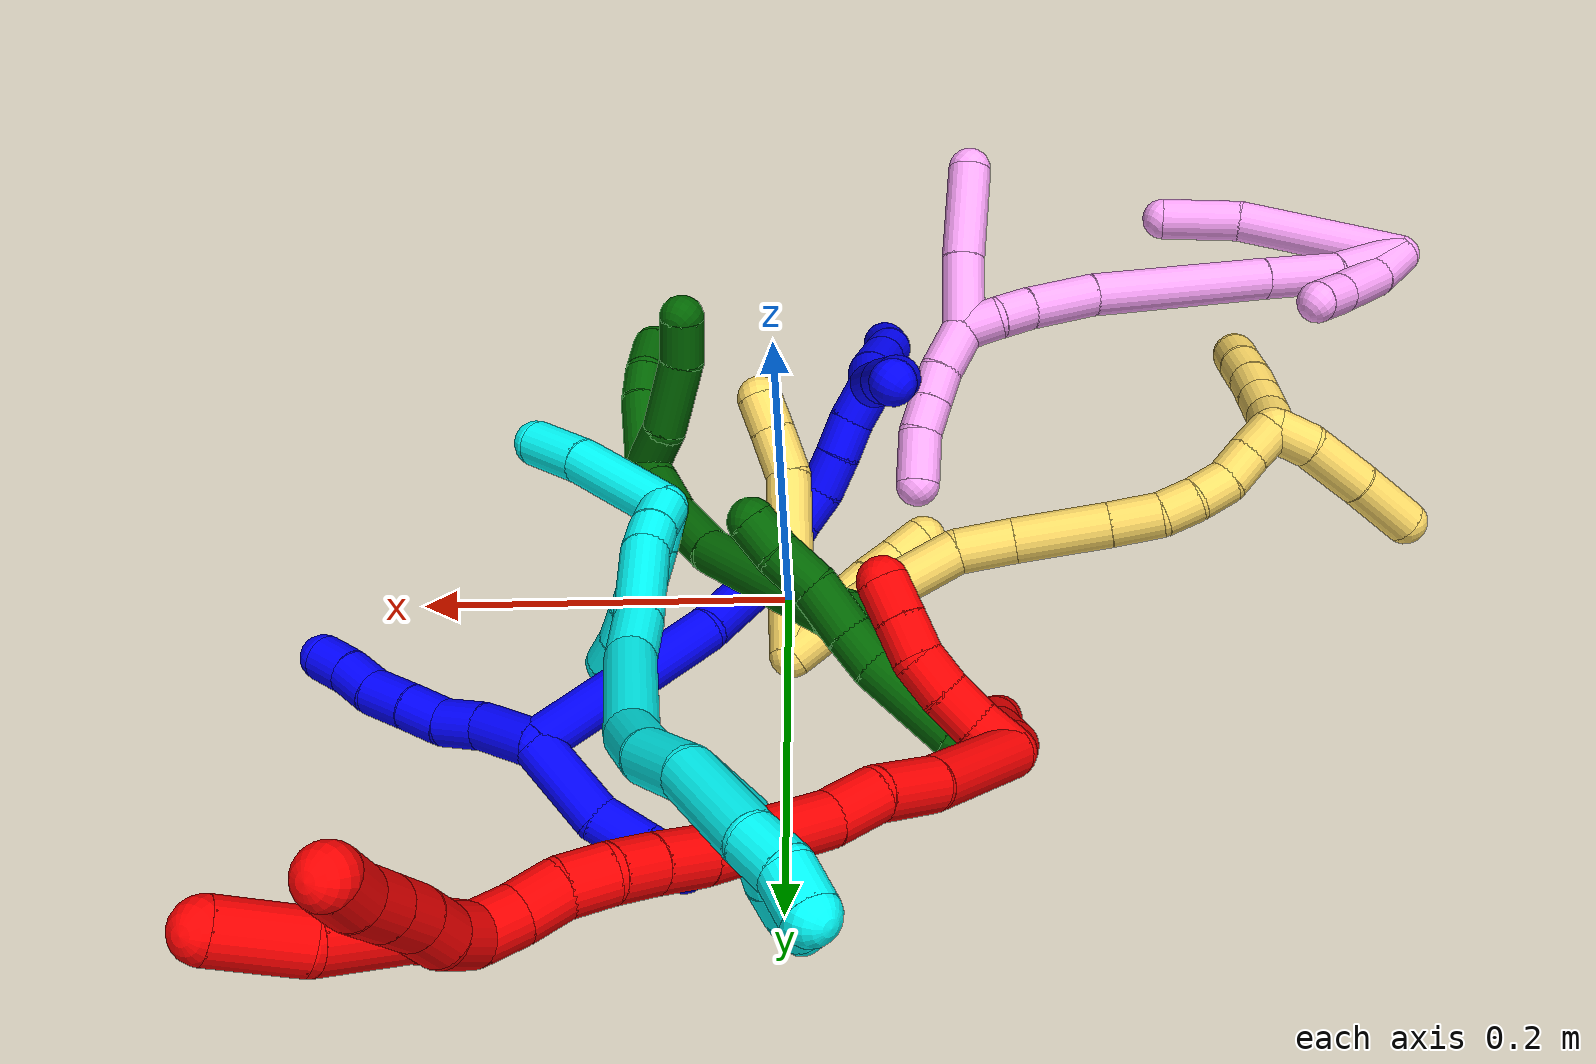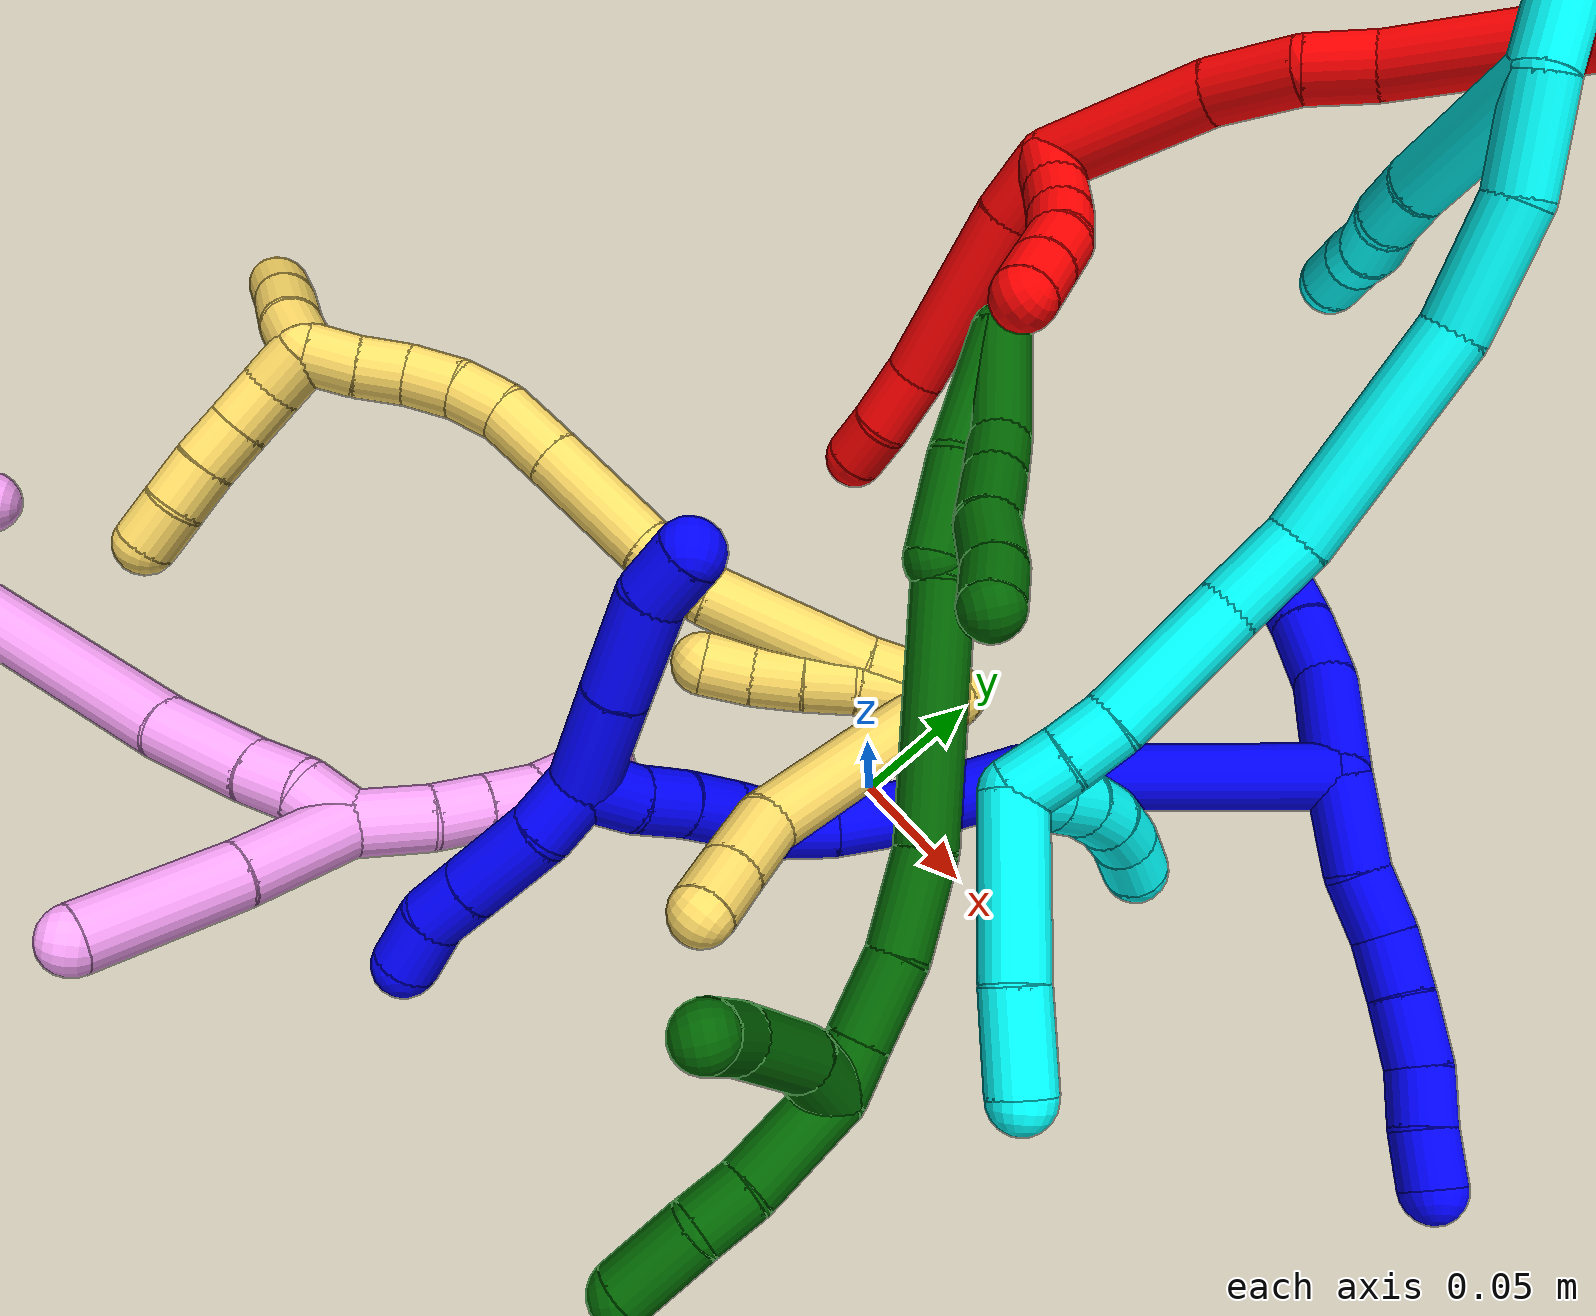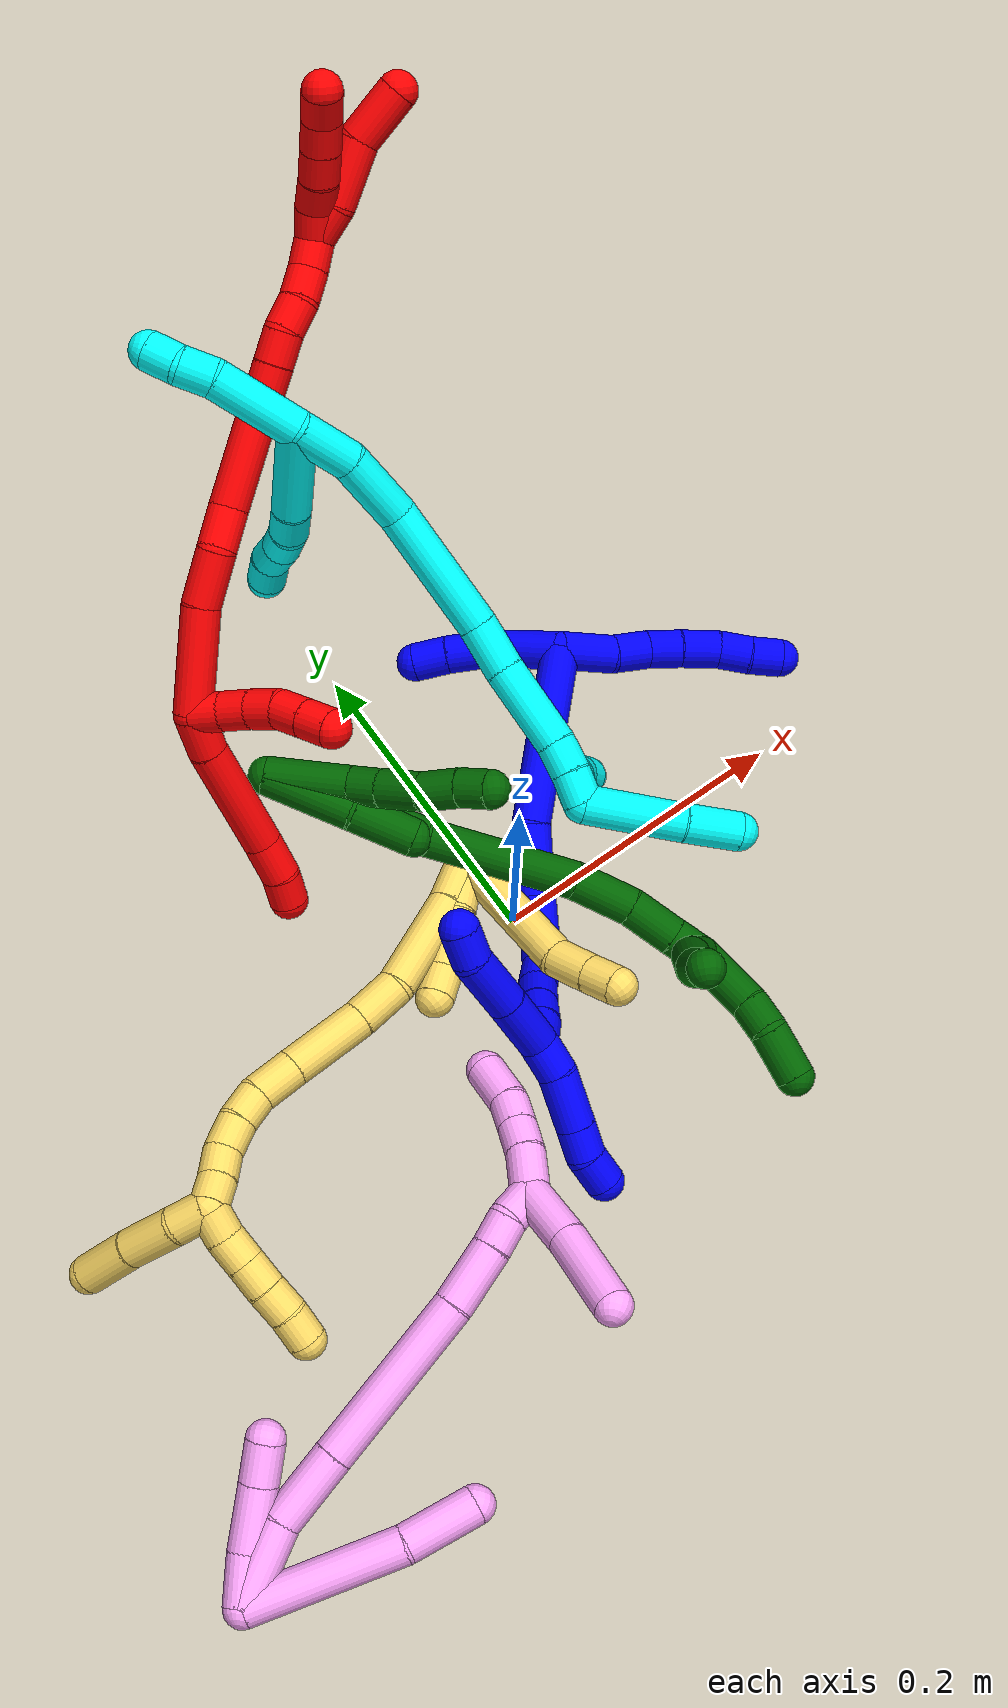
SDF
<sdf version="1.7">
 <world name="default">
  <plugin name="TubeGeneratorPlugin" filename="libtube_generator_plugin.so"/>
  <model name="photoneo_s_sensor">
   <static>1</static>
   <pose>0 0 2 1.57079 1.57079 3.14159</pose>
   <link name="link">
    <inertial><mass>0.1</mass></inertial>
    <sensor name="sensor" type="depth">
     <update_rate>30</update_rate>
     <camera>
      <horizontal_fov>1.22</horizontal_fov>
      <image><width>1920</width><height>1200</height><format>B8G8R8</format></image>
      <clip><near>0.1</near><far>4</far></clip>
      <depth_camera><output>points</output></depth_camera>
     </camera>
     <plugin name="camera_plugin" filename="libgazebo_ros_depth_camera.so">
      <baseline>0.2</baseline>
      <alwaysOn>1</alwaysOn>
      <updateRate>0.0</updateRate>
      <cameraName>camera_ir</cameraName>
      <imageTopicName>/camera/color/image_raw</imageTopicName>
      <cameraInfoTopicName>/camera/color/camera_info</cameraInfoTopicName>
      <depthImageTopicName>/camera/depth/image_raw</depthImageTopicName>
      <depthImageCameraInfoTopicName>/camera/depth/camera_info</depthImageCameraInfoTopicName>
      <pointCloudTopicName>/camera/depth/points</pointCloudTopicName>
      <frameName>fr_optical</frameName>
      <pointCloudCutoff>0.1</pointCloudCutoff>
      <pointCloudCutoffMax>2.0</pointCloudCutoffMax>
      <distortionK1>0</distortionK1>
      <distortionK2>0</distortionK2>
      <distortionK3>0</distortionK3>
      <distortionT1>0</distortionT1>
      <distortionT2>0</distortionT2>
      <CxPrime>0</CxPrime>
      <Cx>0</Cx>
      <Cy>0</Cy>
      <focalLength>0</focalLength>
      <hackBaseline>0</hackBaseline>
     </plugin>
    </sensor>
   </link>
  </model>
  <gravity>0 0 -9.8</gravity>
  <magnetic_field>6e-06 2.3e-05 -4.2e-05</magnetic_field>
  <atmosphere type="adiabatic"/>
  <physics name="default_physics" default="0" type="ode">
   <max_step_size>0.003</max_step_size>
   <real_time_factor>1</real_time_factor>
   <real_time_update_rate>1000</real_time_update_rate>
   <max_contacts>10000</max_contacts>
   <ode>
    <solver>
     <type>quick</type>
     <iters>100</iters>
     <sor>1.3</sor>
     <use_dynamic_moi_rescaling>0</use_dynamic_moi_rescaling>
    </solver>
    <constraints>
     <contact_max_correcting_vel>0</contact_max_correcting_vel>
     <contact_surface_layer>0.001</contact_surface_layer>
     <cfm>0</cfm>
     <erp>0.2</erp>
    </constraints>
   </ode>
  </physics>
  <scene><ambient>0.4 0.4 0.4 1</ambient><background>0.7 0.7 0.7 1</background><shadows>0</shadows></scene>
  <audio><device>default</device></audio>
  <spherical_coordinates>
   <surface_model>EARTH_WGS84</surface_model>
   <latitude_deg>0</latitude_deg>
   <longitude_deg>0</longitude_deg>
   <elevation>0</elevation>
   <heading_deg>0</heading_deg>
  </spherical_coordinates>
  <model name="bin">
   <static>1</static>
   <link name="bottom">
    <collision name="collision-bottom">
     <pose>0 0 -0.01 0 -0 0</pose>
     <geometry><box><size>0.8 0.6 0.02</size></box></geometry>
     <surface>
      <friction><ode><mu>100</mu><mu2>100</mu2></ode></friction>
      <contact><collide_bitmask>65535</collide_bitmask></contact>
     </surface>
    </collision>
   </link>
   <link name="west_wall">
    <collision name="collision-west_wall">
     <pose>-0.41 0 0.1 0 -0 0</pose>
     <geometry><box><size>0.02 0.6 0.2</size></box></geometry>
     <surface>
      <friction><ode><mu>100</mu><mu2>100</mu2></ode></friction>
      <contact><collide_bitmask>65535</collide_bitmask></contact>
     </surface>
    </collision>
   </link>
   <link name="east_wall">
    <collision name="collision-east_wall">
     <pose>0.41 0 0.1 0 -0 0</pose>
     <geometry><box><size>0.02 0.6 0.2</size></box></geometry>
     <surface>
      <friction><ode><mu>100</mu><mu2>100</mu2></ode></friction>
      <contact><collide_bitmask>65535</collide_bitmask></contact>
     </surface>
    </collision>
   </link>
   <link name="south_wall">
    <collision name="collision-south_wall">
     <pose>0 -0.31 0.1 0 -0 0</pose>
     <geometry><box><size>0.8 0.02 0.2</size></box></geometry>
     <surface>
      <friction><ode><mu>100</mu><mu2>100</mu2></ode></friction>
      <contact><collide_bitmask>65535</collide_bitmask></contact>
     </surface>
    </collision>
   </link>
   <link name="north_wall">
    <collision name="collision-north_wall">
     <pose>0 0.31 0.1 0 -0 0</pose>
     <geometry><box><size>0.8 0.02 0.2</size></box></geometry>
     <surface>
      <friction><ode><mu>100</mu><mu2>100</mu2></ode></friction>
      <contact><collide_bitmask>65535</collide_bitmask></contact>
     </surface>
    </collision>
   </link>
  </model>
  <model name="1">
   <static>0</static>
   <link name="1">
    <collision name="collision-cylinder-e_1_2_8">
     <pose>0.006346 -0.000669 0.016731 0.039956 0.362286 0.007319</pose>
     <geometry><cylinder><radius>0.0125</radius><length>0.035814</length></cylinder></geometry>
     <surface>
      <friction><ode><mu>1.16</mu><mu2>1.16</mu2><slip1>0</slip1><slip2>0</slip2></ode></friction>
      <contact><ode><kp>1e+06</kp><kd>1</kd><max_vel>0</max_vel><min_depth>0.001</min_depth></ode></contact>
     </surface>
    </collision>
    <visual name="visual-cylinder-e_1_2_8">
     <pose>0.006346 -0.000669 0.016731 0.039956 0.362286 0.007319</pose>
     <geometry><cylinder><radius>0.0125</radius><length>0.035814</length></cylinder></geometry>
     <material><ambient>0 0 1 1</ambient></material>
    </visual>
    <collision name="collision-cylinder-e_2_8_9">
     <pose>0.018428 0.000308 0.044146 -0.152867 0.487787 -0.03811</pose>
     <geometry><cylinder><radius>0.0125</radius><length>0.024473</length></cylinder></geometry>
     <surface>
      <friction><ode><mu>1.16</mu><mu2>1.16</mu2><slip1>0</slip1><slip2>0</slip2></ode></friction>
      <contact><ode><kp>1e+06</kp><kd>1</kd><max_vel>0</max_vel><min_depth>0.001</min_depth></ode></contact>
     </surface>
    </collision>
    <visual name="visual-cylinder-e_2_8_9">
     <pose>0.018428 0.000308 0.044146 -0.152867 0.487787 -0.03811</pose>
     <geometry><cylinder><radius>0.0125</radius><length>0.024473</length></cylinder></geometry>
     <material><ambient>0 0 1 1</ambient></material>
    </visual>
    <collision name="collision-cylinder-e_3_9_10">
     <pose>0.026572 0.002994 0.065812 -0.094394 0.215057 -0.010197</pose>
     <geometry><cylinder><radius>0.0125</radius><length>0.022585</length></cylinder></geometry>
     <surface>
      <friction><ode><mu>1.16</mu><mu2>1.16</mu2><slip1>0</slip1><slip2>0</slip2></ode></friction>
      <contact><ode><kp>1e+06</kp><kd>1</kd><max_vel>0</max_vel><min_depth>0.001</min_depth></ode></contact>
     </surface>
    </collision>
    <visual name="visual-cylinder-e_3_9_10">
     <pose>0.026572 0.002994 0.065812 -0.094394 0.215057 -0.010197</pose>
     <geometry><cylinder><radius>0.0125</radius><length>0.022585</length></cylinder></geometry>
     <material><ambient>0 0 1 1</ambient></material>
    </visual>
    <collision name="collision-cylinder-e_4_10_11">
     <pose>0.032382 0.004478 0.08911 -0.036051 0.269207 -0.004883</pose>
     <geometry><cylinder><radius>0.0125</radius><length>0.025567</length></cylinder></geometry>
     <surface>
      <friction><ode><mu>1.16</mu><mu2>1.16</mu2><slip1>0</slip1><slip2>0</slip2></ode></friction>
      <contact><ode><kp>1e+06</kp><kd>1</kd><max_vel>0</max_vel><min_depth>0.001</min_depth></ode></contact>
     </surface>
    </collision>
    <visual name="visual-cylinder-e_4_10_11">
     <pose>0.032382 0.004478 0.08911 -0.036051 0.269207 -0.004883</pose>
     <geometry><cylinder><radius>0.0125</radius><length>0.025567</length></cylinder></geometry>
     <material><ambient>0 0 1 1</ambient></material>
    </visual>
    <collision name="collision-cylinder-e_5_11_12">
     <pose>0.036731 0.003902 0.111911 0.097014 0.089825 0.004363</pose>
     <geometry><cylinder><radius>0.0125</radius><length>0.021157</length></cylinder></geometry>
     <surface>
      <friction><ode><mu>1.16</mu><mu2>1.16</mu2><slip1>0</slip1><slip2>0</slip2></ode></friction>
      <contact><ode><kp>1e+06</kp><kd>1</kd><max_vel>0</max_vel><min_depth>0.001</min_depth></ode></contact>
     </surface>
    </collision>
    <visual name="visual-cylinder-e_5_11_12">
     <pose>0.036731 0.003902 0.111911 0.097014 0.089825 0.004363</pose>
     <geometry><cylinder><radius>0.0125</radius><length>0.021157</length></cylinder></geometry>
     <material><ambient>0 0 1 1</ambient></material>
    </visual>
    <collision name="collision-cylinder-e_6_12_6">
     <pose>0.039749 0.002607 0.132384 0.027414 0.204215 0.002809</pose>
     <geometry><cylinder><radius>0.0125</radius><length>0.020405</length></cylinder></geometry>
     <surface>
      <friction><ode><mu>1.16</mu><mu2>1.16</mu2><slip1>0</slip1><slip2>0</slip2></ode></friction>
      <contact><ode><kp>1e+06</kp><kd>1</kd><max_vel>0</max_vel><min_depth>0.001</min_depth></ode></contact>
     </surface>
    </collision>
    <visual name="visual-cylinder-e_6_12_6">
     <pose>0.039749 0.002607 0.132384 0.027414 0.204215 0.002809</pose>
     <geometry><cylinder><radius>0.0125</radius><length>0.020405</length></cylinder></geometry>
     <material><ambient>0 0 1 1</ambient></material>
    </visual>
    <collision name="collision-cylinder-e_1_2_13">
     <pose>0.007604 -0.00314 -0.023133 3.00669 0.31488 2.33695</pose>
     <geometry><cylinder><radius>0.0125</radius><length>0.049105</length></cylinder></geometry>
     <surface>
      <friction><ode><mu>1.16</mu><mu2>1.16</mu2><slip1>0</slip1><slip2>0</slip2></ode></friction>
      <contact><ode><kp>1e+06</kp><kd>1</kd><max_vel>0</max_vel><min_depth>0.001</min_depth></ode></contact>
     </surface>
    </collision>
    <visual name="visual-cylinder-e_1_2_13">
     <pose>0.007604 -0.00314 -0.023133 3.00669 0.31488 2.33695</pose>
     <geometry><cylinder><radius>0.0125</radius><length>0.049105</length></cylinder></geometry>
     <material><ambient>0 0 1 1</ambient></material>
    </visual>
    <collision name="collision-cylinder-e_2_13_14">
     <pose>0.015385 -0.009791 -0.060077 2.8926 0.012424 0.099201</pose>
     <geometry><cylinder><radius>0.0125</radius><length>0.028501</length></cylinder></geometry>
     <surface>
      <friction><ode><mu>1.16</mu><mu2>1.16</mu2><slip1>0</slip1><slip2>0</slip2></ode></friction>
      <contact><ode><kp>1e+06</kp><kd>1</kd><max_vel>0</max_vel><min_depth>0.001</min_depth></ode></contact>
     </surface>
    </collision>
    <visual name="visual-cylinder-e_2_13_14">
     <pose>0.015385 -0.009791 -0.060077 2.8926 0.012424 0.099201</pose>
     <geometry><cylinder><radius>0.0125</radius><length>0.028501</length></cylinder></geometry>
     <material><ambient>0 0 1 1</ambient></material>
    </visual>
    <collision name="collision-cylinder-e_3_14_5">
     <pose>0.015821 -0.01702 -0.084445 2.80308 0.023171 0.135388</pose>
     <geometry><cylinder><radius>0.0125</radius><length>0.022394</length></cylinder></geometry>
     <surface>
      <friction><ode><mu>1.16</mu><mu2>1.16</mu2><slip1>0</slip1><slip2>0</slip2></ode></friction>
      <contact><ode><kp>1e+06</kp><kd>1</kd><max_vel>0</max_vel><min_depth>0.001</min_depth></ode></contact>
     </surface>
    </collision>
    <visual name="visual-cylinder-e_3_14_5">
     <pose>0.015821 -0.01702 -0.084445 2.80308 0.023171 0.135388</pose>
     <geometry><cylinder><radius>0.0125</radius><length>0.022394</length></cylinder></geometry>
     <material><ambient>0 0 1 1</ambient></material>
    </visual>
    <collision name="collision-cylinder-e_1_2_15">
     <pose>-0.02603 -0.052419 -0.002749 1.62319 -0.460362 -0.484201</pose>
     <geometry><cylinder><radius>0.0125</radius><length>0.117181</length></cylinder></geometry>
     <surface>
      <friction><ode><mu>1.16</mu><mu2>1.16</mu2><slip1>0</slip1><slip2>0</slip2></ode></friction>
      <contact><ode><kp>1e+06</kp><kd>1</kd><max_vel>0</max_vel><min_depth>0.001</min_depth></ode></contact>
     </surface>
    </collision>
    <visual name="visual-cylinder-e_1_2_15">
     <pose>-0.02603 -0.052419 -0.002749 1.62319 -0.460362 -0.484201</pose>
     <geometry><cylinder><radius>0.0125</radius><length>0.117181</length></cylinder></geometry>
     <material><ambient>0 0 1 1</ambient></material>
    </visual>
    <collision name="collision-cylinder-e_2_15_16">
     <pose>-0.058532 -0.127364 -0.001132 1.37937 -0.274894 -0.227191</pose>
     <geometry><cylinder><radius>0.0125</radius><length>0.047682</length></cylinder></geometry>
     <surface>
      <friction><ode><mu>1.16</mu><mu2>1.16</mu2><slip1>0</slip1><slip2>0</slip2></ode></friction>
      <contact><ode><kp>1e+06</kp><kd>1</kd><max_vel>0</max_vel><min_depth>0.001</min_depth></ode></contact>
     </surface>
    </collision>
    <visual name="visual-cylinder-e_2_15_16">
     <pose>-0.058532 -0.127364 -0.001132 1.37937 -0.274894 -0.227191</pose>
     <geometry><cylinder><radius>0.0125</radius><length>0.047682</length></cylinder></geometry>
     <material><ambient>0 0 1 1</ambient></material>
    </visual>
    <collision name="collision-cylinder-e_3_16_17">
     <pose>-0.072789 -0.160958 0.005941 1.33086 -0.599469 -0.475915</pose>
     <geometry><cylinder><radius>0.0125</radius><length>0.0276</length></cylinder></geometry>
     <surface>
      <friction><ode><mu>1.16</mu><mu2>1.16</mu2><slip1>0</slip1><slip2>0</slip2></ode></friction>
      <contact><ode><kp>1e+06</kp><kd>1</kd><max_vel>0</max_vel><min_depth>0.001</min_depth></ode></contact>
     </surface>
    </collision>
    <visual name="visual-cylinder-e_3_16_17">
     <pose>-0.072789 -0.160958 0.005941 1.33086 -0.599469 -0.475915</pose>
     <geometry><cylinder><radius>0.0125</radius><length>0.0276</length></cylinder></geometry>
     <material><ambient>0 0 1 1</ambient></material>
    </visual>
    <collision name="collision-cylinder-e_4_17_18">
     <pose>-0.089246 -0.178279 0.01034 1.30678 -0.929168 -0.732717</pose>
     <geometry><cylinder><radius>0.0125</radius><length>0.021647</length></cylinder></geometry>
     <surface>
      <friction><ode><mu>1.16</mu><mu2>1.16</mu2><slip1>0</slip1><slip2>0</slip2></ode></friction>
      <contact><ode><kp>1e+06</kp><kd>1</kd><max_vel>0</max_vel><min_depth>0.001</min_depth></ode></contact>
     </surface>
    </collision>
    <visual name="visual-cylinder-e_4_17_18">
     <pose>-0.089246 -0.178279 0.01034 1.30678 -0.929168 -0.732717</pose>
     <geometry><cylinder><radius>0.0125</radius><length>0.021647</length></cylinder></geometry>
     <material><ambient>0 0 1 1</ambient></material>
    </visual>
    <collision name="collision-cylinder-e_5_18_19">
     <pose>-0.107455 -0.188672 0.011764 1.63487 -1.1606 -1.22012</pose>
     <geometry><cylinder><radius>0.0125</radius><length>0.020802</length></cylinder></geometry>
     <surface>
      <friction><ode><mu>1.16</mu><mu2>1.16</mu2><slip1>0</slip1><slip2>0</slip2></ode></friction>
      <contact><ode><kp>1e+06</kp><kd>1</kd><max_vel>0</max_vel><min_depth>0.001</min_depth></ode></contact>
     </surface>
    </collision>
    <visual name="visual-cylinder-e_5_18_19">
     <pose>-0.107455 -0.188672 0.011764 1.63487 -1.1606 -1.22012</pose>
     <geometry><cylinder><radius>0.0125</radius><length>0.020802</length></cylinder></geometry>
     <material><ambient>0 0 1 1</ambient></material>
    </visual>
    <collision name="collision-cylinder-e_6_19_20">
     <pose>-0.127767 -0.195191 0.012655 1.11845 -1.32996 -0.912452</pose>
     <geometry><cylinder><radius>0.0125</radius><length>0.02219</length></cylinder></geometry>
     <surface>
      <friction><ode><mu>1.16</mu><mu2>1.16</mu2><slip1>0</slip1><slip2>0</slip2></ode></friction>
      <contact><ode><kp>1e+06</kp><kd>1</kd><max_vel>0</max_vel><min_depth>0.001</min_depth></ode></contact>
     </surface>
    </collision>
    <visual name="visual-cylinder-e_6_19_20">
     <pose>-0.127767 -0.195191 0.012655 1.11845 -1.32996 -0.912452</pose>
     <geometry><cylinder><radius>0.0125</radius><length>0.02219</length></cylinder></geometry>
     <material><ambient>0 0 1 1</ambient></material>
    </visual>
    <collision name="collision-cylinder-e_7_20_21">
     <pose>-0.148463 -0.200295 0.01563 0.982206 -1.25195 -0.737882</pose>
     <geometry><cylinder><radius>0.0125</radius><length>0.020895</length></cylinder></geometry>
     <surface>
      <friction><ode><mu>1.16</mu><mu2>1.16</mu2><slip1>0</slip1><slip2>0</slip2></ode></friction>
      <contact><ode><kp>1e+06</kp><kd>1</kd><max_vel>0</max_vel><min_depth>0.001</min_depth></ode></contact>
     </surface>
    </collision>
    <visual name="visual-cylinder-e_7_20_21">
     <pose>-0.148463 -0.200295 0.01563 0.982206 -1.25195 -0.737882</pose>
     <geometry><cylinder><radius>0.0125</radius><length>0.020895</length></cylinder></geometry>
     <material><ambient>0 0 1 1</ambient></material>
    </visual>
    <collision name="collision-cylinder-e_8_21_1">
     <pose>-0.169065 -0.205647 0.017649 1.49475 -1.32885 -1.25568</pose>
     <geometry><cylinder><radius>0.0125</radius><length>0.022004</length></cylinder></geometry>
     <surface>
      <friction><ode><mu>1.16</mu><mu2>1.16</mu2><slip1>0</slip1><slip2>0</slip2></ode></friction>
      <contact><ode><kp>1e+06</kp><kd>1</kd><max_vel>0</max_vel><min_depth>0.001</min_depth></ode></contact>
     </surface>
    </collision>
    <visual name="visual-cylinder-e_8_21_1">
     <pose>-0.169065 -0.205647 0.017649 1.49475 -1.32885 -1.25568</pose>
     <geometry><cylinder><radius>0.0125</radius><length>0.022004</length></cylinder></geometry>
     <material><ambient>0 0 1 1</ambient></material>
    </visual>
    <collision name="collision-cylinder-e_1_1_22">
     <pose>-0.188411 -0.19392 0.007449 -2.19774 -0.454618 0.851016</pose>
     <geometry><cylinder><radius>0.0125</radius><length>0.039463</length></cylinder></geometry>
     <surface>
      <friction><ode><mu>1.16</mu><mu2>1.16</mu2><slip1>0</slip1><slip2>0</slip2></ode></friction>
      <contact><ode><kp>1e+06</kp><kd>1</kd><max_vel>0</max_vel><min_depth>0.001</min_depth></ode></contact>
     </surface>
    </collision>
    <visual name="visual-cylinder-e_1_1_22">
     <pose>-0.188411 -0.19392 0.007449 -2.19774 -0.454618 0.851016</pose>
     <geometry><cylinder><radius>0.0125</radius><length>0.039463</length></cylinder></geometry>
     <material><ambient>0 0 1 1</ambient></material>
    </visual>
    <collision name="collision-cylinder-e_2_22_23">
     <pose>-0.205221 -0.165454 -0.013724 -2.22285 -0.430167 0.831753</pose>
     <geometry><cylinder><radius>0.0125</radius><length>0.039063</length></cylinder></geometry>
     <surface>
      <friction><ode><mu>1.16</mu><mu2>1.16</mu2><slip1>0</slip1><slip2>0</slip2></ode></friction>
      <contact><ode><kp>1e+06</kp><kd>1</kd><max_vel>0</max_vel><min_depth>0.001</min_depth></ode></contact>
     </surface>
    </collision>
    <visual name="visual-cylinder-e_2_22_23">
     <pose>-0.205221 -0.165454 -0.013724 -2.22285 -0.430167 0.831753</pose>
     <geometry><cylinder><radius>0.0125</radius><length>0.039063</length></cylinder></geometry>
     <material><ambient>0 0 1 1</ambient></material>
    </visual>
    <collision name="collision-cylinder-e_3_23_4">
     <pose>-0.215481 -0.141726 -0.028775 -1.98942 -0.198282 0.303884</pose>
     <geometry><cylinder><radius>0.0125</radius><length>0.021474</length></cylinder></geometry>
     <surface>
      <friction><ode><mu>1.16</mu><mu2>1.16</mu2><slip1>0</slip1><slip2>0</slip2></ode></friction>
      <contact><ode><kp>1e+06</kp><kd>1</kd><max_vel>0</max_vel><min_depth>0.001</min_depth></ode></contact>
     </surface>
    </collision>
    <visual name="visual-cylinder-e_3_23_4">
     <pose>-0.215481 -0.141726 -0.028775 -1.98942 -0.198282 0.303884</pose>
     <geometry><cylinder><radius>0.0125</radius><length>0.021474</length></cylinder></geometry>
     <material><ambient>0 0 1 1</ambient></material>
    </visual>
    <collision name="collision-cylinder-e_1_1_24">
     <pose>-0.17941 -0.217434 0.024534 0.940246 0.029734 0.015109</pose>
     <geometry><cylinder><radius>0.0125</radius><length>0.022686</length></cylinder></geometry>
     <surface>
      <friction><ode><mu>1.16</mu><mu2>1.16</mu2><slip1>0</slip1><slip2>0</slip2></ode></friction>
      <contact><ode><kp>1e+06</kp><kd>1</kd><max_vel>0</max_vel><min_depth>0.001</min_depth></ode></contact>
     </surface>
    </collision>
    <visual name="visual-cylinder-e_1_1_24">
     <pose>-0.17941 -0.217434 0.024534 0.940246 0.029734 0.015109</pose>
     <geometry><cylinder><radius>0.0125</radius><length>0.022686</length></cylinder></geometry>
     <material><ambient>0 0 1 1</ambient></material>
    </visual>
    <collision name="collision-cylinder-e_2_24_25">
     <pose>-0.178924 -0.24274 0.03837 1.15389 0.008397 0.005465</pose>
     <geometry><cylinder><radius>0.0125</radius><length>0.035323</length></cylinder></geometry>
     <surface>
      <friction><ode><mu>1.16</mu><mu2>1.16</mu2><slip1>0</slip1><slip2>0</slip2></ode></friction>
      <contact><ode><kp>1e+06</kp><kd>1</kd><max_vel>0</max_vel><min_depth>0.001</min_depth></ode></contact>
     </surface>
    </collision>
    <visual name="visual-cylinder-e_2_24_25">
     <pose>-0.178924 -0.24274 0.03837 1.15389 0.008397 0.005465</pose>
     <geometry><cylinder><radius>0.0125</radius><length>0.035323</length></cylinder></geometry>
     <material><ambient>0 0 1 1</ambient></material>
    </visual>
    <collision name="collision-cylinder-e_3_25_26">
     <pose>-0.178675 -0.268261 0.049573 1.16284 0.009917 0.006518</pose>
     <geometry><cylinder><radius>0.0125</radius><length>0.020422</length></cylinder></geometry>
     <surface>
      <friction><ode><mu>1.16</mu><mu2>1.16</mu2><slip1>0</slip1><slip2>0</slip2></ode></friction>
      <contact><ode><kp>1e+06</kp><kd>1</kd><max_vel>0</max_vel><min_depth>0.001</min_depth></ode></contact>
     </surface>
    </collision>
    <visual name="visual-cylinder-e_3_25_26">
     <pose>-0.178675 -0.268261 0.049573 1.16284 0.009917 0.006518</pose>
     <geometry><cylinder><radius>0.0125</radius><length>0.020422</length></cylinder></geometry>
     <material><ambient>0 0 1 1</ambient></material>
    </visual>
    <collision name="collision-cylinder-e_4_26_3">
     <pose>-0.176183 -0.285998 0.059997 0.919626 0.223503 0.111031</pose>
     <geometry><cylinder><radius>0.0125</radius><length>0.021568</length></cylinder></geometry>
     <surface>
      <friction><ode><mu>1.16</mu><mu2>1.16</mu2><slip1>0</slip1><slip2>0</slip2></ode></friction>
      <contact><ode><kp>1e+06</kp><kd>1</kd><max_vel>0</max_vel><min_depth>0.001</min_depth></ode></contact>
     </surface>
    </collision>
    <visual name="visual-cylinder-e_4_26_3">
     <pose>-0.176183 -0.285998 0.059997 0.919626 0.223503 0.111031</pose>
     <geometry><cylinder><radius>0.0125</radius><length>0.021568</length></cylinder></geometry>
     <material><ambient>0 0 1 1</ambient></material>
    </visual>
    <collision name="collision-sphere-3">
     <pose>-0.173793 -0.294362 0.066371 0 -0 0</pose>
     <geometry><sphere><radius>0.0125</radius></sphere></geometry>
     <surface>
      <friction><ode><mu>1.16</mu><mu2>1.16</mu2><slip1>0</slip1><slip2>0</slip2></ode></friction>
      <contact><ode><kp>1e+06</kp><kd>1</kd><max_vel>0</max_vel><min_depth>0.001</min_depth></ode></contact>
     </surface>
    </collision>
    <visual name="visual-sphere-3">
     <pose>-0.173793 -0.294362 0.066371 0 -0 0</pose>
     <geometry><sphere><radius>0.0125</radius></sphere></geometry>
     <material><ambient>0 0 1 1</ambient></material>
    </visual>
    <collision name="collision-sphere-26">
     <pose>-0.178573 -0.277633 0.053623 0 -0 0</pose>
     <geometry><sphere><radius>0.0125</radius></sphere></geometry>
     <surface>
      <friction><ode><mu>1.16</mu><mu2>1.16</mu2><slip1>0</slip1><slip2>0</slip2></ode></friction>
      <contact><ode><kp>1e+06</kp><kd>1</kd><max_vel>0</max_vel><min_depth>0.001</min_depth></ode></contact>
     </surface>
    </collision>
    <visual name="visual-sphere-26">
     <pose>-0.178573 -0.277633 0.053623 0 -0 0</pose>
     <geometry><sphere><radius>0.0125</radius></sphere></geometry>
     <material><ambient>0 0 1 1</ambient></material>
    </visual>
    <collision name="collision-sphere-25">
     <pose>-0.178776 -0.258888 0.045522 0 -0 0</pose>
     <geometry><sphere><radius>0.0125</radius></sphere></geometry>
     <surface>
      <friction><ode><mu>1.16</mu><mu2>1.16</mu2><slip1>0</slip1><slip2>0</slip2></ode></friction>
      <contact><ode><kp>1e+06</kp><kd>1</kd><max_vel>0</max_vel><min_depth>0.001</min_depth></ode></contact>
     </surface>
    </collision>
    <visual name="visual-sphere-25">
     <pose>-0.178776 -0.258888 0.045522 0 -0 0</pose>
     <geometry><sphere><radius>0.0125</radius></sphere></geometry>
     <material><ambient>0 0 1 1</ambient></material>
    </visual>
    <collision name="collision-sphere-24">
     <pose>-0.179073 -0.226591 0.031219 0 -0 0</pose>
     <geometry><sphere><radius>0.0125</radius></sphere></geometry>
     <surface>
      <friction><ode><mu>1.16</mu><mu2>1.16</mu2><slip1>0</slip1><slip2>0</slip2></ode></friction>
      <contact><ode><kp>1e+06</kp><kd>1</kd><max_vel>0</max_vel><min_depth>0.001</min_depth></ode></contact>
     </surface>
    </collision>
    <visual name="visual-sphere-24">
     <pose>-0.179073 -0.226591 0.031219 0 -0 0</pose>
     <geometry><sphere><radius>0.0125</radius></sphere></geometry>
     <material><ambient>0 0 1 1</ambient></material>
    </visual>
    <collision name="collision-sphere-4">
     <pose>-0.217596 -0.132108 -0.033054 0 -0 0</pose>
     <geometry><sphere><radius>0.0125</radius></sphere></geometry>
     <surface>
      <friction><ode><mu>1.16</mu><mu2>1.16</mu2><slip1>0</slip1><slip2>0</slip2></ode></friction>
      <contact><ode><kp>1e+06</kp><kd>1</kd><max_vel>0</max_vel><min_depth>0.001</min_depth></ode></contact>
     </surface>
    </collision>
    <visual name="visual-sphere-4">
     <pose>-0.217596 -0.132108 -0.033054 0 -0 0</pose>
     <geometry><sphere><radius>0.0125</radius></sphere></geometry>
     <material><ambient>0 0 1 1</ambient></material>
    </visual>
    <collision name="collision-sphere-23">
     <pose>-0.213366 -0.151343 -0.024496 0 -0 0</pose>
     <geometry><sphere><radius>0.0125</radius></sphere></geometry>
     <surface>
      <friction><ode><mu>1.16</mu><mu2>1.16</mu2><slip1>0</slip1><slip2>0</slip2></ode></friction>
      <contact><ode><kp>1e+06</kp><kd>1</kd><max_vel>0</max_vel><min_depth>0.001</min_depth></ode></contact>
     </surface>
    </collision>
    <visual name="visual-sphere-23">
     <pose>-0.213366 -0.151343 -0.024496 0 -0 0</pose>
     <geometry><sphere><radius>0.0125</radius></sphere></geometry>
     <material><ambient>0 0 1 1</ambient></material>
    </visual>
    <collision name="collision-sphere-22">
     <pose>-0.197076 -0.179564 -0.002951 0 -0 0</pose>
     <geometry><sphere><radius>0.0125</radius></sphere></geometry>
     <surface>
      <friction><ode><mu>1.16</mu><mu2>1.16</mu2><slip1>0</slip1><slip2>0</slip2></ode></friction>
      <contact><ode><kp>1e+06</kp><kd>1</kd><max_vel>0</max_vel><min_depth>0.001</min_depth></ode></contact>
     </surface>
    </collision>
    <visual name="visual-sphere-22">
     <pose>-0.197076 -0.179564 -0.002951 0 -0 0</pose>
     <geometry><sphere><radius>0.0125</radius></sphere></geometry>
     <material><ambient>0 0 1 1</ambient></material>
    </visual>
    <collision name="collision-sphere-1">
     <pose>-0.179747 -0.208276 0.017849 0 -0 0</pose>
     <geometry><sphere><radius>0.0125</radius></sphere></geometry>
     <surface>
      <friction><ode><mu>1.16</mu><mu2>1.16</mu2><slip1>0</slip1><slip2>0</slip2></ode></friction>
      <contact><ode><kp>1e+06</kp><kd>1</kd><max_vel>0</max_vel><min_depth>0.001</min_depth></ode></contact>
     </surface>
    </collision>
    <visual name="visual-sphere-1">
     <pose>-0.179747 -0.208276 0.017849 0 -0 0</pose>
     <geometry><sphere><radius>0.0125</radius></sphere></geometry>
     <material><ambient>0 0 1 1</ambient></material>
    </visual>
    <collision name="collision-sphere-21">
     <pose>-0.158384 -0.203019 0.017449 0 -0 0</pose>
     <geometry><sphere><radius>0.0125</radius></sphere></geometry>
     <surface>
      <friction><ode><mu>1.16</mu><mu2>1.16</mu2><slip1>0</slip1><slip2>0</slip2></ode></friction>
      <contact><ode><kp>1e+06</kp><kd>1</kd><max_vel>0</max_vel><min_depth>0.001</min_depth></ode></contact>
     </surface>
    </collision>
    <visual name="visual-sphere-21">
     <pose>-0.158384 -0.203019 0.017449 0 -0 0</pose>
     <geometry><sphere><radius>0.0125</radius></sphere></geometry>
     <material><ambient>0 0 1 1</ambient></material>
    </visual>
    <collision name="collision-sphere-12">
     <pose>0.03768 0.002881 0.122397 0 -0 0</pose>
     <geometry><sphere><radius>0.0125</radius></sphere></geometry>
     <surface>
      <friction><ode><mu>1.16</mu><mu2>1.16</mu2><slip1>0</slip1><slip2>0</slip2></ode></friction>
      <contact><ode><kp>1e+06</kp><kd>1</kd><max_vel>0</max_vel><min_depth>0.001</min_depth></ode></contact>
     </surface>
    </collision>
    <visual name="visual-sphere-12">
     <pose>0.03768 0.002881 0.122397 0 -0 0</pose>
     <geometry><sphere><radius>0.0125</radius></sphere></geometry>
     <material><ambient>0 0 1 1</ambient></material>
    </visual>
    <collision name="collision-sphere-11">
     <pose>0.035782 0.004922 0.101425 0 -0 0</pose>
     <geometry><sphere><radius>0.0125</radius></sphere></geometry>
     <surface>
      <friction><ode><mu>1.16</mu><mu2>1.16</mu2><slip1>0</slip1><slip2>0</slip2></ode></friction>
      <contact><ode><kp>1e+06</kp><kd>1</kd><max_vel>0</max_vel><min_depth>0.001</min_depth></ode></contact>
     </surface>
    </collision>
    <visual name="visual-sphere-11">
     <pose>0.035782 0.004922 0.101425 0 -0 0</pose>
     <geometry><sphere><radius>0.0125</radius></sphere></geometry>
     <material><ambient>0 0 1 1</ambient></material>
    </visual>
    <collision name="collision-sphere-10">
     <pose>0.028982 0.004034 0.076795 0 -0 0</pose>
     <geometry><sphere><radius>0.0125</radius></sphere></geometry>
     <surface>
      <friction><ode><mu>1.16</mu><mu2>1.16</mu2><slip1>0</slip1><slip2>0</slip2></ode></friction>
      <contact><ode><kp>1e+06</kp><kd>1</kd><max_vel>0</max_vel><min_depth>0.001</min_depth></ode></contact>
     </surface>
    </collision>
    <visual name="visual-sphere-10">
     <pose>0.028982 0.004034 0.076795 0 -0 0</pose>
     <geometry><sphere><radius>0.0125</radius></sphere></geometry>
     <material><ambient>0 0 1 1</ambient></material>
    </visual>
    <collision name="collision-sphere-9">
     <pose>0.024163 0.001954 0.054829 0 -0 0</pose>
     <geometry><sphere><radius>0.0125</radius></sphere></geometry>
     <surface>
      <friction><ode><mu>1.16</mu><mu2>1.16</mu2><slip1>0</slip1><slip2>0</slip2></ode></friction>
      <contact><ode><kp>1e+06</kp><kd>1</kd><max_vel>0</max_vel><min_depth>0.001</min_depth></ode></contact>
     </surface>
    </collision>
    <visual name="visual-sphere-9">
     <pose>0.024163 0.001954 0.054829 0 -0 0</pose>
     <geometry><sphere><radius>0.0125</radius></sphere></geometry>
     <material><ambient>0 0 1 1</ambient></material>
    </visual>
    <collision name="collision-sphere-2">
     <geometry><sphere><radius>0.0125</radius></sphere></geometry>
     <surface>
      <friction><ode><mu>1.16</mu><mu2>1.16</mu2><slip1>0</slip1><slip2>0</slip2></ode></friction>
      <contact><ode><kp>1e+06</kp><kd>1</kd><max_vel>0</max_vel><min_depth>0.001</min_depth></ode></contact>
     </surface>
    </collision>
    <visual name="visual-sphere-2">
     <geometry><sphere><radius>0.0125</radius></sphere></geometry>
     <material><ambient>0 0 1 1</ambient></material>
    </visual>
    <collision name="collision-sphere-19">
     <pose>-0.116993 -0.192811 0.011499 0 -0 0</pose>
     <geometry><sphere><radius>0.0125</radius></sphere></geometry>
     <surface>
      <friction><ode><mu>1.16</mu><mu2>1.16</mu2><slip1>0</slip1><slip2>0</slip2></ode></friction>
      <contact><ode><kp>1e+06</kp><kd>1</kd><max_vel>0</max_vel><min_depth>0.001</min_depth></ode></contact>
     </surface>
    </collision>
    <visual name="visual-sphere-19">
     <pose>-0.116993 -0.192811 0.011499 0 -0 0</pose>
     <geometry><sphere><radius>0.0125</radius></sphere></geometry>
     <material><ambient>0 0 1 1</ambient></material>
    </visual>
    <collision name="collision-sphere-8">
     <pose>0.012693 -0.001338 0.033463 0 -0 0</pose>
     <geometry><sphere><radius>0.0125</radius></sphere></geometry>
     <surface>
      <friction><ode><mu>1.16</mu><mu2>1.16</mu2><slip1>0</slip1><slip2>0</slip2></ode></friction>
      <contact><ode><kp>1e+06</kp><kd>1</kd><max_vel>0</max_vel><min_depth>0.001</min_depth></ode></contact>
     </surface>
    </collision>
    <visual name="visual-sphere-8">
     <pose>0.012693 -0.001338 0.033463 0 -0 0</pose>
     <geometry><sphere><radius>0.0125</radius></sphere></geometry>
     <material><ambient>0 0 1 1</ambient></material>
    </visual>
    <collision name="collision-sphere-6">
     <pose>0.041818 0.002333 0.142371 0 -0 0</pose>
     <geometry><sphere><radius>0.0125</radius></sphere></geometry>
     <surface>
      <friction><ode><mu>1.16</mu><mu2>1.16</mu2><slip1>0</slip1><slip2>0</slip2></ode></friction>
      <contact><ode><kp>1e+06</kp><kd>1</kd><max_vel>0</max_vel><min_depth>0.001</min_depth></ode></contact>
     </surface>
    </collision>
    <visual name="visual-sphere-6">
     <pose>0.041818 0.002333 0.142371 0 -0 0</pose>
     <geometry><sphere><radius>0.0125</radius></sphere></geometry>
     <material><ambient>0 0 1 1</ambient></material>
    </visual>
    <collision name="collision-sphere-13">
     <pose>0.015208 -0.00628 -0.046267 0 -0 0</pose>
     <geometry><sphere><radius>0.0125</radius></sphere></geometry>
     <surface>
      <friction><ode><mu>1.16</mu><mu2>1.16</mu2><slip1>0</slip1><slip2>0</slip2></ode></friction>
      <contact><ode><kp>1e+06</kp><kd>1</kd><max_vel>0</max_vel><min_depth>0.001</min_depth></ode></contact>
     </surface>
    </collision>
    <visual name="visual-sphere-13">
     <pose>0.015208 -0.00628 -0.046267 0 -0 0</pose>
     <geometry><sphere><radius>0.0125</radius></sphere></geometry>
     <material><ambient>0 0 1 1</ambient></material>
    </visual>
    <collision name="collision-sphere-14">
     <pose>0.015562 -0.013303 -0.073887 0 -0 0</pose>
     <geometry><sphere><radius>0.0125</radius></sphere></geometry>
     <surface>
      <friction><ode><mu>1.16</mu><mu2>1.16</mu2><slip1>0</slip1><slip2>0</slip2></ode></friction>
      <contact><ode><kp>1e+06</kp><kd>1</kd><max_vel>0</max_vel><min_depth>0.001</min_depth></ode></contact>
     </surface>
    </collision>
    <visual name="visual-sphere-14">
     <pose>0.015562 -0.013303 -0.073887 0 -0 0</pose>
     <geometry><sphere><radius>0.0125</radius></sphere></geometry>
     <material><ambient>0 0 1 1</ambient></material>
    </visual>
    <collision name="collision-sphere-5">
     <pose>0.016081 -0.020737 -0.095004 0 -0 0</pose>
     <geometry><sphere><radius>0.0125</radius></sphere></geometry>
     <surface>
      <friction><ode><mu>1.16</mu><mu2>1.16</mu2><slip1>0</slip1><slip2>0</slip2></ode></friction>
      <contact><ode><kp>1e+06</kp><kd>1</kd><max_vel>0</max_vel><min_depth>0.001</min_depth></ode></contact>
     </surface>
    </collision>
    <visual name="visual-sphere-5">
     <pose>0.016081 -0.020737 -0.095004 0 -0 0</pose>
     <geometry><sphere><radius>0.0125</radius></sphere></geometry>
     <material><ambient>0 0 1 1</ambient></material>
    </visual>
    <collision name="collision-sphere-15">
     <pose>-0.05206 -0.104837 -0.005497 0 -0 0</pose>
     <geometry><sphere><radius>0.0125</radius></sphere></geometry>
     <surface>
      <friction><ode><mu>1.16</mu><mu2>1.16</mu2><slip1>0</slip1><slip2>0</slip2></ode></friction>
      <contact><ode><kp>1e+06</kp><kd>1</kd><max_vel>0</max_vel><min_depth>0.001</min_depth></ode></contact>
     </surface>
    </collision>
    <visual name="visual-sphere-15">
     <pose>-0.05206 -0.104837 -0.005497 0 -0 0</pose>
     <geometry><sphere><radius>0.0125</radius></sphere></geometry>
     <material><ambient>0 0 1 1</ambient></material>
    </visual>
    <collision name="collision-sphere-16">
     <pose>-0.065003 -0.149891 0.003234 0 -0 0</pose>
     <geometry><sphere><radius>0.0125</radius></sphere></geometry>
     <surface>
      <friction><ode><mu>1.16</mu><mu2>1.16</mu2><slip1>0</slip1><slip2>0</slip2></ode></friction>
      <contact><ode><kp>1e+06</kp><kd>1</kd><max_vel>0</max_vel><min_depth>0.001</min_depth></ode></contact>
     </surface>
    </collision>
    <visual name="visual-sphere-16">
     <pose>-0.065003 -0.149891 0.003234 0 -0 0</pose>
     <geometry><sphere><radius>0.0125</radius></sphere></geometry>
     <material><ambient>0 0 1 1</ambient></material>
    </visual>
    <collision name="collision-sphere-17">
     <pose>-0.080575 -0.172026 0.008649 0 -0 0</pose>
     <geometry><sphere><radius>0.0125</radius></sphere></geometry>
     <surface>
      <friction><ode><mu>1.16</mu><mu2>1.16</mu2><slip1>0</slip1><slip2>0</slip2></ode></friction>
      <contact><ode><kp>1e+06</kp><kd>1</kd><max_vel>0</max_vel><min_depth>0.001</min_depth></ode></contact>
     </surface>
    </collision>
    <visual name="visual-sphere-17">
     <pose>-0.080575 -0.172026 0.008649 0 -0 0</pose>
     <geometry><sphere><radius>0.0125</radius></sphere></geometry>
     <material><ambient>0 0 1 1</ambient></material>
    </visual>
    <collision name="collision-sphere-18">
     <pose>-0.097917 -0.184532 0.01203 0 -0 0</pose>
     <geometry><sphere><radius>0.0125</radius></sphere></geometry>
     <surface>
      <friction><ode><mu>1.16</mu><mu2>1.16</mu2><slip1>0</slip1><slip2>0</slip2></ode></friction>
      <contact><ode><kp>1e+06</kp><kd>1</kd><max_vel>0</max_vel><min_depth>0.001</min_depth></ode></contact>
     </surface>
    </collision>
    <visual name="visual-sphere-18">
     <pose>-0.097917 -0.184532 0.01203 0 -0 0</pose>
     <geometry><sphere><radius>0.0125</radius></sphere></geometry>
     <material><ambient>0 0 1 1</ambient></material>
    </visual>
    <collision name="collision-sphere-20">
     <pose>-0.138542 -0.197571 0.013812 0 -0 0</pose>
     <geometry><sphere><radius>0.0125</radius></sphere></geometry>
     <surface>
      <friction><ode><mu>1.16</mu><mu2>1.16</mu2><slip1>0</slip1><slip2>0</slip2></ode></friction>
      <contact><ode><kp>1e+06</kp><kd>1</kd><max_vel>0</max_vel><min_depth>0.001</min_depth></ode></contact>
     </surface>
    </collision>
    <visual name="visual-sphere-20">
     <pose>-0.138542 -0.197571 0.013812 0 -0 0</pose>
     <geometry><sphere><radius>0.0125</radius></sphere></geometry>
     <material><ambient>0 0 1 1</ambient></material>
    </visual>
    <inertial>
     <pose>-0.072976 -0.107079 0.013846 0 -0 0</pose>
     <mass>0.75</mass>
     <inertia><ixx>9.7e-05</ixx><ixy>0</ixy><ixz>0</ixz><iyy>-9e-06</iyy><iyz>0</iyz><izz>0.000216</izz></inertia>
    </inertial>
   </link>
   <pose>0.124637 0.121769 0.040529 1.50419 0.981019 0.773408</pose>
  </model>
  <model name="2">
   <static>0</static>
   <link name="2">
    <collision name="collision-cylinder-e_1_2_8">
     <pose>0.003269 0.001937 -0.01307 -2.99444 0.242573 -2.0538</pose>
     <geometry><cylinder><radius>0.0125</radius><length>0.027223</length></cylinder></geometry>
     <surface>
      <friction><ode><mu>1.16</mu><mu2>1.16</mu2><slip1>0</slip1><slip2>0</slip2></ode></friction>
      <contact><ode><kp>1e+06</kp><kd>1</kd><max_vel>0</max_vel><min_depth>0.001</min_depth></ode></contact>
     </surface>
    </collision>
    <visual name="visual-cylinder-e_1_2_8">
     <pose>0.003269 0.001937 -0.01307 -2.99444 0.242573 -2.0538</pose>
     <geometry><cylinder><radius>0.0125</radius><length>0.027223</length></cylinder></geometry>
     <material><ambient>1 0 0 1</ambient></material>
    </visual>
    <collision name="collision-cylinder-e_2_8_9">
     <pose>0.019951 0.011601 -0.060707 -2.92168 0.36197 -2.05586</pose>
     <geometry><cylinder><radius>0.0125</radius><length>0.075748</length></cylinder></geometry>
     <surface>
      <friction><ode><mu>1.16</mu><mu2>1.16</mu2><slip1>0</slip1><slip2>0</slip2></ode></friction>
      <contact><ode><kp>1e+06</kp><kd>1</kd><max_vel>0</max_vel><min_depth>0.001</min_depth></ode></contact>
     </surface>
    </collision>
    <visual name="visual-cylinder-e_2_8_9">
     <pose>0.019951 0.011601 -0.060707 -2.92168 0.36197 -2.05586</pose>
     <geometry><cylinder><radius>0.0125</radius><length>0.075748</length></cylinder></geometry>
     <material><ambient>1 0 0 1</ambient></material>
    </visual>
    <collision name="collision-cylinder-e_3_9_10">
     <pose>0.038379 0.02064 -0.107618 -3.03569 0.384009 -2.60925</pose>
     <geometry><cylinder><radius>0.0125</radius><length>0.026779</length></cylinder></geometry>
     <surface>
      <friction><ode><mu>1.16</mu><mu2>1.16</mu2><slip1>0</slip1><slip2>0</slip2></ode></friction>
      <contact><ode><kp>1e+06</kp><kd>1</kd><max_vel>0</max_vel><min_depth>0.001</min_depth></ode></contact>
     </surface>
    </collision>
    <visual name="visual-cylinder-e_3_9_10">
     <pose>0.038379 0.02064 -0.107618 -3.03569 0.384009 -2.60925</pose>
     <geometry><cylinder><radius>0.0125</radius><length>0.026779</length></cylinder></geometry>
     <material><ambient>1 0 0 1</ambient></material>
    </visual>
    <collision name="collision-cylinder-e_4_10_6">
     <pose>0.045256 0.023613 -0.129777 -2.97397 0.184815 -1.66878</pose>
     <geometry><cylinder><radius>0.0125</radius><length>0.02025</length></cylinder></geometry>
     <surface>
      <friction><ode><mu>1.16</mu><mu2>1.16</mu2><slip1>0</slip1><slip2>0</slip2></ode></friction>
      <contact><ode><kp>1e+06</kp><kd>1</kd><max_vel>0</max_vel><min_depth>0.001</min_depth></ode></contact>
     </surface>
    </collision>
    <visual name="visual-cylinder-e_4_10_6">
     <pose>0.045256 0.023613 -0.129777 -2.97397 0.184815 -1.66878</pose>
     <geometry><cylinder><radius>0.0125</radius><length>0.02025</length></cylinder></geometry>
     <material><ambient>1 0 0 1</ambient></material>
    </visual>
    <collision name="collision-cylinder-e_1_2_11">
     <pose>0.009767 -0.001557 0.001475 0.812396 1.35461 0.666046</pose>
     <geometry><cylinder><radius>0.0125</radius><length>0.02</length></cylinder></geometry>
     <surface>
      <friction><ode><mu>1.16</mu><mu2>1.16</mu2><slip1>0</slip1><slip2>0</slip2></ode></friction>
      <contact><ode><kp>1e+06</kp><kd>1</kd><max_vel>0</max_vel><min_depth>0.001</min_depth></ode></contact>
     </surface>
    </collision>
    <visual name="visual-cylinder-e_1_2_11">
     <pose>0.009767 -0.001557 0.001475 0.812396 1.35461 0.666046</pose>
     <geometry><cylinder><radius>0.0125</radius><length>0.02</length></cylinder></geometry>
     <material><ambient>1 0 0 1</ambient></material>
    </visual>
    <collision name="collision-cylinder-e_2_11_12">
     <pose>0.028979 -0.005823 0.004812 0.968794 1.23594 0.715888</pose>
     <geometry><cylinder><radius>0.0125</radius><length>0.02</length></cylinder></geometry>
     <surface>
      <friction><ode><mu>1.16</mu><mu2>1.16</mu2><slip1>0</slip1><slip2>0</slip2></ode></friction>
      <contact><ode><kp>1e+06</kp><kd>1</kd><max_vel>0</max_vel><min_depth>0.001</min_depth></ode></contact>
     </surface>
    </collision>
    <visual name="visual-cylinder-e_2_11_12">
     <pose>0.028979 -0.005823 0.004812 0.968794 1.23594 0.715888</pose>
     <geometry><cylinder><radius>0.0125</radius><length>0.02</length></cylinder></geometry>
     <material><ambient>1 0 0 1</ambient></material>
    </visual>
    <collision name="collision-cylinder-e_3_12_13">
     <pose>0.047571 -0.012268 0.008209 1.18069 1.15488 0.823224</pose>
     <geometry><cylinder><radius>0.0125</radius><length>0.02</length></cylinder></geometry>
     <surface>
      <friction><ode><mu>1.16</mu><mu2>1.16</mu2><slip1>0</slip1><slip2>0</slip2></ode></friction>
      <contact><ode><kp>1e+06</kp><kd>1</kd><max_vel>0</max_vel><min_depth>0.001</min_depth></ode></contact>
     </surface>
    </collision>
    <visual name="visual-cylinder-e_3_12_13">
     <pose>0.047571 -0.012268 0.008209 1.18069 1.15488 0.823224</pose>
     <geometry><cylinder><radius>0.0125</radius><length>0.02</length></cylinder></geometry>
     <material><ambient>1 0 0 1</ambient></material>
    </visual>
    <collision name="collision-cylinder-e_4_13_14">
     <pose>0.065187 -0.02125 0.008862 1.73762 1.00999 1.15791</pose>
     <geometry><cylinder><radius>0.0125</radius><length>0.02</length></cylinder></geometry>
     <surface>
      <friction><ode><mu>1.16</mu><mu2>1.16</mu2><slip1>0</slip1><slip2>0</slip2></ode></friction>
      <contact><ode><kp>1e+06</kp><kd>1</kd><max_vel>0</max_vel><min_depth>0.001</min_depth></ode></contact>
     </surface>
    </collision>
    <visual name="visual-cylinder-e_4_13_14">
     <pose>0.065187 -0.02125 0.008862 1.73762 1.00999 1.15791</pose>
     <geometry><cylinder><radius>0.0125</radius><length>0.02</length></cylinder></geometry>
     <material><ambient>1 0 0 1</ambient></material>
    </visual>
    <collision name="collision-cylinder-e_5_14_5">
     <pose>0.08216 -0.03165 0.006937 1.77038 1.01699 1.1963</pose>
     <geometry><cylinder><radius>0.0125</radius><length>0.02</length></cylinder></geometry>
     <surface>
      <friction><ode><mu>1.16</mu><mu2>1.16</mu2><slip1>0</slip1><slip2>0</slip2></ode></friction>
      <contact><ode><kp>1e+06</kp><kd>1</kd><max_vel>0</max_vel><min_depth>0.001</min_depth></ode></contact>
     </surface>
    </collision>
    <visual name="visual-cylinder-e_5_14_5">
     <pose>0.08216 -0.03165 0.006937 1.77038 1.01699 1.1963</pose>
     <geometry><cylinder><radius>0.0125</radius><length>0.02</length></cylinder></geometry>
     <material><ambient>1 0 0 1</ambient></material>
    </visual>
    <collision name="collision-cylinder-e_1_2_15">
     <pose>0.00385 0.006798 0.032776 -0.204503 0.114514 -0.011763</pose>
     <geometry><cylinder><radius>0.0125</radius><length>0.067388</length></cylinder></geometry>
     <surface>
      <friction><ode><mu>1.16</mu><mu2>1.16</mu2><slip1>0</slip1><slip2>0</slip2></ode></friction>
      <contact><ode><kp>1e+06</kp><kd>1</kd><max_vel>0</max_vel><min_depth>0.001</min_depth></ode></contact>
     </surface>
    </collision>
    <visual name="visual-cylinder-e_1_2_15">
     <pose>0.00385 0.006798 0.032776 -0.204503 0.114514 -0.011763</pose>
     <geometry><cylinder><radius>0.0125</radius><length>0.067388</length></cylinder></geometry>
     <material><ambient>1 0 0 1</ambient></material>
    </visual>
    <collision name="collision-cylinder-e_2_15_16">
     <pose>0.01309 0.017244 0.081931 -0.219189 0.310771 -0.03447</pose>
     <geometry><cylinder><radius>0.0125</radius><length>0.035251</length></cylinder></geometry>
     <surface>
      <friction><ode><mu>1.16</mu><mu2>1.16</mu2><slip1>0</slip1><slip2>0</slip2></ode></friction>
      <contact><ode><kp>1e+06</kp><kd>1</kd><max_vel>0</max_vel><min_depth>0.001</min_depth></ode></contact>
     </surface>
    </collision>
    <visual name="visual-cylinder-e_2_15_16">
     <pose>0.01309 0.017244 0.081931 -0.219189 0.310771 -0.03447</pose>
     <geometry><cylinder><radius>0.0125</radius><length>0.035251</length></cylinder></geometry>
     <material><ambient>1 0 0 1</ambient></material>
    </visual>
    <collision name="collision-cylinder-e_3_16_17">
     <pose>0.021823 0.027715 0.109131 -0.562523 0.255705 -0.07425</pose>
     <geometry><cylinder><radius>0.0125</radius><length>0.026442</length></cylinder></geometry>
     <surface>
      <friction><ode><mu>1.16</mu><mu2>1.16</mu2><slip1>0</slip1><slip2>0</slip2></ode></friction>
      <contact><ode><kp>1e+06</kp><kd>1</kd><max_vel>0</max_vel><min_depth>0.001</min_depth></ode></contact>
     </surface>
    </collision>
    <visual name="visual-cylinder-e_3_16_17">
     <pose>0.021823 0.027715 0.109131 -0.562523 0.255705 -0.07425</pose>
     <geometry><cylinder><radius>0.0125</radius><length>0.026442</length></cylinder></geometry>
     <material><ambient>1 0 0 1</ambient></material>
    </visual>
    <collision name="collision-cylinder-e_4_17_18">
     <pose>0.0354 0.045217 0.149327 -0.348696 0.316358 -0.056177</pose>
     <geometry><cylinder><radius>0.0125</radius><length>0.065779</length></cylinder></geometry>
     <surface>
      <friction><ode><mu>1.16</mu><mu2>1.16</mu2><slip1>0</slip1><slip2>0</slip2></ode></friction>
      <contact><ode><kp>1e+06</kp><kd>1</kd><max_vel>0</max_vel><min_depth>0.001</min_depth></ode></contact>
     </surface>
    </collision>
    <visual name="visual-cylinder-e_4_17_18">
     <pose>0.0354 0.045217 0.149327 -0.348696 0.316358 -0.056177</pose>
     <geometry><cylinder><radius>0.0125</radius><length>0.065779</length></cylinder></geometry>
     <material><ambient>1 0 0 1</ambient></material>
    </visual>
    <collision name="collision-cylinder-e_5_18_19">
     <pose>0.04982 0.058592 0.18998 -0.234652 0.346658 -0.041268</pose>
     <geometry><cylinder><radius>0.0125</radius><length>0.024655</length></cylinder></geometry>
     <surface>
      <friction><ode><mu>1.16</mu><mu2>1.16</mu2><slip1>0</slip1><slip2>0</slip2></ode></friction>
      <contact><ode><kp>1e+06</kp><kd>1</kd><max_vel>0</max_vel><min_depth>0.001</min_depth></ode></contact>
     </surface>
    </collision>
    <visual name="visual-cylinder-e_5_18_19">
     <pose>0.04982 0.058592 0.18998 -0.234652 0.346658 -0.041268</pose>
     <geometry><cylinder><radius>0.0125</radius><length>0.024655</length></cylinder></geometry>
     <material><ambient>1 0 0 1</ambient></material>
    </visual>
    <collision name="collision-cylinder-e_6_19_20">
     <pose>0.057315 0.063923 0.210505 -0.277522 0.331225 -0.046678</pose>
     <geometry><cylinder><radius>0.0125</radius><length>0.020338</length></cylinder></geometry>
     <surface>
      <friction><ode><mu>1.16</mu><mu2>1.16</mu2><slip1>0</slip1><slip2>0</slip2></ode></friction>
      <contact><ode><kp>1e+06</kp><kd>1</kd><max_vel>0</max_vel><min_depth>0.001</min_depth></ode></contact>
     </surface>
    </collision>
    <visual name="visual-cylinder-e_6_19_20">
     <pose>0.057315 0.063923 0.210505 -0.277522 0.331225 -0.046678</pose>
     <geometry><cylinder><radius>0.0125</radius><length>0.020338</length></cylinder></geometry>
     <material><ambient>1 0 0 1</ambient></material>
    </visual>
    <collision name="collision-cylinder-e_7_20_21">
     <pose>0.064959 0.071296 0.227505 -0.548689 0.44533 -0.127275</pose>
     <geometry><cylinder><radius>0.0125</radius><length>0.020134</length></cylinder></geometry>
     <surface>
      <friction><ode><mu>1.16</mu><mu2>1.16</mu2><slip1>0</slip1><slip2>0</slip2></ode></friction>
      <contact><ode><kp>1e+06</kp><kd>1</kd><max_vel>0</max_vel><min_depth>0.001</min_depth></ode></contact>
     </surface>
    </collision>
    <visual name="visual-cylinder-e_7_20_21">
     <pose>0.064959 0.071296 0.227505 -0.548689 0.44533 -0.127275</pose>
     <geometry><cylinder><radius>0.0125</radius><length>0.020134</length></cylinder></geometry>
     <material><ambient>1 0 0 1</ambient></material>
    </visual>
    <collision name="collision-cylinder-e_8_21_22">
     <pose>0.071691 0.082106 0.24284 -0.675148 0.241777 -0.08523</pose>
     <geometry><cylinder><radius>0.0125</radius><length>0.020011</length></cylinder></geometry>
     <surface>
      <friction><ode><mu>1.16</mu><mu2>1.16</mu2><slip1>0</slip1><slip2>0</slip2></ode></friction>
      <contact><ode><kp>1e+06</kp><kd>1</kd><max_vel>0</max_vel><min_depth>0.001</min_depth></ode></contact>
     </surface>
    </collision>
    <visual name="visual-cylinder-e_8_21_22">
     <pose>0.071691 0.082106 0.24284 -0.675148 0.241777 -0.08523</pose>
     <geometry><cylinder><radius>0.0125</radius><length>0.020011</length></cylinder></geometry>
     <material><ambient>1 0 0 1</ambient></material>
    </visual>
    <collision name="collision-cylinder-e_9_22_1">
     <pose>0.076161 0.092253 0.259317 -0.429727 0.208976 -0.045764</pose>
     <geometry><cylinder><radius>0.0125</radius><length>0.020002</length></cylinder></geometry>
     <surface>
      <friction><ode><mu>1.16</mu><mu2>1.16</mu2><slip1>0</slip1><slip2>0</slip2></ode></friction>
      <contact><ode><kp>1e+06</kp><kd>1</kd><max_vel>0</max_vel><min_depth>0.001</min_depth></ode></contact>
     </surface>
    </collision>
    <visual name="visual-cylinder-e_9_22_1">
     <pose>0.076161 0.092253 0.259317 -0.429727 0.208976 -0.045764</pose>
     <geometry><cylinder><radius>0.0125</radius><length>0.020002</length></cylinder></geometry>
     <material><ambient>1 0 0 1</ambient></material>
    </visual>
    <collision name="collision-cylinder-e_1_1_23">
     <pose>0.084874 0.097217 0.277838 -0.091936 0.601703 -0.028543</pose>
     <geometry><cylinder><radius>0.0125</radius><length>0.023455</length></cylinder></geometry>
     <surface>
      <friction><ode><mu>1.16</mu><mu2>1.16</mu2><slip1>0</slip1><slip2>0</slip2></ode></friction>
      <contact><ode><kp>1e+06</kp><kd>1</kd><max_vel>0</max_vel><min_depth>0.001</min_depth></ode></contact>
     </surface>
    </collision>
    <visual name="visual-cylinder-e_1_1_23">
     <pose>0.084874 0.097217 0.277838 -0.091936 0.601703 -0.028543</pose>
     <geometry><cylinder><radius>0.0125</radius><length>0.023455</length></cylinder></geometry>
     <material><ambient>1 0 0 1</ambient></material>
    </visual>
    <collision name="collision-cylinder-e_2_23_24">
     <pose>0.099072 0.10226 0.305705 -0.223991 0.384017 -0.043721</pose>
     <geometry><cylinder><radius>0.0125</radius><length>0.040356</length></cylinder></geometry>
     <surface>
      <friction><ode><mu>1.16</mu><mu2>1.16</mu2><slip1>0</slip1><slip2>0</slip2></ode></friction>
      <contact><ode><kp>1e+06</kp><kd>1</kd><max_vel>0</max_vel><min_depth>0.001</min_depth></ode></contact>
     </surface>
    </collision>
    <visual name="visual-cylinder-e_2_23_24">
     <pose>0.099072 0.10226 0.305705 -0.223991 0.384017 -0.043721</pose>
     <geometry><cylinder><radius>0.0125</radius><length>0.040356</length></cylinder></geometry>
     <material><ambient>1 0 0 1</ambient></material>
    </visual>
    <collision name="collision-cylinder-e_3_24_4">
     <pose>0.118475 0.10901 0.337379 -0.190755 0.713524 -0.071283</pose>
     <geometry><cylinder><radius>0.0125</radius><length>0.03619</length></cylinder></geometry>
     <surface>
      <friction><ode><mu>1.16</mu><mu2>1.16</mu2><slip1>0</slip1><slip2>0</slip2></ode></friction>
      <contact><ode><kp>1e+06</kp><kd>1</kd><max_vel>0</max_vel><min_depth>0.001</min_depth></ode></contact>
     </surface>
    </collision>
    <visual name="visual-cylinder-e_3_24_4">
     <pose>0.118475 0.10901 0.337379 -0.190755 0.713524 -0.071283</pose>
     <geometry><cylinder><radius>0.0125</radius><length>0.03619</length></cylinder></geometry>
     <material><ambient>1 0 0 1</ambient></material>
    </visual>
    <collision name="collision-cylinder-e_1_1_25">
     <pose>0.079199 0.094833 0.278051 0.150902 0.096437 0.007296</pose>
     <geometry><cylinder><radius>0.0125</radius><length>0.02</length></cylinder></geometry>
     <surface>
      <friction><ode><mu>1.16</mu><mu2>1.16</mu2><slip1>0</slip1><slip2>0</slip2></ode></friction>
      <contact><ode><kp>1e+06</kp><kd>1</kd><max_vel>0</max_vel><min_depth>0.001</min_depth></ode></contact>
     </surface>
    </collision>
    <visual name="visual-cylinder-e_1_1_25">
     <pose>0.079199 0.094833 0.278051 0.150902 0.096437 0.007296</pose>
     <geometry><cylinder><radius>0.0125</radius><length>0.02</length></cylinder></geometry>
     <material><ambient>1 0 0 1</ambient></material>
    </visual>
    <collision name="collision-cylinder-e_2_25_26">
     <pose>0.082204 0.089229 0.296777 0.433059 0.205682 0.045398</pose>
     <geometry><cylinder><radius>0.0125</radius><length>0.02</length></cylinder></geometry>
     <surface>
      <friction><ode><mu>1.16</mu><mu2>1.16</mu2><slip1>0</slip1><slip2>0</slip2></ode></friction>
      <contact><ode><kp>1e+06</kp><kd>1</kd><max_vel>0</max_vel><min_depth>0.001</min_depth></ode></contact>
     </surface>
    </collision>
    <visual name="visual-cylinder-e_2_25_26">
     <pose>0.082204 0.089229 0.296777 0.433059 0.205682 0.045398</pose>
     <geometry><cylinder><radius>0.0125</radius><length>0.02</length></cylinder></geometry>
     <material><ambient>1 0 0 1</ambient></material>
    </visual>
    <collision name="collision-cylinder-e_3_26_27">
     <pose>0.08568 0.082031 0.315065 0.317552 0.143803 0.023065</pose>
     <geometry><cylinder><radius>0.0125</radius><length>0.02</length></cylinder></geometry>
     <surface>
      <friction><ode><mu>1.16</mu><mu2>1.16</mu2><slip1>0</slip1><slip2>0</slip2></ode></friction>
      <contact><ode><kp>1e+06</kp><kd>1</kd><max_vel>0</max_vel><min_depth>0.001</min_depth></ode></contact>
     </surface>
    </collision>
    <visual name="visual-cylinder-e_3_26_27">
     <pose>0.08568 0.082031 0.315065 0.317552 0.143803 0.023065</pose>
     <geometry><cylinder><radius>0.0125</radius><length>0.02</length></cylinder></geometry>
     <material><ambient>1 0 0 1</ambient></material>
    </visual>
    <collision name="collision-cylinder-e_4_27_28">
     <pose>0.088369 0.075798 0.333877 0.322288 0.12599 0.020506</pose>
     <geometry><cylinder><radius>0.0125</radius><length>0.02</length></cylinder></geometry>
     <surface>
      <friction><ode><mu>1.16</mu><mu2>1.16</mu2><slip1>0</slip1><slip2>0</slip2></ode></friction>
      <contact><ode><kp>1e+06</kp><kd>1</kd><max_vel>0</max_vel><min_depth>0.001</min_depth></ode></contact>
     </surface>
    </collision>
    <visual name="visual-cylinder-e_4_27_28">
     <pose>0.088369 0.075798 0.333877 0.322288 0.12599 0.020506</pose>
     <geometry><cylinder><radius>0.0125</radius><length>0.02</length></cylinder></geometry>
     <material><ambient>1 0 0 1</ambient></material>
    </visual>
    <collision name="collision-cylinder-e_5_28_3">
     <pose>0.09089 0.06801 0.352051 0.487409 0.126739 0.031553</pose>
     <geometry><cylinder><radius>0.0125</radius><length>0.02</length></cylinder></geometry>
     <surface>
      <friction><ode><mu>1.16</mu><mu2>1.16</mu2><slip1>0</slip1><slip2>0</slip2></ode></friction>
      <contact><ode><kp>1e+06</kp><kd>1</kd><max_vel>0</max_vel><min_depth>0.001</min_depth></ode></contact>
     </surface>
    </collision>
    <visual name="visual-cylinder-e_5_28_3">
     <pose>0.09089 0.06801 0.352051 0.487409 0.126739 0.031553</pose>
     <geometry><cylinder><radius>0.0125</radius><length>0.02</length></cylinder></geometry>
     <material><ambient>1 0 0 1</ambient></material>
    </visual>
    <collision name="collision-sphere-3">
     <pose>0.092154 0.063364 0.360816 0 -0 0</pose>
     <geometry><sphere><radius>0.0125</radius></sphere></geometry>
     <surface>
      <friction><ode><mu>1.16</mu><mu2>1.16</mu2><slip1>0</slip1><slip2>0</slip2></ode></friction>
      <contact><ode><kp>1e+06</kp><kd>1</kd><max_vel>0</max_vel><min_depth>0.001</min_depth></ode></contact>
     </surface>
    </collision>
    <visual name="visual-sphere-3">
     <pose>0.092154 0.063364 0.360816 0 -0 0</pose>
     <geometry><sphere><radius>0.0125</radius></sphere></geometry>
     <material><ambient>1 0 0 1</ambient></material>
    </visual>
    <collision name="collision-sphere-28">
     <pose>0.089626 0.072656 0.343287 0 -0 0</pose>
     <geometry><sphere><radius>0.0125</radius></sphere></geometry>
     <surface>
      <friction><ode><mu>1.16</mu><mu2>1.16</mu2><slip1>0</slip1><slip2>0</slip2></ode></friction>
      <contact><ode><kp>1e+06</kp><kd>1</kd><max_vel>0</max_vel><min_depth>0.001</min_depth></ode></contact>
     </surface>
    </collision>
    <visual name="visual-sphere-28">
     <pose>0.089626 0.072656 0.343287 0 -0 0</pose>
     <geometry><sphere><radius>0.0125</radius></sphere></geometry>
     <material><ambient>1 0 0 1</ambient></material>
    </visual>
    <collision name="collision-sphere-27">
     <pose>0.087113 0.07894 0.324467 0 -0 0</pose>
     <geometry><sphere><radius>0.0125</radius></sphere></geometry>
     <surface>
      <friction><ode><mu>1.16</mu><mu2>1.16</mu2><slip1>0</slip1><slip2>0</slip2></ode></friction>
      <contact><ode><kp>1e+06</kp><kd>1</kd><max_vel>0</max_vel><min_depth>0.001</min_depth></ode></contact>
     </surface>
    </collision>
    <visual name="visual-sphere-27">
     <pose>0.087113 0.07894 0.324467 0 -0 0</pose>
     <geometry><sphere><radius>0.0125</radius></sphere></geometry>
     <material><ambient>1 0 0 1</ambient></material>
    </visual>
    <collision name="collision-sphere-26">
     <pose>0.084246 0.085121 0.305663 0 -0 0</pose>
     <geometry><sphere><radius>0.0125</radius></sphere></geometry>
     <surface>
      <friction><ode><mu>1.16</mu><mu2>1.16</mu2><slip1>0</slip1><slip2>0</slip2></ode></friction>
      <contact><ode><kp>1e+06</kp><kd>1</kd><max_vel>0</max_vel><min_depth>0.001</min_depth></ode></contact>
     </surface>
    </collision>
    <visual name="visual-sphere-26">
     <pose>0.084246 0.085121 0.305663 0 -0 0</pose>
     <geometry><sphere><radius>0.0125</radius></sphere></geometry>
     <material><ambient>1 0 0 1</ambient></material>
    </visual>
    <collision name="collision-sphere-25">
     <pose>0.080162 0.093337 0.287892 0 -0 0</pose>
     <geometry><sphere><radius>0.0125</radius></sphere></geometry>
     <surface>
      <friction><ode><mu>1.16</mu><mu2>1.16</mu2><slip1>0</slip1><slip2>0</slip2></ode></friction>
      <contact><ode><kp>1e+06</kp><kd>1</kd><max_vel>0</max_vel><min_depth>0.001</min_depth></ode></contact>
     </surface>
    </collision>
    <visual name="visual-sphere-25">
     <pose>0.080162 0.093337 0.287892 0 -0 0</pose>
     <geometry><sphere><radius>0.0125</radius></sphere></geometry>
     <material><ambient>1 0 0 1</ambient></material>
    </visual>
    <collision name="collision-sphere-4">
     <pose>0.130318 0.111603 0.350812 0 -0 0</pose>
     <geometry><sphere><radius>0.0125</radius></sphere></geometry>
     <surface>
      <friction><ode><mu>1.16</mu><mu2>1.16</mu2><slip1>0</slip1><slip2>0</slip2></ode></friction>
      <contact><ode><kp>1e+06</kp><kd>1</kd><max_vel>0</max_vel><min_depth>0.001</min_depth></ode></contact>
     </surface>
    </collision>
    <visual name="visual-sphere-4">
     <pose>0.130318 0.111603 0.350812 0 -0 0</pose>
     <geometry><sphere><radius>0.0125</radius></sphere></geometry>
     <material><ambient>1 0 0 1</ambient></material>
    </visual>
    <collision name="collision-sphere-24">
     <pose>0.106632 0.106416 0.323946 0 -0 0</pose>
     <geometry><sphere><radius>0.0125</radius></sphere></geometry>
     <surface>
      <friction><ode><mu>1.16</mu><mu2>1.16</mu2><slip1>0</slip1><slip2>0</slip2></ode></friction>
      <contact><ode><kp>1e+06</kp><kd>1</kd><max_vel>0</max_vel><min_depth>0.001</min_depth></ode></contact>
     </surface>
    </collision>
    <visual name="visual-sphere-24">
     <pose>0.106632 0.106416 0.323946 0 -0 0</pose>
     <geometry><sphere><radius>0.0125</radius></sphere></geometry>
     <material><ambient>1 0 0 1</ambient></material>
    </visual>
    <collision name="collision-sphere-23">
     <pose>0.091512 0.098105 0.287465 0 -0 0</pose>
     <geometry><sphere><radius>0.0125</radius></sphere></geometry>
     <surface>
      <friction><ode><mu>1.16</mu><mu2>1.16</mu2><slip1>0</slip1><slip2>0</slip2></ode></friction>
      <contact><ode><kp>1e+06</kp><kd>1</kd><max_vel>0</max_vel><min_depth>0.001</min_depth></ode></contact>
     </surface>
    </collision>
    <visual name="visual-sphere-23">
     <pose>0.091512 0.098105 0.287465 0 -0 0</pose>
     <geometry><sphere><radius>0.0125</radius></sphere></geometry>
     <material><ambient>1 0 0 1</ambient></material>
    </visual>
    <collision name="collision-sphere-1">
     <pose>0.078236 0.096329 0.268211 0 -0 0</pose>
     <geometry><sphere><radius>0.0125</radius></sphere></geometry>
     <surface>
      <friction><ode><mu>1.16</mu><mu2>1.16</mu2><slip1>0</slip1><slip2>0</slip2></ode></friction>
      <contact><ode><kp>1e+06</kp><kd>1</kd><max_vel>0</max_vel><min_depth>0.001</min_depth></ode></contact>
     </surface>
    </collision>
    <visual name="visual-sphere-1">
     <pose>0.078236 0.096329 0.268211 0 -0 0</pose>
     <geometry><sphere><radius>0.0125</radius></sphere></geometry>
     <material><ambient>1 0 0 1</ambient></material>
    </visual>
    <collision name="collision-sphere-22">
     <pose>0.074086 0.088178 0.250423 0 -0 0</pose>
     <geometry><sphere><radius>0.0125</radius></sphere></geometry>
     <surface>
      <friction><ode><mu>1.16</mu><mu2>1.16</mu2><slip1>0</slip1><slip2>0</slip2></ode></friction>
      <contact><ode><kp>1e+06</kp><kd>1</kd><max_vel>0</max_vel><min_depth>0.001</min_depth></ode></contact>
     </surface>
    </collision>
    <visual name="visual-sphere-22">
     <pose>0.074086 0.088178 0.250423 0 -0 0</pose>
     <geometry><sphere><radius>0.0125</radius></sphere></geometry>
     <material><ambient>1 0 0 1</ambient></material>
    </visual>
    <collision name="collision-sphere-21">
     <pose>0.069295 0.076034 0.235256 0 -0 0</pose>
     <geometry><sphere><radius>0.0125</radius></sphere></geometry>
     <surface>
      <friction><ode><mu>1.16</mu><mu2>1.16</mu2><slip1>0</slip1><slip2>0</slip2></ode></friction>
      <contact><ode><kp>1e+06</kp><kd>1</kd><max_vel>0</max_vel><min_depth>0.001</min_depth></ode></contact>
     </surface>
    </collision>
    <visual name="visual-sphere-21">
     <pose>0.069295 0.076034 0.235256 0 -0 0</pose>
     <geometry><sphere><radius>0.0125</radius></sphere></geometry>
     <material><ambient>1 0 0 1</ambient></material>
    </visual>
    <collision name="collision-sphere-11">
     <pose>0.019534 -0.003114 0.002951 0 -0 0</pose>
     <geometry><sphere><radius>0.0125</radius></sphere></geometry>
     <surface>
      <friction><ode><mu>1.16</mu><mu2>1.16</mu2><slip1>0</slip1><slip2>0</slip2></ode></friction>
      <contact><ode><kp>1e+06</kp><kd>1</kd><max_vel>0</max_vel><min_depth>0.001</min_depth></ode></contact>
     </surface>
    </collision>
    <visual name="visual-sphere-11">
     <pose>0.019534 -0.003114 0.002951 0 -0 0</pose>
     <geometry><sphere><radius>0.0125</radius></sphere></geometry>
     <material><ambient>1 0 0 1</ambient></material>
    </visual>
    <collision name="collision-sphere-6">
     <pose>0.047116 0.025273 -0.13959 0 -0 0</pose>
     <geometry><sphere><radius>0.0125</radius></sphere></geometry>
     <surface>
      <friction><ode><mu>1.16</mu><mu2>1.16</mu2><slip1>0</slip1><slip2>0</slip2></ode></friction>
      <contact><ode><kp>1e+06</kp><kd>1</kd><max_vel>0</max_vel><min_depth>0.001</min_depth></ode></contact>
     </surface>
    </collision>
    <visual name="visual-sphere-6">
     <pose>0.047116 0.025273 -0.13959 0 -0 0</pose>
     <geometry><sphere><radius>0.0125</radius></sphere></geometry>
     <material><ambient>1 0 0 1</ambient></material>
    </visual>
    <collision name="collision-sphere-10">
     <pose>0.043395 0.021952 -0.119963 0 -0 0</pose>
     <geometry><sphere><radius>0.0125</radius></sphere></geometry>
     <surface>
      <friction><ode><mu>1.16</mu><mu2>1.16</mu2><slip1>0</slip1><slip2>0</slip2></ode></friction>
      <contact><ode><kp>1e+06</kp><kd>1</kd><max_vel>0</max_vel><min_depth>0.001</min_depth></ode></contact>
     </surface>
    </collision>
    <visual name="visual-sphere-10">
     <pose>0.043395 0.021952 -0.119963 0 -0 0</pose>
     <geometry><sphere><radius>0.0125</radius></sphere></geometry>
     <material><ambient>1 0 0 1</ambient></material>
    </visual>
    <collision name="collision-sphere-9">
     <pose>0.033363 0.019328 -0.095274 0 -0 0</pose>
     <geometry><sphere><radius>0.0125</radius></sphere></geometry>
     <surface>
      <friction><ode><mu>1.16</mu><mu2>1.16</mu2><slip1>0</slip1><slip2>0</slip2></ode></friction>
      <contact><ode><kp>1e+06</kp><kd>1</kd><max_vel>0</max_vel><min_depth>0.001</min_depth></ode></contact>
     </surface>
    </collision>
    <visual name="visual-sphere-9">
     <pose>0.033363 0.019328 -0.095274 0 -0 0</pose>
     <geometry><sphere><radius>0.0125</radius></sphere></geometry>
     <material><ambient>1 0 0 1</ambient></material>
    </visual>
    <collision name="collision-sphere-2">
     <geometry><sphere><radius>0.0125</radius></sphere></geometry>
     <surface>
      <friction><ode><mu>1.16</mu><mu2>1.16</mu2><slip1>0</slip1><slip2>0</slip2></ode></friction>
      <contact><ode><kp>1e+06</kp><kd>1</kd><max_vel>0</max_vel><min_depth>0.001</min_depth></ode></contact>
     </surface>
    </collision>
    <visual name="visual-sphere-2">
     <geometry><sphere><radius>0.0125</radius></sphere></geometry>
     <material><ambient>1 0 0 1</ambient></material>
    </visual>
    <collision name="collision-sphere-19">
     <pose>0.054008 0.061288 0.201257 0 -0 0</pose>
     <geometry><sphere><radius>0.0125</radius></sphere></geometry>
     <surface>
      <friction><ode><mu>1.16</mu><mu2>1.16</mu2><slip1>0</slip1><slip2>0</slip2></ode></friction>
      <contact><ode><kp>1e+06</kp><kd>1</kd><max_vel>0</max_vel><min_depth>0.001</min_depth></ode></contact>
     </surface>
    </collision>
    <visual name="visual-sphere-19">
     <pose>0.054008 0.061288 0.201257 0 -0 0</pose>
     <geometry><sphere><radius>0.0125</radius></sphere></geometry>
     <material><ambient>1 0 0 1</ambient></material>
    </visual>
    <collision name="collision-sphere-8">
     <pose>0.006539 0.003875 -0.02614 0 -0 0</pose>
     <geometry><sphere><radius>0.0125</radius></sphere></geometry>
     <surface>
      <friction><ode><mu>1.16</mu><mu2>1.16</mu2><slip1>0</slip1><slip2>0</slip2></ode></friction>
      <contact><ode><kp>1e+06</kp><kd>1</kd><max_vel>0</max_vel><min_depth>0.001</min_depth></ode></contact>
     </surface>
    </collision>
    <visual name="visual-sphere-8">
     <pose>0.006539 0.003875 -0.02614 0 -0 0</pose>
     <geometry><sphere><radius>0.0125</radius></sphere></geometry>
     <material><ambient>1 0 0 1</ambient></material>
    </visual>
    <collision name="collision-sphere-12">
     <pose>0.038424 -0.008532 0.006673 0 -0 0</pose>
     <geometry><sphere><radius>0.0125</radius></sphere></geometry>
     <surface>
      <friction><ode><mu>1.16</mu><mu2>1.16</mu2><slip1>0</slip1><slip2>0</slip2></ode></friction>
      <contact><ode><kp>1e+06</kp><kd>1</kd><max_vel>0</max_vel><min_depth>0.001</min_depth></ode></contact>
     </surface>
    </collision>
    <visual name="visual-sphere-12">
     <pose>0.038424 -0.008532 0.006673 0 -0 0</pose>
     <geometry><sphere><radius>0.0125</radius></sphere></geometry>
     <material><ambient>1 0 0 1</ambient></material>
    </visual>
    <collision name="collision-sphere-13">
     <pose>0.056718 -0.016005 0.009746 0 -0 0</pose>
     <geometry><sphere><radius>0.0125</radius></sphere></geometry>
     <surface>
      <friction><ode><mu>1.16</mu><mu2>1.16</mu2><slip1>0</slip1><slip2>0</slip2></ode></friction>
      <contact><ode><kp>1e+06</kp><kd>1</kd><max_vel>0</max_vel><min_depth>0.001</min_depth></ode></contact>
     </surface>
    </collision>
    <visual name="visual-sphere-13">
     <pose>0.056718 -0.016005 0.009746 0 -0 0</pose>
     <geometry><sphere><radius>0.0125</radius></sphere></geometry>
     <material><ambient>1 0 0 1</ambient></material>
    </visual>
    <collision name="collision-sphere-14">
     <pose>0.073655 -0.026495 0.007979 0 -0 0</pose>
     <geometry><sphere><radius>0.0125</radius></sphere></geometry>
     <surface>
      <friction><ode><mu>1.16</mu><mu2>1.16</mu2><slip1>0</slip1><slip2>0</slip2></ode></friction>
      <contact><ode><kp>1e+06</kp><kd>1</kd><max_vel>0</max_vel><min_depth>0.001</min_depth></ode></contact>
     </surface>
    </collision>
    <visual name="visual-sphere-14">
     <pose>0.073655 -0.026495 0.007979 0 -0 0</pose>
     <geometry><sphere><radius>0.0125</radius></sphere></geometry>
     <material><ambient>1 0 0 1</ambient></material>
    </visual>
    <collision name="collision-sphere-5">
     <pose>0.090666 -0.036805 0.005894 0 -0 0</pose>
     <geometry><sphere><radius>0.0125</radius></sphere></geometry>
     <surface>
      <friction><ode><mu>1.16</mu><mu2>1.16</mu2><slip1>0</slip1><slip2>0</slip2></ode></friction>
      <contact><ode><kp>1e+06</kp><kd>1</kd><max_vel>0</max_vel><min_depth>0.001</min_depth></ode></contact>
     </surface>
    </collision>
    <visual name="visual-sphere-5">
     <pose>0.090666 -0.036805 0.005894 0 -0 0</pose>
     <geometry><sphere><radius>0.0125</radius></sphere></geometry>
     <material><ambient>1 0 0 1</ambient></material>
    </visual>
    <collision name="collision-sphere-15">
     <pose>0.0077 0.013596 0.065551 0 -0 0</pose>
     <geometry><sphere><radius>0.0125</radius></sphere></geometry>
     <surface>
      <friction><ode><mu>1.16</mu><mu2>1.16</mu2><slip1>0</slip1><slip2>0</slip2></ode></friction>
      <contact><ode><kp>1e+06</kp><kd>1</kd><max_vel>0</max_vel><min_depth>0.001</min_depth></ode></contact>
     </surface>
    </collision>
    <visual name="visual-sphere-15">
     <pose>0.0077 0.013596 0.065551 0 -0 0</pose>
     <geometry><sphere><radius>0.0125</radius></sphere></geometry>
     <material><ambient>1 0 0 1</ambient></material>
    </visual>
    <collision name="collision-sphere-16">
     <pose>0.018479 0.020893 0.098311 0 -0 0</pose>
     <geometry><sphere><radius>0.0125</radius></sphere></geometry>
     <surface>
      <friction><ode><mu>1.16</mu><mu2>1.16</mu2><slip1>0</slip1><slip2>0</slip2></ode></friction>
      <contact><ode><kp>1e+06</kp><kd>1</kd><max_vel>0</max_vel><min_depth>0.001</min_depth></ode></contact>
     </surface>
    </collision>
    <visual name="visual-sphere-16">
     <pose>0.018479 0.020893 0.098311 0 -0 0</pose>
     <geometry><sphere><radius>0.0125</radius></sphere></geometry>
     <material><ambient>1 0 0 1</ambient></material>
    </visual>
    <collision name="collision-sphere-17">
     <pose>0.025167 0.034537 0.119951 0 -0 0</pose>
     <geometry><sphere><radius>0.0125</radius></sphere></geometry>
     <surface>
      <friction><ode><mu>1.16</mu><mu2>1.16</mu2><slip1>0</slip1><slip2>0</slip2></ode></friction>
      <contact><ode><kp>1e+06</kp><kd>1</kd><max_vel>0</max_vel><min_depth>0.001</min_depth></ode></contact>
     </surface>
    </collision>
    <visual name="visual-sphere-17">
     <pose>0.025167 0.034537 0.119951 0 -0 0</pose>
     <geometry><sphere><radius>0.0125</radius></sphere></geometry>
     <material><ambient>1 0 0 1</ambient></material>
    </visual>
    <collision name="collision-sphere-18">
     <pose>0.045632 0.055896 0.178704 0 -0 0</pose>
     <geometry><sphere><radius>0.0125</radius></sphere></geometry>
     <surface>
      <friction><ode><mu>1.16</mu><mu2>1.16</mu2><slip1>0</slip1><slip2>0</slip2></ode></friction>
      <contact><ode><kp>1e+06</kp><kd>1</kd><max_vel>0</max_vel><min_depth>0.001</min_depth></ode></contact>
     </surface>
    </collision>
    <visual name="visual-sphere-18">
     <pose>0.045632 0.055896 0.178704 0 -0 0</pose>
     <geometry><sphere><radius>0.0125</radius></sphere></geometry>
     <material><ambient>1 0 0 1</ambient></material>
    </visual>
    <collision name="collision-sphere-20">
     <pose>0.060623 0.066557 0.219754 0 -0 0</pose>
     <geometry><sphere><radius>0.0125</radius></sphere></geometry>
     <surface>
      <friction><ode><mu>1.16</mu><mu2>1.16</mu2><slip1>0</slip1><slip2>0</slip2></ode></friction>
      <contact><ode><kp>1e+06</kp><kd>1</kd><max_vel>0</max_vel><min_depth>0.001</min_depth></ode></contact>
     </surface>
    </collision>
    <visual name="visual-sphere-20">
     <pose>0.060623 0.066557 0.219754 0 -0 0</pose>
     <geometry><sphere><radius>0.0125</radius></sphere></geometry>
     <material><ambient>1 0 0 1</ambient></material>
    </visual>
    <inertial>
     <pose>0.049743 0.042004 0.125491 0 -0 0</pose>
     <mass>0.75</mass>
     <inertia><ixx>5.2e-05</ixx><ixy>0</ixy><ixz>0</ixz><iyy>8.5e-05</iyy><iyz>0</iyz><izz>-4.8e-05</izz></inertia>
    </inertial>
   </link>
   <pose>-0.107447 0.190072 0.123604 -0.784506 -0.087086 -0.649658</pose>
  </model>
  <model name="3">
   <static>0</static>
   <link name="3">
    <collision name="collision-cylinder-e_1_2_8">
     <pose>-0.029031 -0.010065 -0.008784 2.28836 -1.13953 -1.90744</pose>
     <geometry><cylinder><radius>0.0125</radius><length>0.063915</length></cylinder></geometry>
     <surface>
      <friction><ode><mu>1.16</mu><mu2>1.16</mu2><slip1>0</slip1><slip2>0</slip2></ode></friction>
      <contact><ode><kp>1e+06</kp><kd>1</kd><max_vel>0</max_vel><min_depth>0.001</min_depth></ode></contact>
     </surface>
    </collision>
    <visual name="visual-cylinder-e_1_2_8">
     <pose>-0.029031 -0.010065 -0.008784 2.28836 -1.13953 -1.90744</pose>
     <geometry><cylinder><radius>0.0125</radius><length>0.063915</length></cylinder></geometry>
     <material><ambient>0.003922 1 0.996078 1</ambient></material>
    </visual>
    <collision name="collision-cylinder-e_2_8_9">
     <pose>-0.068151 -0.022164 -0.020079 2.46054 -1.26077 -2.23751</pose>
     <geometry><cylinder><radius>0.0125</radius><length>0.021186</length></cylinder></geometry>
     <surface>
      <friction><ode><mu>1.16</mu><mu2>1.16</mu2><slip1>0</slip1><slip2>0</slip2></ode></friction>
      <contact><ode><kp>1e+06</kp><kd>1</kd><max_vel>0</max_vel><min_depth>0.001</min_depth></ode></contact>
     </surface>
    </collision>
    <visual name="visual-cylinder-e_2_8_9">
     <pose>-0.068151 -0.022164 -0.020079 2.46054 -1.26077 -2.23751</pose>
     <geometry><cylinder><radius>0.0125</radius><length>0.021186</length></cylinder></geometry>
     <material><ambient>0.003922 1 0.996078 1</ambient></material>
    </visual>
    <collision name="collision-cylinder-e_3_9_10">
     <pose>-0.090484 -0.023217 -0.023619 -2.37923 -1.45513 2.29581</pose>
     <geometry><cylinder><radius>0.0125</radius><length>0.024654</length></cylinder></geometry>
     <surface>
      <friction><ode><mu>1.16</mu><mu2>1.16</mu2><slip1>0</slip1><slip2>0</slip2></ode></friction>
      <contact><ode><kp>1e+06</kp><kd>1</kd><max_vel>0</max_vel><min_depth>0.001</min_depth></ode></contact>
     </surface>
    </collision>
    <visual name="visual-cylinder-e_3_9_10">
     <pose>-0.090484 -0.023217 -0.023619 -2.37923 -1.45513 2.29581</pose>
     <geometry><cylinder><radius>0.0125</radius><length>0.024654</length></cylinder></geometry>
     <material><ambient>0.003922 1 0.996078 1</ambient></material>
    </visual>
    <collision name="collision-cylinder-e_4_10_11">
     <pose>-0.112755 -0.022484 -0.023844 0.301047 -1.48705 -0.277158</pose>
     <geometry><cylinder><radius>0.0125</radius><length>0.020124</length></cylinder></geometry>
     <surface>
      <friction><ode><mu>1.16</mu><mu2>1.16</mu2><slip1>0</slip1><slip2>0</slip2></ode></friction>
      <contact><ode><kp>1e+06</kp><kd>1</kd><max_vel>0</max_vel><min_depth>0.001</min_depth></ode></contact>
     </surface>
    </collision>
    <visual name="visual-cylinder-e_4_10_11">
     <pose>-0.112755 -0.022484 -0.023844 0.301047 -1.48705 -0.277158</pose>
     <geometry><cylinder><radius>0.0125</radius><length>0.020124</length></cylinder></geometry>
     <material><ambient>0.003922 1 0.996078 1</ambient></material>
    </visual>
    <collision name="collision-cylinder-e_5_11_6">
     <pose>-0.132496 -0.024571 -0.024904 2.36332 -1.30754 -2.1588</pose>
     <geometry><cylinder><radius>0.0125</radius><length>0.020121</length></cylinder></geometry>
     <surface>
      <friction><ode><mu>1.16</mu><mu2>1.16</mu2><slip1>0</slip1><slip2>0</slip2></ode></friction>
      <contact><ode><kp>1e+06</kp><kd>1</kd><max_vel>0</max_vel><min_depth>0.001</min_depth></ode></contact>
     </surface>
    </collision>
    <visual name="visual-cylinder-e_5_11_6">
     <pose>-0.132496 -0.024571 -0.024904 2.36332 -1.30754 -2.1588</pose>
     <geometry><cylinder><radius>0.0125</radius><length>0.020121</length></cylinder></geometry>
     <material><ambient>0.003922 1 0.996078 1</ambient></material>
    </visual>
    <collision name="collision-cylinder-e_1_2_12">
     <pose>0.002837 0.005809 0.027977 -0.204729 0.098964 -0.010174</pose>
     <geometry><cylinder><radius>0.0125</radius><length>0.057429</length></cylinder></geometry>
     <surface>
      <friction><ode><mu>1.16</mu><mu2>1.16</mu2><slip1>0</slip1><slip2>0</slip2></ode></friction>
      <contact><ode><kp>1e+06</kp><kd>1</kd><max_vel>0</max_vel><min_depth>0.001</min_depth></ode></contact>
     </surface>
    </collision>
    <visual name="visual-cylinder-e_1_2_12">
     <pose>0.002837 0.005809 0.027977 -0.204729 0.098964 -0.010174</pose>
     <geometry><cylinder><radius>0.0125</radius><length>0.057429</length></cylinder></geometry>
     <material><ambient>0.003922 1 0.996078 1</ambient></material>
    </visual>
    <collision name="collision-cylinder-e_2_12_13">
     <pose>0.00453 0.012778 0.06688 -0.105754 -0.103793 0.005498</pose>
     <geometry><cylinder><radius>0.0125</radius><length>0.022091</length></cylinder></geometry>
     <surface>
      <friction><ode><mu>1.16</mu><mu2>1.16</mu2><slip1>0</slip1><slip2>0</slip2></ode></friction>
      <contact><ode><kp>1e+06</kp><kd>1</kd><max_vel>0</max_vel><min_depth>0.001</min_depth></ode></contact>
     </surface>
    </collision>
    <visual name="visual-cylinder-e_2_12_13">
     <pose>0.00453 0.012778 0.06688 -0.105754 -0.103793 0.005498</pose>
     <geometry><cylinder><radius>0.0125</radius><length>0.022091</length></cylinder></geometry>
     <material><ambient>0.003922 1 0.996078 1</ambient></material>
    </visual>
    <collision name="collision-cylinder-e_3_13_5">
     <pose>0.000307 0.017286 0.086979 -0.349902 -0.305352 0.054383</pose>
     <geometry><cylinder><radius>0.0125</radius><length>0.020479</length></cylinder></geometry>
     <surface>
      <friction><ode><mu>1.16</mu><mu2>1.16</mu2><slip1>0</slip1><slip2>0</slip2></ode></friction>
      <contact><ode><kp>1e+06</kp><kd>1</kd><max_vel>0</max_vel><min_depth>0.001</min_depth></ode></contact>
     </surface>
    </collision>
    <visual name="visual-cylinder-e_3_13_5">
     <pose>0.000307 0.017286 0.086979 -0.349902 -0.305352 0.054383</pose>
     <geometry><cylinder><radius>0.0125</radius><length>0.020479</length></cylinder></geometry>
     <material><ambient>0.003922 1 0.996078 1</ambient></material>
    </visual>
    <collision name="collision-cylinder-e_1_2_14">
     <pose>-0.006121 -0.001094 -0.018643 3.08297 -0.316721 -2.77844</pose>
     <geometry><cylinder><radius>0.0125</radius><length>0.039306</length></cylinder></geometry>
     <surface>
      <friction><ode><mu>1.16</mu><mu2>1.16</mu2><slip1>0</slip1><slip2>0</slip2></ode></friction>
      <contact><ode><kp>1e+06</kp><kd>1</kd><max_vel>0</max_vel><min_depth>0.001</min_depth></ode></contact>
     </surface>
    </collision>
    <visual name="visual-cylinder-e_1_2_14">
     <pose>-0.006121 -0.001094 -0.018643 3.08297 -0.316721 -2.77844</pose>
     <geometry><cylinder><radius>0.0125</radius><length>0.039306</length></cylinder></geometry>
     <material><ambient>0.003922 1 0.996078 1</ambient></material>
    </visual>
    <collision name="collision-cylinder-e_2_14_15">
     <pose>-0.02231 -0.008602 -0.057188 2.82985 -0.448767 -1.93559</pose>
     <geometry><cylinder><radius>0.0125</radius><length>0.046414</length></cylinder></geometry>
     <surface>
      <friction><ode><mu>1.16</mu><mu2>1.16</mu2><slip1>0</slip1><slip2>0</slip2></ode></friction>
      <contact><ode><kp>1e+06</kp><kd>1</kd><max_vel>0</max_vel><min_depth>0.001</min_depth></ode></contact>
     </surface>
    </collision>
    <visual name="visual-cylinder-e_2_14_15">
     <pose>-0.02231 -0.008602 -0.057188 2.82985 -0.448767 -1.93559</pose>
     <geometry><cylinder><radius>0.0125</radius><length>0.046414</length></cylinder></geometry>
     <material><ambient>0.003922 1 0.996078 1</ambient></material>
    </visual>
    <collision name="collision-cylinder-e_3_15_16">
     <pose>-0.044583 -0.03645 -0.111729 2.58746 -0.291086 -0.951838</pose>
     <geometry><cylinder><radius>0.0125</radius><length>0.085049</length></cylinder></geometry>
     <surface>
      <friction><ode><mu>1.16</mu><mu2>1.16</mu2><slip1>0</slip1><slip2>0</slip2></ode></friction>
      <contact><ode><kp>1e+06</kp><kd>1</kd><max_vel>0</max_vel><min_depth>0.001</min_depth></ode></contact>
     </surface>
    </collision>
    <visual name="visual-cylinder-e_3_15_16">
     <pose>-0.044583 -0.03645 -0.111729 2.58746 -0.291086 -0.951838</pose>
     <geometry><cylinder><radius>0.0125</radius><length>0.085049</length></cylinder></geometry>
     <material><ambient>0.003922 1 0.996078 1</ambient></material>
    </visual>
    <collision name="collision-cylinder-e_4_16_17">
     <pose>-0.059535 -0.068633 -0.15837 2.41125 -0.168932 -0.43588</pose>
     <geometry><cylinder><radius>0.0125</radius><length>0.032687</length></cylinder></geometry>
     <surface>
      <friction><ode><mu>1.16</mu><mu2>1.16</mu2><slip1>0</slip1><slip2>0</slip2></ode></friction>
      <contact><ode><kp>1e+06</kp><kd>1</kd><max_vel>0</max_vel><min_depth>0.001</min_depth></ode></contact>
     </surface>
    </collision>
    <visual name="visual-cylinder-e_4_16_17">
     <pose>-0.059535 -0.068633 -0.15837 2.41125 -0.168932 -0.43588</pose>
     <geometry><cylinder><radius>0.0125</radius><length>0.032687</length></cylinder></geometry>
     <material><ambient>0.003922 1 0.996078 1</ambient></material>
    </visual>
    <collision name="collision-cylinder-e_5_17_18">
     <pose>-0.063197 -0.097832 -0.191009 2.41207 -0.033021 -0.086431</pose>
     <geometry><cylinder><radius>0.0125</radius><length>0.055396</length></cylinder></geometry>
     <surface>
      <friction><ode><mu>1.16</mu><mu2>1.16</mu2><slip1>0</slip1><slip2>0</slip2></ode></friction>
      <contact><ode><kp>1e+06</kp><kd>1</kd><max_vel>0</max_vel><min_depth>0.001</min_depth></ode></contact>
     </surface>
    </collision>
    <visual name="visual-cylinder-e_5_17_18">
     <pose>-0.063197 -0.097832 -0.191009 2.41207 -0.033021 -0.086431</pose>
     <geometry><cylinder><radius>0.0125</radius><length>0.055396</length></cylinder></geometry>
     <material><ambient>0.003922 1 0.996078 1</ambient></material>
    </visual>
    <collision name="collision-cylinder-e_6_18_19">
     <pose>-0.064843 -0.123971 -0.218167 2.27418 -0.072449 -0.156188</pose>
     <geometry><cylinder><radius>0.0125</radius><length>0.020216</length></cylinder></geometry>
     <surface>
      <friction><ode><mu>1.16</mu><mu2>1.16</mu2><slip1>0</slip1><slip2>0</slip2></ode></friction>
      <contact><ode><kp>1e+06</kp><kd>1</kd><max_vel>0</max_vel><min_depth>0.001</min_depth></ode></contact>
     </surface>
    </collision>
    <visual name="visual-cylinder-e_6_18_19">
     <pose>-0.064843 -0.123971 -0.218167 2.27418 -0.072449 -0.156188</pose>
     <geometry><cylinder><radius>0.0125</radius><length>0.020216</length></cylinder></geometry>
     <material><ambient>0.003922 1 0.996078 1</ambient></material>
    </visual>
    <collision name="collision-cylinder-e_7_19_1">
     <pose>-0.067191 -0.139938 -0.230886 2.21348 -0.155054 -0.307954</pose>
     <geometry><cylinder><radius>0.0125</radius><length>0.020933</length></cylinder></geometry>
     <surface>
      <friction><ode><mu>1.16</mu><mu2>1.16</mu2><slip1>0</slip1><slip2>0</slip2></ode></friction>
      <contact><ode><kp>1e+06</kp><kd>1</kd><max_vel>0</max_vel><min_depth>0.001</min_depth></ode></contact>
     </surface>
    </collision>
    <visual name="visual-cylinder-e_7_19_1">
     <pose>-0.067191 -0.139938 -0.230886 2.21348 -0.155054 -0.307954</pose>
     <geometry><cylinder><radius>0.0125</radius><length>0.020933</length></cylinder></geometry>
     <material><ambient>0.003922 1 0.996078 1</ambient></material>
    </visual>
    <collision name="collision-cylinder-e_1_1_20">
     <pose>-0.063753 -0.146682 -0.268717 -3.09314 0.158278 -2.5485</pose>
     <geometry><cylinder><radius>0.0125</radius><length>0.064143</length></cylinder></geometry>
     <surface>
      <friction><ode><mu>1.16</mu><mu2>1.16</mu2><slip1>0</slip1><slip2>0</slip2></ode></friction>
      <contact><ode><kp>1e+06</kp><kd>1</kd><max_vel>0</max_vel><min_depth>0.001</min_depth></ode></contact>
     </surface>
    </collision>
    <visual name="visual-cylinder-e_1_1_20">
     <pose>-0.063753 -0.146682 -0.268717 -3.09314 0.158278 -2.5485</pose>
     <geometry><cylinder><radius>0.0125</radius><length>0.064143</length></cylinder></geometry>
     <material><ambient>0.003922 1 0.996078 1</ambient></material>
    </visual>
    <collision name="collision-cylinder-e_2_20_4">
     <pose>-0.057413 -0.143096 -0.318115 -3.02662 0.071733 -1.11501</pose>
     <geometry><cylinder><radius>0.0125</radius><length>0.035857</length></cylinder></geometry>
     <surface>
      <friction><ode><mu>1.16</mu><mu2>1.16</mu2><slip1>0</slip1><slip2>0</slip2></ode></friction>
      <contact><ode><kp>1e+06</kp><kd>1</kd><max_vel>0</max_vel><min_depth>0.001</min_depth></ode></contact>
     </surface>
    </collision>
    <visual name="visual-cylinder-e_2_20_4">
     <pose>-0.057413 -0.143096 -0.318115 -3.02662 0.071733 -1.11501</pose>
     <geometry><cylinder><radius>0.0125</radius><length>0.035857</length></cylinder></geometry>
     <material><ambient>0.003922 1 0.996078 1</ambient></material>
    </visual>
    <collision name="collision-cylinder-e_1_1_21">
     <pose>-0.076119 -0.141393 -0.237079 -1.57008 -0.819933 0.81941</pose>
     <geometry><cylinder><radius>0.0125</radius><length>0.02</length></cylinder></geometry>
     <surface>
      <friction><ode><mu>1.16</mu><mu2>1.16</mu2><slip1>0</slip1><slip2>0</slip2></ode></friction>
      <contact><ode><kp>1e+06</kp><kd>1</kd><max_vel>0</max_vel><min_depth>0.001</min_depth></ode></contact>
     </surface>
    </collision>
    <visual name="visual-cylinder-e_1_1_21">
     <pose>-0.076119 -0.141393 -0.237079 -1.57008 -0.819933 0.81941</pose>
     <geometry><cylinder><radius>0.0125</radius><length>0.02</length></cylinder></geometry>
     <material><ambient>0.003922 1 0.996078 1</ambient></material>
    </visual>
    <collision name="collision-cylinder-e_2_21_22">
     <pose>-0.090758 -0.127781 -0.237526 -1.63728 -0.822414 0.872269</pose>
     <geometry><cylinder><radius>0.0125</radius><length>0.02</length></cylinder></geometry>
     <surface>
      <friction><ode><mu>1.16</mu><mu2>1.16</mu2><slip1>0</slip1><slip2>0</slip2></ode></friction>
      <contact><ode><kp>1e+06</kp><kd>1</kd><max_vel>0</max_vel><min_depth>0.001</min_depth></ode></contact>
     </surface>
    </collision>
    <visual name="visual-cylinder-e_2_21_22">
     <pose>-0.090758 -0.127781 -0.237526 -1.63728 -0.822414 0.872269</pose>
     <geometry><cylinder><radius>0.0125</radius><length>0.02</length></cylinder></geometry>
     <material><ambient>0.003922 1 0.996078 1</ambient></material>
    </visual>
    <collision name="collision-cylinder-e_3_22_23">
     <pose>-0.105773 -0.114999 -0.240212 -1.9276 -0.876925 1.18779</pose>
     <geometry><cylinder><radius>0.0125</radius><length>0.02</length></cylinder></geometry>
     <surface>
      <friction><ode><mu>1.16</mu><mu2>1.16</mu2><slip1>0</slip1><slip2>0</slip2></ode></friction>
      <contact><ode><kp>1e+06</kp><kd>1</kd><max_vel>0</max_vel><min_depth>0.001</min_depth></ode></contact>
     </surface>
    </collision>
    <visual name="visual-cylinder-e_3_22_23">
     <pose>-0.105773 -0.114999 -0.240212 -1.9276 -0.876925 1.18779</pose>
     <geometry><cylinder><radius>0.0125</radius><length>0.02</length></cylinder></geometry>
     <material><ambient>0.003922 1 0.996078 1</ambient></material>
    </visual>
    <collision name="collision-cylinder-e_4_23_24">
     <pose>-0.121534 -0.104362 -0.246086 -2.23554 -0.939526 1.61278</pose>
     <geometry><cylinder><radius>0.0125</radius><length>0.02</length></cylinder></geometry>
     <surface>
      <friction><ode><mu>1.16</mu><mu2>1.16</mu2><slip1>0</slip1><slip2>0</slip2></ode></friction>
      <contact><ode><kp>1e+06</kp><kd>1</kd><max_vel>0</max_vel><min_depth>0.001</min_depth></ode></contact>
     </surface>
    </collision>
    <visual name="visual-cylinder-e_4_23_24">
     <pose>-0.121534 -0.104362 -0.246086 -2.23554 -0.939526 1.61278</pose>
     <geometry><cylinder><radius>0.0125</radius><length>0.02</length></cylinder></geometry>
     <material><ambient>0.003922 1 0.996078 1</ambient></material>
    </visual>
    <collision name="collision-cylinder-e_5_24_3">
     <pose>-0.136981 -0.095868 -0.255278 -2.53541 -0.829172 1.906</pose>
     <geometry><cylinder><radius>0.0125</radius><length>0.02</length></cylinder></geometry>
     <surface>
      <friction><ode><mu>1.16</mu><mu2>1.16</mu2><slip1>0</slip1><slip2>0</slip2></ode></friction>
      <contact><ode><kp>1e+06</kp><kd>1</kd><max_vel>0</max_vel><min_depth>0.001</min_depth></ode></contact>
     </surface>
    </collision>
    <visual name="visual-cylinder-e_5_24_3">
     <pose>-0.136981 -0.095868 -0.255278 -2.53541 -0.829172 1.906</pose>
     <geometry><cylinder><radius>0.0125</radius><length>0.02</length></cylinder></geometry>
     <material><ambient>0.003922 1 0.996078 1</ambient></material>
    </visual>
    <collision name="collision-sphere-3">
     <pose>-0.144354 -0.09202 -0.260829 0 -0 0</pose>
     <geometry><sphere><radius>0.0125</radius></sphere></geometry>
     <surface>
      <friction><ode><mu>1.16</mu><mu2>1.16</mu2><slip1>0</slip1><slip2>0</slip2></ode></friction>
      <contact><ode><kp>1e+06</kp><kd>1</kd><max_vel>0</max_vel><min_depth>0.001</min_depth></ode></contact>
     </surface>
    </collision>
    <visual name="visual-sphere-3">
     <pose>-0.144354 -0.09202 -0.260829 0 -0 0</pose>
     <geometry><sphere><radius>0.0125</radius></sphere></geometry>
     <material><ambient>0.003922 1 0.996078 1</ambient></material>
    </visual>
    <collision name="collision-sphere-24">
     <pose>-0.129607 -0.099716 -0.249726 0 -0 0</pose>
     <geometry><sphere><radius>0.0125</radius></sphere></geometry>
     <surface>
      <friction><ode><mu>1.16</mu><mu2>1.16</mu2><slip1>0</slip1><slip2>0</slip2></ode></friction>
      <contact><ode><kp>1e+06</kp><kd>1</kd><max_vel>0</max_vel><min_depth>0.001</min_depth></ode></contact>
     </surface>
    </collision>
    <visual name="visual-sphere-24">
     <pose>-0.129607 -0.099716 -0.249726 0 -0 0</pose>
     <geometry><sphere><radius>0.0125</radius></sphere></geometry>
     <material><ambient>0.003922 1 0.996078 1</ambient></material>
    </visual>
    <collision name="collision-sphere-23">
     <pose>-0.113461 -0.109007 -0.242445 0 -0 0</pose>
     <geometry><sphere><radius>0.0125</radius></sphere></geometry>
     <surface>
      <friction><ode><mu>1.16</mu><mu2>1.16</mu2><slip1>0</slip1><slip2>0</slip2></ode></friction>
      <contact><ode><kp>1e+06</kp><kd>1</kd><max_vel>0</max_vel><min_depth>0.001</min_depth></ode></contact>
     </surface>
    </collision>
    <visual name="visual-sphere-23">
     <pose>-0.113461 -0.109007 -0.242445 0 -0 0</pose>
     <geometry><sphere><radius>0.0125</radius></sphere></geometry>
     <material><ambient>0.003922 1 0.996078 1</ambient></material>
    </visual>
    <collision name="collision-sphere-22">
     <pose>-0.098086 -0.120991 -0.237978 0 -0 0</pose>
     <geometry><sphere><radius>0.0125</radius></sphere></geometry>
     <surface>
      <friction><ode><mu>1.16</mu><mu2>1.16</mu2><slip1>0</slip1><slip2>0</slip2></ode></friction>
      <contact><ode><kp>1e+06</kp><kd>1</kd><max_vel>0</max_vel><min_depth>0.001</min_depth></ode></contact>
     </surface>
    </collision>
    <visual name="visual-sphere-22">
     <pose>-0.098086 -0.120991 -0.237978 0 -0 0</pose>
     <geometry><sphere><radius>0.0125</radius></sphere></geometry>
     <material><ambient>0.003922 1 0.996078 1</ambient></material>
    </visual>
    <collision name="collision-sphere-21">
     <pose>-0.08343 -0.13457 -0.237074 0 -0 0</pose>
     <geometry><sphere><radius>0.0125</radius></sphere></geometry>
     <surface>
      <friction><ode><mu>1.16</mu><mu2>1.16</mu2><slip1>0</slip1><slip2>0</slip2></ode></friction>
      <contact><ode><kp>1e+06</kp><kd>1</kd><max_vel>0</max_vel><min_depth>0.001</min_depth></ode></contact>
     </surface>
    </collision>
    <visual name="visual-sphere-21">
     <pose>-0.08343 -0.13457 -0.237074 0 -0 0</pose>
     <geometry><sphere><radius>0.0125</radius></sphere></geometry>
     <material><ambient>0.003922 1 0.996078 1</ambient></material>
    </visual>
    <collision name="collision-sphere-4">
     <pose>-0.056128 -0.141045 -0.335879 0 -0 0</pose>
     <geometry><sphere><radius>0.0125</radius></sphere></geometry>
     <surface>
      <friction><ode><mu>1.16</mu><mu2>1.16</mu2><slip1>0</slip1><slip2>0</slip2></ode></friction>
      <contact><ode><kp>1e+06</kp><kd>1</kd><max_vel>0</max_vel><min_depth>0.001</min_depth></ode></contact>
     </surface>
    </collision>
    <visual name="visual-sphere-4">
     <pose>-0.056128 -0.141045 -0.335879 0 -0 0</pose>
     <geometry><sphere><radius>0.0125</radius></sphere></geometry>
     <material><ambient>0.003922 1 0.996078 1</ambient></material>
    </visual>
    <collision name="collision-sphere-20">
     <pose>-0.058698 -0.145148 -0.30035 0 -0 0</pose>
     <geometry><sphere><radius>0.0125</radius></sphere></geometry>
     <surface>
      <friction><ode><mu>1.16</mu><mu2>1.16</mu2><slip1>0</slip1><slip2>0</slip2></ode></friction>
      <contact><ode><kp>1e+06</kp><kd>1</kd><max_vel>0</max_vel><min_depth>0.001</min_depth></ode></contact>
     </surface>
    </collision>
    <visual name="visual-sphere-20">
     <pose>-0.058698 -0.145148 -0.30035 0 -0 0</pose>
     <geometry><sphere><radius>0.0125</radius></sphere></geometry>
     <material><ambient>0.003922 1 0.996078 1</ambient></material>
    </visual>
    <collision name="collision-sphere-6">
     <pose>-0.142209 -0.026409 -0.026769 0 -0 0</pose>
     <geometry><sphere><radius>0.0125</radius></sphere></geometry>
     <surface>
      <friction><ode><mu>1.16</mu><mu2>1.16</mu2><slip1>0</slip1><slip2>0</slip2></ode></friction>
      <contact><ode><kp>1e+06</kp><kd>1</kd><max_vel>0</max_vel><min_depth>0.001</min_depth></ode></contact>
     </surface>
    </collision>
    <visual name="visual-sphere-6">
     <pose>-0.142209 -0.026409 -0.026769 0 -0 0</pose>
     <geometry><sphere><radius>0.0125</radius></sphere></geometry>
     <material><ambient>0.003922 1 0.996078 1</ambient></material>
    </visual>
    <collision name="collision-sphere-11">
     <pose>-0.122782 -0.022733 -0.02304 0 -0 0</pose>
     <geometry><sphere><radius>0.0125</radius></sphere></geometry>
     <surface>
      <friction><ode><mu>1.16</mu><mu2>1.16</mu2><slip1>0</slip1><slip2>0</slip2></ode></friction>
      <contact><ode><kp>1e+06</kp><kd>1</kd><max_vel>0</max_vel><min_depth>0.001</min_depth></ode></contact>
     </surface>
    </collision>
    <visual name="visual-sphere-11">
     <pose>-0.122782 -0.022733 -0.02304 0 -0 0</pose>
     <geometry><sphere><radius>0.0125</radius></sphere></geometry>
     <material><ambient>0.003922 1 0.996078 1</ambient></material>
    </visual>
    <collision name="collision-sphere-10">
     <pose>-0.102729 -0.022234 -0.024648 0 -0 0</pose>
     <geometry><sphere><radius>0.0125</radius></sphere></geometry>
     <surface>
      <friction><ode><mu>1.16</mu><mu2>1.16</mu2><slip1>0</slip1><slip2>0</slip2></ode></friction>
      <contact><ode><kp>1e+06</kp><kd>1</kd><max_vel>0</max_vel><min_depth>0.001</min_depth></ode></contact>
     </surface>
    </collision>
    <visual name="visual-sphere-10">
     <pose>-0.102729 -0.022234 -0.024648 0 -0 0</pose>
     <geometry><sphere><radius>0.0125</radius></sphere></geometry>
     <material><ambient>0.003922 1 0.996078 1</ambient></material>
    </visual>
    <collision name="collision-sphere-9">
     <pose>-0.078239 -0.024199 -0.02259 0 -0 0</pose>
     <geometry><sphere><radius>0.0125</radius></sphere></geometry>
     <surface>
      <friction><ode><mu>1.16</mu><mu2>1.16</mu2><slip1>0</slip1><slip2>0</slip2></ode></friction>
      <contact><ode><kp>1e+06</kp><kd>1</kd><max_vel>0</max_vel><min_depth>0.001</min_depth></ode></contact>
     </surface>
    </collision>
    <visual name="visual-sphere-9">
     <pose>-0.078239 -0.024199 -0.02259 0 -0 0</pose>
     <geometry><sphere><radius>0.0125</radius></sphere></geometry>
     <material><ambient>0.003922 1 0.996078 1</ambient></material>
    </visual>
    <collision name="collision-sphere-2">
     <geometry><sphere><radius>0.0125</radius></sphere></geometry>
     <surface>
      <friction><ode><mu>1.16</mu><mu2>1.16</mu2><slip1>0</slip1><slip2>0</slip2></ode></friction>
      <contact><ode><kp>1e+06</kp><kd>1</kd><max_vel>0</max_vel><min_depth>0.001</min_depth></ode></contact>
     </surface>
    </collision>
    <visual name="visual-sphere-2">
     <geometry><sphere><radius>0.0125</radius></sphere></geometry>
     <material><ambient>0.003922 1 0.996078 1</ambient></material>
    </visual>
    <collision name="collision-sphere-19">
     <pose>-0.065575 -0.13166 -0.224688 0 -0 0</pose>
     <geometry><sphere><radius>0.0125</radius></sphere></geometry>
     <surface>
      <friction><ode><mu>1.16</mu><mu2>1.16</mu2><slip1>0</slip1><slip2>0</slip2></ode></friction>
      <contact><ode><kp>1e+06</kp><kd>1</kd><max_vel>0</max_vel><min_depth>0.001</min_depth></ode></contact>
     </surface>
    </collision>
    <visual name="visual-sphere-19">
     <pose>-0.065575 -0.13166 -0.224688 0 -0 0</pose>
     <geometry><sphere><radius>0.0125</radius></sphere></geometry>
     <material><ambient>0.003922 1 0.996078 1</ambient></material>
    </visual>
    <collision name="collision-sphere-8">
     <pose>-0.058063 -0.02013 -0.017568 0 -0 0</pose>
     <geometry><sphere><radius>0.0125</radius></sphere></geometry>
     <surface>
      <friction><ode><mu>1.16</mu><mu2>1.16</mu2><slip1>0</slip1><slip2>0</slip2></ode></friction>
      <contact><ode><kp>1e+06</kp><kd>1</kd><max_vel>0</max_vel><min_depth>0.001</min_depth></ode></contact>
     </surface>
    </collision>
    <visual name="visual-sphere-8">
     <pose>-0.058063 -0.02013 -0.017568 0 -0 0</pose>
     <geometry><sphere><radius>0.0125</radius></sphere></geometry>
     <material><ambient>0.003922 1 0.996078 1</ambient></material>
    </visual>
    <collision name="collision-sphere-12">
     <pose>0.005674 0.011618 0.055955 0 -0 0</pose>
     <geometry><sphere><radius>0.0125</radius></sphere></geometry>
     <surface>
      <friction><ode><mu>1.16</mu><mu2>1.16</mu2><slip1>0</slip1><slip2>0</slip2></ode></friction>
      <contact><ode><kp>1e+06</kp><kd>1</kd><max_vel>0</max_vel><min_depth>0.001</min_depth></ode></contact>
     </surface>
    </collision>
    <visual name="visual-sphere-12">
     <pose>0.005674 0.011618 0.055955 0 -0 0</pose>
     <geometry><sphere><radius>0.0125</radius></sphere></geometry>
     <material><ambient>0.003922 1 0.996078 1</ambient></material>
    </visual>
    <collision name="collision-sphere-13">
     <pose>0.003385 0.013938 0.077805 0 -0 0</pose>
     <geometry><sphere><radius>0.0125</radius></sphere></geometry>
     <surface>
      <friction><ode><mu>1.16</mu><mu2>1.16</mu2><slip1>0</slip1><slip2>0</slip2></ode></friction>
      <contact><ode><kp>1e+06</kp><kd>1</kd><max_vel>0</max_vel><min_depth>0.001</min_depth></ode></contact>
     </surface>
    </collision>
    <visual name="visual-sphere-13">
     <pose>0.003385 0.013938 0.077805 0 -0 0</pose>
     <geometry><sphere><radius>0.0125</radius></sphere></geometry>
     <material><ambient>0.003922 1 0.996078 1</ambient></material>
    </visual>
    <collision name="collision-sphere-5">
     <pose>-0.002771 0.020633 0.096153 0 -0 0</pose>
     <geometry><sphere><radius>0.0125</radius></sphere></geometry>
     <surface>
      <friction><ode><mu>1.16</mu><mu2>1.16</mu2><slip1>0</slip1><slip2>0</slip2></ode></friction>
      <contact><ode><kp>1e+06</kp><kd>1</kd><max_vel>0</max_vel><min_depth>0.001</min_depth></ode></contact>
     </surface>
    </collision>
    <visual name="visual-sphere-5">
     <pose>-0.002771 0.020633 0.096153 0 -0 0</pose>
     <geometry><sphere><radius>0.0125</radius></sphere></geometry>
     <material><ambient>0.003922 1 0.996078 1</ambient></material>
    </visual>
    <collision name="collision-sphere-14">
     <pose>-0.012242 -0.002188 -0.037287 0 -0 0</pose>
     <geometry><sphere><radius>0.0125</radius></sphere></geometry>
     <surface>
      <friction><ode><mu>1.16</mu><mu2>1.16</mu2><slip1>0</slip1><slip2>0</slip2></ode></friction>
      <contact><ode><kp>1e+06</kp><kd>1</kd><max_vel>0</max_vel><min_depth>0.001</min_depth></ode></contact>
     </surface>
    </collision>
    <visual name="visual-sphere-14">
     <pose>-0.012242 -0.002188 -0.037287 0 -0 0</pose>
     <geometry><sphere><radius>0.0125</radius></sphere></geometry>
     <material><ambient>0.003922 1 0.996078 1</ambient></material>
    </visual>
    <collision name="collision-sphere-15">
     <pose>-0.032379 -0.015015 -0.077089 0 -0 0</pose>
     <geometry><sphere><radius>0.0125</radius></sphere></geometry>
     <surface>
      <friction><ode><mu>1.16</mu><mu2>1.16</mu2><slip1>0</slip1><slip2>0</slip2></ode></friction>
      <contact><ode><kp>1e+06</kp><kd>1</kd><max_vel>0</max_vel><min_depth>0.001</min_depth></ode></contact>
     </surface>
    </collision>
    <visual name="visual-sphere-15">
     <pose>-0.032379 -0.015015 -0.077089 0 -0 0</pose>
     <geometry><sphere><radius>0.0125</radius></sphere></geometry>
     <material><ambient>0.003922 1 0.996078 1</ambient></material>
    </visual>
    <collision name="collision-sphere-16">
     <pose>-0.056787 -0.057885 -0.146369 0 -0 0</pose>
     <geometry><sphere><radius>0.0125</radius></sphere></geometry>
     <surface>
      <friction><ode><mu>1.16</mu><mu2>1.16</mu2><slip1>0</slip1><slip2>0</slip2></ode></friction>
      <contact><ode><kp>1e+06</kp><kd>1</kd><max_vel>0</max_vel><min_depth>0.001</min_depth></ode></contact>
     </surface>
    </collision>
    <visual name="visual-sphere-16">
     <pose>-0.056787 -0.057885 -0.146369 0 -0 0</pose>
     <geometry><sphere><radius>0.0125</radius></sphere></geometry>
     <material><ambient>0.003922 1 0.996078 1</ambient></material>
    </visual>
    <collision name="collision-sphere-17">
     <pose>-0.062283 -0.079381 -0.170372 0 -0 0</pose>
     <geometry><sphere><radius>0.0125</radius></sphere></geometry>
     <surface>
      <friction><ode><mu>1.16</mu><mu2>1.16</mu2><slip1>0</slip1><slip2>0</slip2></ode></friction>
      <contact><ode><kp>1e+06</kp><kd>1</kd><max_vel>0</max_vel><min_depth>0.001</min_depth></ode></contact>
     </surface>
    </collision>
    <visual name="visual-sphere-17">
     <pose>-0.062283 -0.079381 -0.170372 0 -0 0</pose>
     <geometry><sphere><radius>0.0125</radius></sphere></geometry>
     <material><ambient>0.003922 1 0.996078 1</ambient></material>
    </visual>
    <collision name="collision-sphere-18">
     <pose>-0.064112 -0.116283 -0.211647 0 -0 0</pose>
     <geometry><sphere><radius>0.0125</radius></sphere></geometry>
     <surface>
      <friction><ode><mu>1.16</mu><mu2>1.16</mu2><slip1>0</slip1><slip2>0</slip2></ode></friction>
      <contact><ode><kp>1e+06</kp><kd>1</kd><max_vel>0</max_vel><min_depth>0.001</min_depth></ode></contact>
     </surface>
    </collision>
    <visual name="visual-sphere-18">
     <pose>-0.064112 -0.116283 -0.211647 0 -0 0</pose>
     <geometry><sphere><radius>0.0125</radius></sphere></geometry>
     <material><ambient>0.003922 1 0.996078 1</ambient></material>
    </visual>
    <collision name="collision-sphere-1">
     <pose>-0.068808 -0.148216 -0.237084 0 -0 0</pose>
     <geometry><sphere><radius>0.0125</radius></sphere></geometry>
     <surface>
      <friction><ode><mu>1.16</mu><mu2>1.16</mu2><slip1>0</slip1><slip2>0</slip2></ode></friction>
      <contact><ode><kp>1e+06</kp><kd>1</kd><max_vel>0</max_vel><min_depth>0.001</min_depth></ode></contact>
     </surface>
    </collision>
    <visual name="visual-sphere-1">
     <pose>-0.068808 -0.148216 -0.237084 0 -0 0</pose>
     <geometry><sphere><radius>0.0125</radius></sphere></geometry>
     <material><ambient>0.003922 1 0.996078 1</ambient></material>
    </visual>
    <inertial>
     <pose>-0.053599 -0.059374 -0.118056 0 -0 0</pose>
     <mass>0.75</mass>
     <inertia>
      <ixx>-5.8e-05</ixx>
      <ixy>0</ixy>
      <ixz>0</ixz>
      <iyy>-4.4e-05</iyy>
      <iyz>0</iyz>
      <izz>7.4e-05</izz>
     </inertia>
    </inertial>
   </link>
   <pose>0.028379 0.267542 0.224602 -0.216252 -1.23858 -0.579529</pose>
  </model>
  <model name="4">
   <static>0</static>
   <link name="4">
    <collision name="collision-cylinder-e_1_2_8">
     <pose>0.043497 -0.01215 -0.023846 2.67034 1.01922 2.33005</pose>
     <geometry><cylinder><radius>0.0125</radius><length>0.102142</length></cylinder></geometry>
     <surface>
      <friction><ode><mu>1.16</mu><mu2>1.16</mu2><slip1>0</slip1><slip2>0</slip2></ode></friction>
      <contact><ode><kp>1e+06</kp><kd>1</kd><max_vel>0</max_vel><min_depth>0.001</min_depth></ode></contact>
     </surface>
    </collision>
    <visual name="visual-cylinder-e_1_2_8">
     <pose>0.043497 -0.01215 -0.023846 2.67034 1.01922 2.33005</pose>
     <geometry><cylinder><radius>0.0125</radius><length>0.102142</length></cylinder></geometry>
     <material><ambient>1 0.65098 0.996078 1</ambient></material>
    </visual>
    <collision name="collision-cylinder-e_2_8_6">
     <pose>0.104797 -0.030506 -0.062427 2.74304 0.839018 2.29118</pose>
     <geometry><cylinder><radius>0.0125</radius><length>0.047858</length></cylinder></geometry>
     <surface>
      <friction><ode><mu>1.16</mu><mu2>1.16</mu2><slip1>0</slip1><slip2>0</slip2></ode></friction>
      <contact><ode><kp>1e+06</kp><kd>1</kd><max_vel>0</max_vel><min_depth>0.001</min_depth></ode></contact>
     </surface>
    </collision>
    <visual name="visual-cylinder-e_2_8_6">
     <pose>0.104797 -0.030506 -0.062427 2.74304 0.839018 2.29118</pose>
     <geometry><cylinder><radius>0.0125</radius><length>0.047858</length></cylinder></geometry>
     <material><ambient>1 0.65098 0.996078 1</ambient></material>
    </visual>
    <collision name="collision-cylinder-e_1_2_9">
     <pose>0.001782 0.00649 -0.014551 -2.72207 0.111355 -0.512105</pose>
     <geometry><cylinder><radius>0.0125</radius><length>0.032064</length></cylinder></geometry>
     <surface>
      <friction><ode><mu>1.16</mu><mu2>1.16</mu2><slip1>0</slip1><slip2>0</slip2></ode></friction>
      <contact><ode><kp>1e+06</kp><kd>1</kd><max_vel>0</max_vel><min_depth>0.001</min_depth></ode></contact>
     </surface>
    </collision>
    <visual name="visual-cylinder-e_1_2_9">
     <pose>0.001782 0.00649 -0.014551 -2.72207 0.111355 -0.512105</pose>
     <geometry><cylinder><radius>0.0125</radius><length>0.032064</length></cylinder></geometry>
     <material><ambient>1 0.65098 0.996078 1</ambient></material>
    </visual>
    <collision name="collision-cylinder-e_2_9_10">
     <pose>0.009292 0.023143 -0.046191 -2.60507 0.280544 -0.949034</pose>
     <geometry><cylinder><radius>0.0125</radius><length>0.041384</length></cylinder></geometry>
     <surface>
      <friction><ode><mu>1.16</mu><mu2>1.16</mu2><slip1>0</slip1><slip2>0</slip2></ode></friction>
      <contact><ode><kp>1e+06</kp><kd>1</kd><max_vel>0</max_vel><min_depth>0.001</min_depth></ode></contact>
     </surface>
    </collision>
    <visual name="visual-cylinder-e_2_9_10">
     <pose>0.009292 0.023143 -0.046191 -2.60507 0.280544 -0.949034</pose>
     <geometry><cylinder><radius>0.0125</radius><length>0.041384</length></cylinder></geometry>
     <material><ambient>1 0.65098 0.996078 1</ambient></material>
    </visual>
    <collision name="collision-cylinder-e_3_10_5">
     <pose>0.019018 0.04048 -0.073712 -2.53917 0.3058 -0.920948</pose>
     <geometry><cylinder><radius>0.0125</radius><length>0.026552</length></cylinder></geometry>
     <surface>
      <friction><ode><mu>1.16</mu><mu2>1.16</mu2><slip1>0</slip1><slip2>0</slip2></ode></friction>
      <contact><ode><kp>1e+06</kp><kd>1</kd><max_vel>0</max_vel><min_depth>0.001</min_depth></ode></contact>
     </surface>
    </collision>
    <visual name="visual-cylinder-e_3_10_5">
     <pose>0.019018 0.04048 -0.073712 -2.53917 0.3058 -0.920948</pose>
     <geometry><cylinder><radius>0.0125</radius><length>0.026552</length></cylinder></geometry>
     <material><ambient>1 0.65098 0.996078 1</ambient></material>
    </visual>
    <collision name="collision-cylinder-e_1_2_11">
     <pose>0.011915 0.007529 -0.023456 -2.83101 0.450498 -1.94282</pose>
     <geometry><cylinder><radius>0.0125</radius><length>0.05473</length></cylinder></geometry>
     <surface>
      <friction><ode><mu>1.16</mu><mu2>1.16</mu2><slip1>0</slip1><slip2>0</slip2></ode></friction>
      <contact><ode><kp>1e+06</kp><kd>1</kd><max_vel>0</max_vel><min_depth>0.001</min_depth></ode></contact>
     </surface>
    </collision>
    <visual name="visual-cylinder-e_1_2_11">
     <pose>0.011915 0.007529 -0.023456 -2.83101 0.450498 -1.94282</pose>
     <geometry><cylinder><radius>0.0125</radius><length>0.05473</length></cylinder></geometry>
     <material><ambient>1 0.65098 0.996078 1</ambient></material>
    </visual>
    <collision name="collision-cylinder-e_2_11_12">
     <pose>0.039143 0.017798 -0.066123 -2.99992 0.668062 -2.73824</pose>
     <geometry><cylinder><radius>0.0125</radius><length>0.049439</length></cylinder></geometry>
     <surface>
      <friction><ode><mu>1.16</mu><mu2>1.16</mu2><slip1>0</slip1><slip2>0</slip2></ode></friction>
      <contact><ode><kp>1e+06</kp><kd>1</kd><max_vel>0</max_vel><min_depth>0.001</min_depth></ode></contact>
     </surface>
    </collision>
    <visual name="visual-cylinder-e_2_11_12">
     <pose>0.039143 0.017798 -0.066123 -2.99992 0.668062 -2.73824</pose>
     <geometry><cylinder><radius>0.0125</radius><length>0.049439</length></cylinder></geometry>
     <material><ambient>1 0.65098 0.996078 1</ambient></material>
    </visual>
    <collision name="collision-cylinder-e_3_12_13">
     <pose>0.088918 0.025577 -0.129558 -3.02812 0.658844 -2.81233</pose>
     <geometry><cylinder><radius>0.0125</radius><length>0.112584</length></cylinder></geometry>
     <surface>
      <friction><ode><mu>1.16</mu><mu2>1.16</mu2><slip1>0</slip1><slip2>0</slip2></ode></friction>
      <contact><ode><kp>1e+06</kp><kd>1</kd><max_vel>0</max_vel><min_depth>0.001</min_depth></ode></contact>
     </surface>
    </collision>
    <visual name="visual-cylinder-e_3_12_13">
     <pose>0.088918 0.025577 -0.129558 -3.02812 0.658844 -2.81233</pose>
     <geometry><cylinder><radius>0.0125</radius><length>0.112584</length></cylinder></geometry>
     <material><ambient>1 0.65098 0.996078 1</ambient></material>
    </visual>
    <collision name="collision-cylinder-e_4_13_14">
     <pose>0.134093 0.032664 -0.191209 -3.02467 0.548102 -2.73108</pose>
     <geometry><cylinder><radius>0.0125</radius><length>0.041118</length></cylinder></geometry>
     <surface>
      <friction><ode><mu>1.16</mu><mu2>1.16</mu2><slip1>0</slip1><slip2>0</slip2></ode></friction>
      <contact><ode><kp>1e+06</kp><kd>1</kd><max_vel>0</max_vel><min_depth>0.001</min_depth></ode></contact>
     </surface>
    </collision>
    <visual name="visual-cylinder-e_4_13_14">
     <pose>0.134093 0.032664 -0.191209 -3.02467 0.548102 -2.73108</pose>
     <geometry><cylinder><radius>0.0125</radius><length>0.041118</length></cylinder></geometry>
     <material><ambient>1 0.65098 0.996078 1</ambient></material>
    </visual>
    <collision name="collision-cylinder-e_5_14_15">
     <pose>0.149411 0.03592 -0.217738 -3.00954 0.465017 -2.59698</pose>
     <geometry><cylinder><radius>0.0125</radius><length>0.020543</length></cylinder></geometry>
     <surface>
      <friction><ode><mu>1.16</mu><mu2>1.16</mu2><slip1>0</slip1><slip2>0</slip2></ode></friction>
      <contact><ode><kp>1e+06</kp><kd>1</kd><max_vel>0</max_vel><min_depth>0.001</min_depth></ode></contact>
     </surface>
    </collision>
    <visual name="visual-cylinder-e_5_14_15">
     <pose>0.149411 0.03592 -0.217738 -3.00954 0.465017 -2.59698</pose>
     <geometry><cylinder><radius>0.0125</radius><length>0.020543</length></cylinder></geometry>
     <material><ambient>1 0.65098 0.996078 1</ambient></material>
    </visual>
    <collision name="collision-cylinder-e_6_15_1">
     <pose>0.159035 0.035048 -0.236166 2.92208 0.48345 2.30092</pose>
     <geometry><cylinder><radius>0.0125</radius><length>0.021586</length></cylinder></geometry>
     <surface>
      <friction><ode><mu>1.16</mu><mu2>1.16</mu2><slip1>0</slip1><slip2>0</slip2></ode></friction>
      <contact><ode><kp>1e+06</kp><kd>1</kd><max_vel>0</max_vel><min_depth>0.001</min_depth></ode></contact>
     </surface>
    </collision>
    <visual name="visual-cylinder-e_6_15_1">
     <pose>0.159035 0.035048 -0.236166 2.92208 0.48345 2.30092</pose>
     <geometry><cylinder><radius>0.0125</radius><length>0.021586</length></cylinder></geometry>
     <material><ambient>1 0.65098 0.996078 1</ambient></material>
    </visual>
    <collision name="collision-cylinder-e_1_1_16">
     <pose>0.160455 0.033756 -0.259615 -3.08577 -0.249024 2.70264</pose>
     <geometry><cylinder><radius>0.0125</radius><length>0.029189</length></cylinder></geometry>
     <surface>
      <friction><ode><mu>1.16</mu><mu2>1.16</mu2><slip1>0</slip1><slip2>0</slip2></ode></friction>
      <contact><ode><kp>1e+06</kp><kd>1</kd><max_vel>0</max_vel><min_depth>0.001</min_depth></ode></contact>
     </surface>
    </collision>
    <visual name="visual-cylinder-e_1_1_16">
     <pose>0.160455 0.033756 -0.259615 -3.08577 -0.249024 2.70264</pose>
     <geometry><cylinder><radius>0.0125</radius><length>0.029189</length></cylinder></geometry>
     <material><ambient>1 0.65098 0.996078 1</ambient></material>
    </visual>
    <collision name="collision-cylinder-e_2_16_17">
     <pose>0.152823 0.035224 -0.282936 -3.06803 -0.412369 2.79327</pose>
     <geometry><cylinder><radius>0.0125</radius><length>0.020138</length></cylinder></geometry>
     <surface>
      <friction><ode><mu>1.16</mu><mu2>1.16</mu2><slip1>0</slip1><slip2>0</slip2></ode></friction>
      <contact><ode><kp>1e+06</kp><kd>1</kd><max_vel>0</max_vel><min_depth>0.001</min_depth></ode></contact>
     </surface>
    </collision>
    <visual name="visual-cylinder-e_2_16_17">
     <pose>0.152823 0.035224 -0.282936 -3.06803 -0.412369 2.79327</pose>
     <geometry><cylinder><radius>0.0125</radius><length>0.020138</length></cylinder></geometry>
     <material><ambient>1 0.65098 0.996078 1</ambient></material>
    </visual>
    <collision name="collision-cylinder-e_3_17_18">
     <pose>0.144638 0.036565 -0.30131 -3.06938 -0.42376 2.80884</pose>
     <geometry><cylinder><radius>0.0125</radius><length>0.02018</length></cylinder></geometry>
     <surface>
      <friction><ode><mu>1.16</mu><mu2>1.16</mu2><slip1>0</slip1><slip2>0</slip2></ode></friction>
      <contact><ode><kp>1e+06</kp><kd>1</kd><max_vel>0</max_vel><min_depth>0.001</min_depth></ode></contact>
     </surface>
    </collision>
    <visual name="visual-cylinder-e_3_17_18">
     <pose>0.144638 0.036565 -0.30131 -3.06938 -0.42376 2.80884</pose>
     <geometry><cylinder><radius>0.0125</radius><length>0.02018</length></cylinder></geometry>
     <material><ambient>1 0.65098 0.996078 1</ambient></material>
    </visual>
    <collision name="collision-cylinder-e_4_18_4">
     <pose>0.130998 0.038596 -0.322338 -3.0268 -0.671929 2.81542</pose>
     <geometry><cylinder><radius>0.0125</radius><length>0.030493</length></cylinder></geometry>
     <surface>
      <friction><ode><mu>1.16</mu><mu2>1.16</mu2><slip1>0</slip1><slip2>0</slip2></ode></friction>
      <contact><ode><kp>1e+06</kp><kd>1</kd><max_vel>0</max_vel><min_depth>0.001</min_depth></ode></contact>
     </surface>
    </collision>
    <visual name="visual-cylinder-e_4_18_4">
     <pose>0.130998 0.038596 -0.322338 -3.0268 -0.671929 2.81542</pose>
     <geometry><cylinder><radius>0.0125</radius><length>0.030493</length></cylinder></geometry>
     <material><ambient>1 0.65098 0.996078 1</ambient></material>
    </visual>
    <collision name="collision-cylinder-e_1_1_19">
     <pose>0.178474 0.031417 -0.229284 0.095369 0.724895 0.036187</pose>
     <geometry><cylinder><radius>0.0125</radius><length>0.043502</length></cylinder></geometry>
     <surface>
      <friction><ode><mu>1.16</mu><mu2>1.16</mu2><slip1>0</slip1><slip2>0</slip2></ode></friction>
      <contact><ode><kp>1e+06</kp><kd>1</kd><max_vel>0</max_vel><min_depth>0.001</min_depth></ode></contact>
     </surface>
    </collision>
    <visual name="visual-cylinder-e_1_1_19">
     <pose>0.178474 0.031417 -0.229284 0.095369 0.724895 0.036187</pose>
     <geometry><cylinder><radius>0.0125</radius><length>0.043502</length></cylinder></geometry>
     <material><ambient>1 0.65098 0.996078 1</ambient></material>
    </visual>
    <collision name="collision-cylinder-e_2_19_3">
     <pose>0.210108 0.028086 -0.190747 0.079544 0.655163 0.027044</pose>
     <geometry><cylinder><radius>0.0125</radius><length>0.056498</length></cylinder></geometry>
     <surface>
      <friction><ode><mu>1.16</mu><mu2>1.16</mu2><slip1>0</slip1><slip2>0</slip2></ode></friction>
      <contact><ode><kp>1e+06</kp><kd>1</kd><max_vel>0</max_vel><min_depth>0.001</min_depth></ode></contact>
     </surface>
    </collision>
    <visual name="visual-cylinder-e_2_19_3">
     <pose>0.210108 0.028086 -0.190747 0.079544 0.655163 0.027044</pose>
     <geometry><cylinder><radius>0.0125</radius><length>0.056498</length></cylinder></geometry>
     <material><ambient>1 0.65098 0.996078 1</ambient></material>
    </visual>
    <collision name="collision-sphere-3">
     <pose>0.22732 0.026306 -0.168418 0 -0 0</pose>
     <geometry><sphere><radius>0.0125</radius></sphere></geometry>
     <surface>
      <friction><ode><mu>1.16</mu><mu2>1.16</mu2><slip1>0</slip1><slip2>0</slip2></ode></friction>
      <contact><ode><kp>1e+06</kp><kd>1</kd><max_vel>0</max_vel><min_depth>0.001</min_depth></ode></contact>
     </surface>
    </collision>
    <visual name="visual-sphere-3">
     <pose>0.22732 0.026306 -0.168418 0 -0 0</pose>
     <geometry><sphere><radius>0.0125</radius></sphere></geometry>
     <material><ambient>1 0.65098 0.996078 1</ambient></material>
    </visual>
    <collision name="collision-sphere-19">
     <pose>0.192896 0.029866 -0.213076 0 -0 0</pose>
     <geometry><sphere><radius>0.0125</radius></sphere></geometry>
     <surface>
      <friction><ode><mu>1.16</mu><mu2>1.16</mu2><slip1>0</slip1><slip2>0</slip2></ode></friction>
      <contact><ode><kp>1e+06</kp><kd>1</kd><max_vel>0</max_vel><min_depth>0.001</min_depth></ode></contact>
     </surface>
    </collision>
    <visual name="visual-sphere-19">
     <pose>0.192896 0.029866 -0.213076 0 -0 0</pose>
     <geometry><sphere><radius>0.0125</radius></sphere></geometry>
     <material><ambient>1 0.65098 0.996078 1</ambient></material>
    </visual>
    <collision name="collision-sphere-5">
     <pose>0.023015 0.047653 -0.084144 0 -0 0</pose>
     <geometry><sphere><radius>0.0125</radius></sphere></geometry>
     <surface>
      <friction><ode><mu>1.16</mu><mu2>1.16</mu2><slip1>0</slip1><slip2>0</slip2></ode></friction>
      <contact><ode><kp>1e+06</kp><kd>1</kd><max_vel>0</max_vel><min_depth>0.001</min_depth></ode></contact>
     </surface>
    </collision>
    <visual name="visual-sphere-5">
     <pose>0.023015 0.047653 -0.084144 0 -0 0</pose>
     <geometry><sphere><radius>0.0125</radius></sphere></geometry>
     <material><ambient>1 0.65098 0.996078 1</ambient></material>
    </visual>
    <collision name="collision-sphere-10">
     <pose>0.015021 0.033306 -0.063281 0 -0 0</pose>
     <geometry><sphere><radius>0.0125</radius></sphere></geometry>
     <surface>
      <friction><ode><mu>1.16</mu><mu2>1.16</mu2><slip1>0</slip1><slip2>0</slip2></ode></friction>
      <contact><ode><kp>1e+06</kp><kd>1</kd><max_vel>0</max_vel><min_depth>0.001</min_depth></ode></contact>
     </surface>
    </collision>
    <visual name="visual-sphere-10">
     <pose>0.015021 0.033306 -0.063281 0 -0 0</pose>
     <geometry><sphere><radius>0.0125</radius></sphere></geometry>
     <material><ambient>1 0.65098 0.996078 1</ambient></material>
    </visual>
    <collision name="collision-sphere-6">
     <pose>0.1226 -0.036711 -0.077163 0 -0 0</pose>
     <geometry><sphere><radius>0.0125</radius></sphere></geometry>
     <surface>
      <friction><ode><mu>1.16</mu><mu2>1.16</mu2><slip1>0</slip1><slip2>0</slip2></ode></friction>
      <contact><ode><kp>1e+06</kp><kd>1</kd><max_vel>0</max_vel><min_depth>0.001</min_depth></ode></contact>
     </surface>
    </collision>
    <visual name="visual-sphere-6">
     <pose>0.1226 -0.036711 -0.077163 0 -0 0</pose>
     <geometry><sphere><radius>0.0125</radius></sphere></geometry>
     <material><ambient>1 0.65098 0.996078 1</ambient></material>
    </visual>
    <collision name="collision-sphere-9">
     <pose>0.003563 0.01298 -0.029102 0 -0 0</pose>
     <geometry><sphere><radius>0.0125</radius></sphere></geometry>
     <surface>
      <friction><ode><mu>1.16</mu><mu2>1.16</mu2><slip1>0</slip1><slip2>0</slip2></ode></friction>
      <contact><ode><kp>1e+06</kp><kd>1</kd><max_vel>0</max_vel><min_depth>0.001</min_depth></ode></contact>
     </surface>
    </collision>
    <visual name="visual-sphere-9">
     <pose>0.003563 0.01298 -0.029102 0 -0 0</pose>
     <geometry><sphere><radius>0.0125</radius></sphere></geometry>
     <material><ambient>1 0.65098 0.996078 1</ambient></material>
    </visual>
    <collision name="collision-sphere-2">
     <geometry><sphere><radius>0.0125</radius></sphere></geometry>
     <surface>
      <friction><ode><mu>1.16</mu><mu2>1.16</mu2><slip1>0</slip1><slip2>0</slip2></ode></friction>
      <contact><ode><kp>1e+06</kp><kd>1</kd><max_vel>0</max_vel><min_depth>0.001</min_depth></ode></contact>
     </surface>
    </collision>
    <visual name="visual-sphere-2">
     <geometry><sphere><radius>0.0125</radius></sphere></geometry>
     <material><ambient>1 0.65098 0.996078 1</ambient></material>
    </visual>
    <collision name="collision-sphere-8">
     <pose>0.086994 -0.024301 -0.047691 0 -0 0</pose>
     <geometry><sphere><radius>0.0125</radius></sphere></geometry>
     <surface>
      <friction><ode><mu>1.16</mu><mu2>1.16</mu2><slip1>0</slip1><slip2>0</slip2></ode></friction>
      <contact><ode><kp>1e+06</kp><kd>1</kd><max_vel>0</max_vel><min_depth>0.001</min_depth></ode></contact>
     </surface>
    </collision>
    <visual name="visual-sphere-8">
     <pose>0.086994 -0.024301 -0.047691 0 -0 0</pose>
     <geometry><sphere><radius>0.0125</radius></sphere></geometry>
     <material><ambient>1 0.65098 0.996078 1</ambient></material>
    </visual>
    <collision name="collision-sphere-11">
     <pose>0.02383 0.015058 -0.046912 0 -0 0</pose>
     <geometry><sphere><radius>0.0125</radius></sphere></geometry>
     <surface>
      <friction><ode><mu>1.16</mu><mu2>1.16</mu2><slip1>0</slip1><slip2>0</slip2></ode></friction>
      <contact><ode><kp>1e+06</kp><kd>1</kd><max_vel>0</max_vel><min_depth>0.001</min_depth></ode></contact>
     </surface>
    </collision>
    <visual name="visual-sphere-11">
     <pose>0.02383 0.015058 -0.046912 0 -0 0</pose>
     <geometry><sphere><radius>0.0125</radius></sphere></geometry>
     <material><ambient>1 0.65098 0.996078 1</ambient></material>
    </visual>
    <collision name="collision-sphere-12">
     <pose>0.054456 0.020538 -0.085334 0 -0 0</pose>
     <geometry><sphere><radius>0.0125</radius></sphere></geometry>
     <surface>
      <friction><ode><mu>1.16</mu><mu2>1.16</mu2><slip1>0</slip1><slip2>0</slip2></ode></friction>
      <contact><ode><kp>1e+06</kp><kd>1</kd><max_vel>0</max_vel><min_depth>0.001</min_depth></ode></contact>
     </surface>
    </collision>
    <visual name="visual-sphere-12">
     <pose>0.054456 0.020538 -0.085334 0 -0 0</pose>
     <geometry><sphere><radius>0.0125</radius></sphere></geometry>
     <material><ambient>1 0.65098 0.996078 1</ambient></material>
    </visual>
    <collision name="collision-sphere-13">
     <pose>0.12338 0.030617 -0.173782 0 -0 0</pose>
     <geometry><sphere><radius>0.0125</radius></sphere></geometry>
     <surface>
      <friction><ode><mu>1.16</mu><mu2>1.16</mu2><slip1>0</slip1><slip2>0</slip2></ode></friction>
      <contact><ode><kp>1e+06</kp><kd>1</kd><max_vel>0</max_vel><min_depth>0.001</min_depth></ode></contact>
     </surface>
    </collision>
    <visual name="visual-sphere-13">
     <pose>0.12338 0.030617 -0.173782 0 -0 0</pose>
     <geometry><sphere><radius>0.0125</radius></sphere></geometry>
     <material><ambient>1 0.65098 0.996078 1</ambient></material>
    </visual>
    <collision name="collision-sphere-14">
     <pose>0.144805 0.034711 -0.208637 0 -0 0</pose>
     <geometry><sphere><radius>0.0125</radius></sphere></geometry>
     <surface>
      <friction><ode><mu>1.16</mu><mu2>1.16</mu2><slip1>0</slip1><slip2>0</slip2></ode></friction>
      <contact><ode><kp>1e+06</kp><kd>1</kd><max_vel>0</max_vel><min_depth>0.001</min_depth></ode></contact>
     </surface>
    </collision>
    <visual name="visual-sphere-14">
     <pose>0.144805 0.034711 -0.208637 0 -0 0</pose>
     <geometry><sphere><radius>0.0125</radius></sphere></geometry>
     <material><ambient>1 0.65098 0.996078 1</ambient></material>
    </visual>
    <collision name="collision-sphere-15">
     <pose>0.154018 0.037129 -0.226839 0 -0 0</pose>
     <geometry><sphere><radius>0.0125</radius></sphere></geometry>
     <surface>
      <friction><ode><mu>1.16</mu><mu2>1.16</mu2><slip1>0</slip1><slip2>0</slip2></ode></friction>
      <contact><ode><kp>1e+06</kp><kd>1</kd><max_vel>0</max_vel><min_depth>0.001</min_depth></ode></contact>
     </surface>
    </collision>
    <visual name="visual-sphere-15">
     <pose>0.154018 0.037129 -0.226839 0 -0 0</pose>
     <geometry><sphere><radius>0.0125</radius></sphere></geometry>
     <material><ambient>1 0.65098 0.996078 1</ambient></material>
    </visual>
    <collision name="collision-sphere-1">
     <pose>0.164052 0.032967 -0.245492 0 -0 0</pose>
     <geometry><sphere><radius>0.0125</radius></sphere></geometry>
     <surface>
      <friction><ode><mu>1.16</mu><mu2>1.16</mu2><slip1>0</slip1><slip2>0</slip2></ode></friction>
      <contact><ode><kp>1e+06</kp><kd>1</kd><max_vel>0</max_vel><min_depth>0.001</min_depth></ode></contact>
     </surface>
    </collision>
    <visual name="visual-sphere-1">
     <pose>0.164052 0.032967 -0.245492 0 -0 0</pose>
     <geometry><sphere><radius>0.0125</radius></sphere></geometry>
     <material><ambient>1 0.65098 0.996078 1</ambient></material>
    </visual>
    <collision name="collision-sphere-18">
     <pose>0.140489 0.037229 -0.310484 0 -0 0</pose>
     <geometry><sphere><radius>0.0125</radius></sphere></geometry>
     <surface>
      <friction><ode><mu>1.16</mu><mu2>1.16</mu2><slip1>0</slip1><slip2>0</slip2></ode></friction>
      <contact><ode><kp>1e+06</kp><kd>1</kd><max_vel>0</max_vel><min_depth>0.001</min_depth></ode></contact>
     </surface>
    </collision>
    <visual name="visual-sphere-18">
     <pose>0.140489 0.037229 -0.310484 0 -0 0</pose>
     <geometry><sphere><radius>0.0125</radius></sphere></geometry>
     <material><ambient>1 0.65098 0.996078 1</ambient></material>
    </visual>
    <collision name="collision-sphere-16">
     <pose>0.156858 0.034546 -0.273737 0 -0 0</pose>
     <geometry><sphere><radius>0.0125</radius></sphere></geometry>
     <surface>
      <friction><ode><mu>1.16</mu><mu2>1.16</mu2><slip1>0</slip1><slip2>0</slip2></ode></friction>
      <contact><ode><kp>1e+06</kp><kd>1</kd><max_vel>0</max_vel><min_depth>0.001</min_depth></ode></contact>
     </surface>
    </collision>
    <visual name="visual-sphere-16">
     <pose>0.156858 0.034546 -0.273737 0 -0 0</pose>
     <geometry><sphere><radius>0.0125</radius></sphere></geometry>
     <material><ambient>1 0.65098 0.996078 1</ambient></material>
    </visual>
    <collision name="collision-sphere-17">
     <pose>0.148787 0.035902 -0.292136 0 -0 0</pose>
     <geometry><sphere><radius>0.0125</radius></sphere></geometry>
     <surface>
      <friction><ode><mu>1.16</mu><mu2>1.16</mu2><slip1>0</slip1><slip2>0</slip2></ode></friction>
      <contact><ode><kp>1e+06</kp><kd>1</kd><max_vel>0</max_vel><min_depth>0.001</min_depth></ode></contact>
     </surface>
    </collision>
    <visual name="visual-sphere-17">
     <pose>0.148787 0.035902 -0.292136 0 -0 0</pose>
     <geometry><sphere><radius>0.0125</radius></sphere></geometry>
     <material><ambient>1 0.65098 0.996078 1</ambient></material>
    </visual>
    <collision name="collision-sphere-4">
     <pose>0.121507 0.039962 -0.334192 0 -0 0</pose>
     <geometry><sphere><radius>0.0125</radius></sphere></geometry>
     <surface>
      <friction><ode><mu>1.16</mu><mu2>1.16</mu2><slip1>0</slip1><slip2>0</slip2></ode></friction>
      <contact><ode><kp>1e+06</kp><kd>1</kd><max_vel>0</max_vel><min_depth>0.001</min_depth></ode></contact>
     </surface>
    </collision>
    <visual name="visual-sphere-4">
     <pose>0.121507 0.039962 -0.334192 0 -0 0</pose>
     <geometry><sphere><radius>0.0125</radius></sphere></geometry>
     <material><ambient>1 0.65098 0.996078 1</ambient></material>
    </visual>
    <inertial>
     <pose>0.092437 0.017482 -0.128356 0 -0 0</pose>
     <mass>0.75</mass>
     <inertia>
      <ixx>-0.000121</ixx>
      <ixy>0</ixy>
      <ixz>0</ixz>
      <iyy>0.000254</iyy>
      <iyz>0</iyz>
      <izz>-0.000228</izz>
     </inertia>
    </inertial>
   </link>
   <pose>-0.380164 -0.257369 0.012233 1.25489 -0.491249 -0.634189</pose>
  </model>
  <model name="5">
   <static>0</static>
   <link name="5">
    <collision name="collision-cylinder-e_1_2_8">
     <pose>0.024452 -0.043706 0.009851 1.34911 0.499592 0.40252</pose>
     <geometry><cylinder><radius>0.0125</radius><length>0.102081</length></cylinder></geometry>
     <surface>
      <friction><ode><mu>1.16</mu><mu2>1.16</mu2><slip1>0</slip1><slip2>0</slip2></ode></friction>
      <contact><ode><kp>1e+06</kp><kd>1</kd><max_vel>0</max_vel><min_depth>0.001</min_depth></ode></contact>
     </surface>
    </collision>
    <visual name="visual-cylinder-e_1_2_8">
     <pose>0.024452 -0.043706 0.009851 1.34911 0.499592 0.40252</pose>
     <geometry><cylinder><radius>0.0125</radius><length>0.102081</length></cylinder></geometry>
     <material><ambient>1 0.858824 0.4 1</ambient></material>
    </visual>
    <collision name="collision-cylinder-e_2_8_9">
     <pose>0.056393 -0.098356 0.018195 1.70767 0.595743 0.67725</pose>
     <geometry><cylinder><radius>0.0125</radius><length>0.026693</length></cylinder></geometry>
     <surface>
      <friction><ode><mu>1.16</mu><mu2>1.16</mu2><slip1>0</slip1><slip2>0</slip2></ode></friction>
      <contact><ode><kp>1e+06</kp><kd>1</kd><max_vel>0</max_vel><min_depth>0.001</min_depth></ode></contact>
     </surface>
    </collision>
    <visual name="visual-cylinder-e_2_8_9">
     <pose>0.056393 -0.098356 0.018195 1.70767 0.595743 0.67725</pose>
     <geometry><cylinder><radius>0.0125</radius><length>0.026693</length></cylinder></geometry>
     <material><ambient>1 0.858824 0.4 1</ambient></material>
    </visual>
    <collision name="collision-cylinder-e_3_9_6">
     <pose>0.070011 -0.117854 0.015313 1.73009 0.615744 0.71429</pose>
     <geometry><cylinder><radius>0.0125</radius><length>0.021226</length></cylinder></geometry>
     <surface>
      <friction><ode><mu>1.16</mu><mu2>1.16</mu2><slip1>0</slip1><slip2>0</slip2></ode></friction>
      <contact><ode><kp>1e+06</kp><kd>1</kd><max_vel>0</max_vel><min_depth>0.001</min_depth></ode></contact>
     </surface>
    </collision>
    <visual name="visual-cylinder-e_3_9_6">
     <pose>0.070011 -0.117854 0.015313 1.73009 0.615744 0.71429</pose>
     <geometry><cylinder><radius>0.0125</radius><length>0.021226</length></cylinder></geometry>
     <material><ambient>1 0.858824 0.4 1</ambient></material>
    </visual>
    <collision name="collision-cylinder-e_1_2_10">
     <pose>0.001877 -0.005589 0.008077 0.605297 0.188827 0.059118</pose>
     <geometry><cylinder><radius>0.0125</radius><length>0.02</length></cylinder></geometry>
     <surface>
      <friction><ode><mu>1.16</mu><mu2>1.16</mu2><slip1>0</slip1><slip2>0</slip2></ode></friction>
      <contact><ode><kp>1e+06</kp><kd>1</kd><max_vel>0</max_vel><min_depth>0.001</min_depth></ode></contact>
     </surface>
    </collision>
    <visual name="visual-cylinder-e_1_2_10">
     <pose>0.001877 -0.005589 0.008077 0.605297 0.188827 0.059118</pose>
     <geometry><cylinder><radius>0.0125</radius><length>0.02</length></cylinder></geometry>
     <material><ambient>1 0.858824 0.4 1</ambient></material>
    </visual>
    <collision name="collision-cylinder-e_2_10_11">
     <pose>0.006223 -0.016216 0.024432 0.546683 0.249458 0.070274</pose>
     <geometry><cylinder><radius>0.0125</radius><length>0.02</length></cylinder></geometry>
     <surface>
      <friction><ode><mu>1.16</mu><mu2>1.16</mu2><slip1>0</slip1><slip2>0</slip2></ode></friction>
      <contact><ode><kp>1e+06</kp><kd>1</kd><max_vel>0</max_vel><min_depth>0.001</min_depth></ode></contact>
     </surface>
    </collision>
    <visual name="visual-cylinder-e_2_10_11">
     <pose>0.006223 -0.016216 0.024432 0.546683 0.249458 0.070274</pose>
     <geometry><cylinder><radius>0.0125</radius><length>0.02</length></cylinder></geometry>
     <material><ambient>1 0.858824 0.4 1</ambient></material>
    </visual>
    <collision name="collision-cylinder-e_3_11_12">
     <pose>0.009193 -0.027009 0.040873 0.614196 0.050167 0.015912</pose>
     <geometry><cylinder><radius>0.0125</radius><length>0.02</length></cylinder></geometry>
     <surface>
      <friction><ode><mu>1.16</mu><mu2>1.16</mu2><slip1>0</slip1><slip2>0</slip2></ode></friction>
      <contact><ode><kp>1e+06</kp><kd>1</kd><max_vel>0</max_vel><min_depth>0.001</min_depth></ode></contact>
     </surface>
    </collision>
    <visual name="visual-cylinder-e_3_11_12">
     <pose>0.009193 -0.027009 0.040873 0.614196 0.050167 0.015912</pose>
     <geometry><cylinder><radius>0.0125</radius><length>0.02</length></cylinder></geometry>
     <material><ambient>1 0.858824 0.4 1</ambient></material>
    </visual>
    <collision name="collision-cylinder-e_4_12_13">
     <pose>0.009788 -0.037994 0.057558 0.55036 0.009291 0.002623</pose>
     <geometry><cylinder><radius>0.0125</radius><length>0.02</length></cylinder></geometry>
     <surface>
      <friction><ode><mu>1.16</mu><mu2>1.16</mu2><slip1>0</slip1><slip2>0</slip2></ode></friction>
      <contact><ode><kp>1e+06</kp><kd>1</kd><max_vel>0</max_vel><min_depth>0.001</min_depth></ode></contact>
     </surface>
    </collision>
    <visual name="visual-cylinder-e_4_12_13">
     <pose>0.009788 -0.037994 0.057558 0.55036 0.009291 0.002623</pose>
     <geometry><cylinder><radius>0.0125</radius><length>0.02</length></cylinder></geometry>
     <material><ambient>1 0.858824 0.4 1</ambient></material>
    </visual>
    <collision name="collision-cylinder-e_5_13_5">
     <pose>0.011273 -0.047728 0.0749 0.472171 0.139745 0.03367</pose>
     <geometry><cylinder><radius>0.0125</radius><length>0.02</length></cylinder></geometry>
     <surface>
      <friction><ode><mu>1.16</mu><mu2>1.16</mu2><slip1>0</slip1><slip2>0</slip2></ode></friction>
      <contact><ode><kp>1e+06</kp><kd>1</kd><max_vel>0</max_vel><min_depth>0.001</min_depth></ode></contact>
     </surface>
    </collision>
    <visual name="visual-cylinder-e_5_13_5">
     <pose>0.011273 -0.047728 0.0749 0.472171 0.139745 0.03367</pose>
     <geometry><cylinder><radius>0.0125</radius><length>0.02</length></cylinder></geometry>
     <material><ambient>1 0.858824 0.4 1</ambient></material>
    </visual>
    <collision name="collision-cylinder-e_1_2_14">
     <pose>0.004208 -0.006817 0.016961 0.382149 0.226243 0.043944</pose>
     <geometry><cylinder><radius>0.0125</radius><length>0.037515</length></cylinder></geometry>
     <surface>
      <friction><ode><mu>1.16</mu><mu2>1.16</mu2><slip1>0</slip1><slip2>0</slip2></ode></friction>
      <contact><ode><kp>1e+06</kp><kd>1</kd><max_vel>0</max_vel><min_depth>0.001</min_depth></ode></contact>
     </surface>
    </collision>
    <visual name="visual-cylinder-e_1_2_14">
     <pose>0.004208 -0.006817 0.016961 0.382149 0.226243 0.043944</pose>
     <geometry><cylinder><radius>0.0125</radius><length>0.037515</length></cylinder></geometry>
     <material><ambient>1 0.858824 0.4 1</ambient></material>
    </visual>
    <collision name="collision-cylinder-e_2_14_15">
     <pose>0.012814 -0.022095 0.066315 0.255494 0.130643 0.016804</pose>
     <geometry><cylinder><radius>0.0125</radius><length>0.067536</length></cylinder></geometry>
     <surface>
      <friction><ode><mu>1.16</mu><mu2>1.16</mu2><slip1>0</slip1><slip2>0</slip2></ode></friction>
      <contact><ode><kp>1e+06</kp><kd>1</kd><max_vel>0</max_vel><min_depth>0.001</min_depth></ode></contact>
     </surface>
    </collision>
    <visual name="visual-cylinder-e_2_14_15">
     <pose>0.012814 -0.022095 0.066315 0.255494 0.130643 0.016804</pose>
     <geometry><cylinder><radius>0.0125</radius><length>0.067536</length></cylinder></geometry>
     <material><ambient>1 0.858824 0.4 1</ambient></material>
    </visual>
    <collision name="collision-cylinder-e_3_15_16">
     <pose>0.01652 -0.030278 0.114595 -0.017493 -0.043602 0.000381</pose>
     <geometry><cylinder><radius>0.0125</radius><length>0.031807</length></cylinder></geometry>
     <surface>
      <friction><ode><mu>1.16</mu><mu2>1.16</mu2><slip1>0</slip1><slip2>0</slip2></ode></friction>
      <contact><ode><kp>1e+06</kp><kd>1</kd><max_vel>0</max_vel><min_depth>0.001</min_depth></ode></contact>
     </surface>
    </collision>
    <visual name="visual-cylinder-e_3_15_16">
     <pose>0.01652 -0.030278 0.114595 -0.017493 -0.043602 0.000381</pose>
     <geometry><cylinder><radius>0.0125</radius><length>0.031807</length></cylinder></geometry>
     <material><ambient>1 0.858824 0.4 1</ambient></material>
    </visual>
    <collision name="collision-cylinder-e_4_16_17">
     <pose>0.015842 -0.027325 0.156669 -0.101806 0.000585 -3e-05</pose>
     <geometry><cylinder><radius>0.0125</radius><length>0.052648</length></cylinder></geometry>
     <surface>
      <friction><ode><mu>1.16</mu><mu2>1.16</mu2><slip1>0</slip1><slip2>0</slip2></ode></friction>
      <contact><ode><kp>1e+06</kp><kd>1</kd><max_vel>0</max_vel><min_depth>0.001</min_depth></ode></contact>
     </surface>
    </collision>
    <visual name="visual-cylinder-e_4_16_17">
     <pose>0.015842 -0.027325 0.156669 -0.101806 0.000585 -3e-05</pose>
     <geometry><cylinder><radius>0.0125</radius><length>0.052648</length></cylinder></geometry>
     <material><ambient>1 0.858824 0.4 1</ambient></material>
    </visual>
    <collision name="collision-cylinder-e_5_17_18">
     <pose>0.016143 -0.023472 0.196949 -0.083316 0.020154 -0.00084</pose>
     <geometry><cylinder><radius>0.0125</radius><length>0.028289</length></cylinder></geometry>
     <surface>
      <friction><ode><mu>1.16</mu><mu2>1.16</mu2><slip1>0</slip1><slip2>0</slip2></ode></friction>
      <contact><ode><kp>1e+06</kp><kd>1</kd><max_vel>0</max_vel><min_depth>0.001</min_depth></ode></contact>
     </surface>
    </collision>
    <visual name="visual-cylinder-e_5_17_18">
     <pose>0.016143 -0.023472 0.196949 -0.083316 0.020154 -0.00084</pose>
     <geometry><cylinder><radius>0.0125</radius><length>0.028289</length></cylinder></geometry>
     <material><ambient>1 0.858824 0.4 1</ambient></material>
    </visual>
    <collision name="collision-cylinder-e_6_18_19">
     <pose>0.017155 -0.024241 0.221129 0.190526 0.070668 0.006755</pose>
     <geometry><cylinder><radius>0.0125</radius><length>0.020598</length></cylinder></geometry>
     <surface>
      <friction><ode><mu>1.16</mu><mu2>1.16</mu2><slip1>0</slip1><slip2>0</slip2></ode></friction>
      <contact><ode><kp>1e+06</kp><kd>1</kd><max_vel>0</max_vel><min_depth>0.001</min_depth></ode></contact>
     </surface>
    </collision>
    <visual name="visual-cylinder-e_6_18_19">
     <pose>0.017155 -0.024241 0.221129 0.190526 0.070668 0.006755</pose>
     <geometry><cylinder><radius>0.0125</radius><length>0.020598</length></cylinder></geometry>
     <material><ambient>1 0.858824 0.4 1</ambient></material>
    </visual>
    <collision name="collision-cylinder-e_7_19_20">
     <pose>0.018166 -0.030117 0.241116 0.377981 0.026688 0.005105</pose>
     <geometry><cylinder><radius>0.0125</radius><length>0.021311</length></cylinder></geometry>
     <surface>
      <friction><ode><mu>1.16</mu><mu2>1.16</mu2><slip1>0</slip1><slip2>0</slip2></ode></friction>
      <contact><ode><kp>1e+06</kp><kd>1</kd><max_vel>0</max_vel><min_depth>0.001</min_depth></ode></contact>
     </surface>
    </collision>
    <visual name="visual-cylinder-e_7_19_20">
     <pose>0.018166 -0.030117 0.241116 0.377981 0.026688 0.005105</pose>
     <geometry><cylinder><radius>0.0125</radius><length>0.021311</length></cylinder></geometry>
     <material><ambient>1 0.858824 0.4 1</ambient></material>
    </visual>
    <collision name="collision-cylinder-e_8_20_21">
     <pose>0.021199 -0.039477 0.259082 0.592398 0.275487 0.084558</pose>
     <geometry><cylinder><radius>0.0125</radius><length>0.020208</length></cylinder></geometry>
     <surface>
      <friction><ode><mu>1.16</mu><mu2>1.16</mu2><slip1>0</slip1><slip2>0</slip2></ode></friction>
      <contact><ode><kp>1e+06</kp><kd>1</kd><max_vel>0</max_vel><min_depth>0.001</min_depth></ode></contact>
     </surface>
    </collision>
    <visual name="visual-cylinder-e_8_20_21">
     <pose>0.021199 -0.039477 0.259082 0.592398 0.275487 0.084558</pose>
     <geometry><cylinder><radius>0.0125</radius><length>0.020208</length></cylinder></geometry>
     <material><ambient>1 0.858824 0.4 1</ambient></material>
    </visual>
    <collision name="collision-cylinder-e_9_21_1">
     <pose>0.027311 -0.049359 0.275499 0.489843 0.341489 0.086137</pose>
     <geometry><cylinder><radius>0.0125</radius><length>0.020088</length></cylinder></geometry>
     <surface>
      <friction><ode><mu>1.16</mu><mu2>1.16</mu2><slip1>0</slip1><slip2>0</slip2></ode></friction>
      <contact><ode><kp>1e+06</kp><kd>1</kd><max_vel>0</max_vel><min_depth>0.001</min_depth></ode></contact>
     </surface>
    </collision>
    <visual name="visual-cylinder-e_9_21_1">
     <pose>0.027311 -0.049359 0.275499 0.489843 0.341489 0.086137</pose>
     <geometry><cylinder><radius>0.0125</radius><length>0.020088</length></cylinder></geometry>
     <material><ambient>1 0.858824 0.4 1</ambient></material>
    </visual>
    <collision name="collision-cylinder-e_1_1_22">
     <pose>0.024136 -0.050617 0.293163 -0.33041 -0.586236 0.100554</pose>
     <geometry><cylinder><radius>0.0125</radius><length>0.023637</length></cylinder></geometry>
     <surface>
      <friction><ode><mu>1.16</mu><mu2>1.16</mu2><slip1>0</slip1><slip2>0</slip2></ode></friction>
      <contact><ode><kp>1e+06</kp><kd>1</kd><max_vel>0</max_vel><min_depth>0.001</min_depth></ode></contact>
     </surface>
    </collision>
    <visual name="visual-cylinder-e_1_1_22">
     <pose>0.024136 -0.050617 0.293163 -0.33041 -0.586236 0.100554</pose>
     <geometry><cylinder><radius>0.0125</radius><length>0.023637</length></cylinder></geometry>
     <material><ambient>1 0.858824 0.4 1</ambient></material>
    </visual>
    <collision name="collision-cylinder-e_2_22_23">
     <pose>0.004256 -0.042618 0.314454 -0.381473 -0.801985 0.163356</pose>
     <geometry><cylinder><radius>0.0125</radius><length>0.037126</length></cylinder></geometry>
     <surface>
      <friction><ode><mu>1.16</mu><mu2>1.16</mu2><slip1>0</slip1><slip2>0</slip2></ode></friction>
      <contact><ode><kp>1e+06</kp><kd>1</kd><max_vel>0</max_vel><min_depth>0.001</min_depth></ode></contact>
     </surface>
    </collision>
    <visual name="visual-cylinder-e_2_22_23">
     <pose>0.004256 -0.042618 0.314454 -0.381473 -0.801985 0.163356</pose>
     <geometry><cylinder><radius>0.0125</radius><length>0.037126</length></cylinder></geometry>
     <material><ambient>1 0.858824 0.4 1</ambient></material>
    </visual>
    <collision name="collision-cylinder-e_3_23_4">
     <pose>-0.02407 -0.034007 0.338511 -0.305272 -0.869147 0.142566</pose>
     <geometry><cylinder><radius>0.0125</radius><length>0.039237</length></cylinder></geometry>
     <surface>
      <friction><ode><mu>1.16</mu><mu2>1.16</mu2><slip1>0</slip1><slip2>0</slip2></ode></friction>
      <contact><ode><kp>1e+06</kp><kd>1</kd><max_vel>0</max_vel><min_depth>0.001</min_depth></ode></contact>
     </surface>
    </collision>
    <visual name="visual-cylinder-e_3_23_4">
     <pose>-0.02407 -0.034007 0.338511 -0.305272 -0.869147 0.142566</pose>
     <geometry><cylinder><radius>0.0125</radius><length>0.039237</length></cylinder></geometry>
     <material><ambient>1 0.858824 0.4 1</ambient></material>
    </visual>
    <collision name="collision-cylinder-e_1_1_24">
     <pose>0.02746 -0.063144 0.285452 1.4008 -0.327315 -0.276629</pose>
     <geometry><cylinder><radius>0.0125</radius><length>0.02</length></cylinder></geometry>
     <surface>
      <friction><ode><mu>1.16</mu><mu2>1.16</mu2><slip1>0</slip1><slip2>0</slip2></ode></friction>
      <contact><ode><kp>1e+06</kp><kd>1</kd><max_vel>0</max_vel><min_depth>0.001</min_depth></ode></contact>
     </surface>
    </collision>
    <visual name="visual-cylinder-e_1_1_24">
     <pose>0.02746 -0.063144 0.285452 1.4008 -0.327315 -0.276629</pose>
     <geometry><cylinder><radius>0.0125</radius><length>0.02</length></cylinder></geometry>
     <material><ambient>1 0.858824 0.4 1</ambient></material>
    </visual>
    <collision name="collision-cylinder-e_2_24_25">
     <pose>0.022925 -0.082378 0.287533 1.5225 -0.132316 -0.126092</pose>
     <geometry><cylinder><radius>0.0125</radius><length>0.02</length></cylinder></geometry>
     <surface>
      <friction><ode><mu>1.16</mu><mu2>1.16</mu2><slip1>0</slip1><slip2>0</slip2></ode></friction>
      <contact><ode><kp>1e+06</kp><kd>1</kd><max_vel>0</max_vel><min_depth>0.001</min_depth></ode></contact>
     </surface>
    </collision>
    <visual name="visual-cylinder-e_2_24_25">
     <pose>0.022925 -0.082378 0.287533 1.5225 -0.132316 -0.126092</pose>
     <geometry><cylinder><radius>0.0125</radius><length>0.02</length></cylinder></geometry>
     <material><ambient>1 0.858824 0.4 1</ambient></material>
    </visual>
    <collision name="collision-cylinder-e_3_25_26">
     <pose>0.020267 -0.102175 0.288521 1.51938 -0.134291 -0.127577</pose>
     <geometry><cylinder><radius>0.0125</radius><length>0.02</length></cylinder></geometry>
     <surface>
      <friction><ode><mu>1.16</mu><mu2>1.16</mu2><slip1>0</slip1><slip2>0</slip2></ode></friction>
      <contact><ode><kp>1e+06</kp><kd>1</kd><max_vel>0</max_vel><min_depth>0.001</min_depth></ode></contact>
     </surface>
    </collision>
    <visual name="visual-cylinder-e_3_25_26">
     <pose>0.020267 -0.102175 0.288521 1.51938 -0.134291 -0.127577</pose>
     <geometry><cylinder><radius>0.0125</radius><length>0.02</length></cylinder></geometry>
     <material><ambient>1 0.858824 0.4 1</ambient></material>
    </visual>
    <collision name="collision-cylinder-e_4_26_27">
     <pose>0.017155 -0.121913 0.288939 1.58002 -0.178272 -0.179915</pose>
     <geometry><cylinder><radius>0.0125</radius><length>0.02</length></cylinder></geometry>
     <surface>
      <friction><ode><mu>1.16</mu><mu2>1.16</mu2><slip1>0</slip1><slip2>0</slip2></ode></friction>
      <contact><ode><kp>1e+06</kp><kd>1</kd><max_vel>0</max_vel><min_depth>0.001</min_depth></ode></contact>
     </surface>
    </collision>
    <visual name="visual-cylinder-e_4_26_27">
     <pose>0.017155 -0.121913 0.288939 1.58002 -0.178272 -0.179915</pose>
     <geometry><cylinder><radius>0.0125</radius><length>0.02</length></cylinder></geometry>
     <material><ambient>1 0.858824 0.4 1</ambient></material>
    </visual>
    <collision name="collision-cylinder-e_5_27_3">
     <pose>0.012311 -0.14125 0.289478 1.50457 -0.312139 -0.292417</pose>
     <geometry><cylinder><radius>0.0125</radius><length>0.02</length></cylinder></geometry>
     <surface>
      <friction><ode><mu>1.16</mu><mu2>1.16</mu2><slip1>0</slip1><slip2>0</slip2></ode></friction>
      <contact><ode><kp>1e+06</kp><kd>1</kd><max_vel>0</max_vel><min_depth>0.001</min_depth></ode></contact>
     </surface>
    </collision>
    <visual name="visual-cylinder-e_5_27_3">
     <pose>0.012311 -0.14125 0.289478 1.50457 -0.312139 -0.292417</pose>
     <geometry><cylinder><radius>0.0125</radius><length>0.02</length></cylinder></geometry>
     <material><ambient>1 0.858824 0.4 1</ambient></material>
    </visual>
    <collision name="collision-sphere-3">
     <pose>0.00924 -0.150746 0.290108 0 -0 0</pose>
     <geometry><sphere><radius>0.0125</radius></sphere></geometry>
     <surface>
      <friction><ode><mu>1.16</mu><mu2>1.16</mu2><slip1>0</slip1><slip2>0</slip2></ode></friction>
      <contact><ode><kp>1e+06</kp><kd>1</kd><max_vel>0</max_vel><min_depth>0.001</min_depth></ode></contact>
     </surface>
    </collision>
    <visual name="visual-sphere-3">
     <pose>0.00924 -0.150746 0.290108 0 -0 0</pose>
     <geometry><sphere><radius>0.0125</radius></sphere></geometry>
     <material><ambient>1 0.858824 0.4 1</ambient></material>
    </visual>
    <collision name="collision-sphere-27">
     <pose>0.015382 -0.131755 0.288849 0 -0 0</pose>
     <geometry><sphere><radius>0.0125</radius></sphere></geometry>
     <surface>
      <friction><ode><mu>1.16</mu><mu2>1.16</mu2><slip1>0</slip1><slip2>0</slip2></ode></friction>
      <contact><ode><kp>1e+06</kp><kd>1</kd><max_vel>0</max_vel><min_depth>0.001</min_depth></ode></contact>
     </surface>
    </collision>
    <visual name="visual-sphere-27">
     <pose>0.015382 -0.131755 0.288849 0 -0 0</pose>
     <geometry><sphere><radius>0.0125</radius></sphere></geometry>
     <material><ambient>1 0.858824 0.4 1</ambient></material>
    </visual>
    <collision name="collision-sphere-26">
     <pose>0.018928 -0.112072 0.28903 0 -0 0</pose>
     <geometry><sphere><radius>0.0125</radius></sphere></geometry>
     <surface>
      <friction><ode><mu>1.16</mu><mu2>1.16</mu2><slip1>0</slip1><slip2>0</slip2></ode></friction>
      <contact><ode><kp>1e+06</kp><kd>1</kd><max_vel>0</max_vel><min_depth>0.001</min_depth></ode></contact>
     </surface>
    </collision>
    <visual name="visual-sphere-26">
     <pose>0.018928 -0.112072 0.28903 0 -0 0</pose>
     <geometry><sphere><radius>0.0125</radius></sphere></geometry>
     <material><ambient>1 0.858824 0.4 1</ambient></material>
    </visual>
    <collision name="collision-sphere-25">
     <pose>0.021606 -0.092279 0.288012 0 -0 0</pose>
     <geometry><sphere><radius>0.0125</radius></sphere></geometry>
     <surface>
      <friction><ode><mu>1.16</mu><mu2>1.16</mu2><slip1>0</slip1><slip2>0</slip2></ode></friction>
      <contact><ode><kp>1e+06</kp><kd>1</kd><max_vel>0</max_vel><min_depth>0.001</min_depth></ode></contact>
     </surface>
    </collision>
    <visual name="visual-sphere-25">
     <pose>0.021606 -0.092279 0.288012 0 -0 0</pose>
     <geometry><sphere><radius>0.0125</radius></sphere></geometry>
     <material><ambient>1 0.858824 0.4 1</ambient></material>
    </visual>
    <collision name="collision-sphere-24">
     <pose>0.024245 -0.072477 0.287054 0 -0 0</pose>
     <geometry><sphere><radius>0.0125</radius></sphere></geometry>
     <surface>
      <friction><ode><mu>1.16</mu><mu2>1.16</mu2><slip1>0</slip1><slip2>0</slip2></ode></friction>
      <contact><ode><kp>1e+06</kp><kd>1</kd><max_vel>0</max_vel><min_depth>0.001</min_depth></ode></contact>
     </surface>
    </collision>
    <visual name="visual-sphere-24">
     <pose>0.024245 -0.072477 0.287054 0 -0 0</pose>
     <geometry><sphere><radius>0.0125</radius></sphere></geometry>
     <material><ambient>1 0.858824 0.4 1</ambient></material>
    </visual>
    <collision name="collision-sphere-4">
     <pose>-0.039054 -0.030201 0.350589 0 -0 0</pose>
     <geometry><sphere><radius>0.0125</radius></sphere></geometry>
     <surface>
      <friction><ode><mu>1.16</mu><mu2>1.16</mu2><slip1>0</slip1><slip2>0</slip2></ode></friction>
      <contact><ode><kp>1e+06</kp><kd>1</kd><max_vel>0</max_vel><min_depth>0.001</min_depth></ode></contact>
     </surface>
    </collision>
    <visual name="visual-sphere-4">
     <pose>-0.039054 -0.030201 0.350589 0 -0 0</pose>
     <geometry><sphere><radius>0.0125</radius></sphere></geometry>
     <material><ambient>1 0.858824 0.4 1</ambient></material>
    </visual>
    <collision name="collision-sphere-23">
     <pose>-0.009086 -0.037813 0.326433 0 -0 0</pose>
     <geometry><sphere><radius>0.0125</radius></sphere></geometry>
     <surface>
      <friction><ode><mu>1.16</mu><mu2>1.16</mu2><slip1>0</slip1><slip2>0</slip2></ode></friction>
      <contact><ode><kp>1e+06</kp><kd>1</kd><max_vel>0</max_vel><min_depth>0.001</min_depth></ode></contact>
     </surface>
    </collision>
    <visual name="visual-sphere-23">
     <pose>-0.009086 -0.037813 0.326433 0 -0 0</pose>
     <geometry><sphere><radius>0.0125</radius></sphere></geometry>
     <material><ambient>1 0.858824 0.4 1</ambient></material>
    </visual>
    <collision name="collision-sphere-22">
     <pose>0.017598 -0.047423 0.302476 0 -0 0</pose>
     <geometry><sphere><radius>0.0125</radius></sphere></geometry>
     <surface>
      <friction><ode><mu>1.16</mu><mu2>1.16</mu2><slip1>0</slip1><slip2>0</slip2></ode></friction>
      <contact><ode><kp>1e+06</kp><kd>1</kd><max_vel>0</max_vel><min_depth>0.001</min_depth></ode></contact>
     </surface>
    </collision>
    <visual name="visual-sphere-22">
     <pose>0.017598 -0.047423 0.302476 0 -0 0</pose>
     <geometry><sphere><radius>0.0125</radius></sphere></geometry>
     <material><ambient>1 0.858824 0.4 1</ambient></material>
    </visual>
    <collision name="collision-sphere-1">
     <pose>0.030675 -0.053811 0.28385 0 -0 0</pose>
     <geometry><sphere><radius>0.0125</radius></sphere></geometry>
     <surface>
      <friction><ode><mu>1.16</mu><mu2>1.16</mu2><slip1>0</slip1><slip2>0</slip2></ode></friction>
      <contact><ode><kp>1e+06</kp><kd>1</kd><max_vel>0</max_vel><min_depth>0.001</min_depth></ode></contact>
     </surface>
    </collision>
    <visual name="visual-sphere-1">
     <pose>0.030675 -0.053811 0.28385 0 -0 0</pose>
     <geometry><sphere><radius>0.0125</radius></sphere></geometry>
     <material><ambient>1 0.858824 0.4 1</ambient></material>
    </visual>
    <collision name="collision-sphere-21">
     <pose>0.023948 -0.044906 0.267148 0 -0 0</pose>
     <geometry><sphere><radius>0.0125</radius></sphere></geometry>
     <surface>
      <friction><ode><mu>1.16</mu><mu2>1.16</mu2><slip1>0</slip1><slip2>0</slip2></ode></friction>
      <contact><ode><kp>1e+06</kp><kd>1</kd><max_vel>0</max_vel><min_depth>0.001</min_depth></ode></contact>
     </surface>
    </collision>
    <visual name="visual-sphere-21">
     <pose>0.023948 -0.044906 0.267148 0 -0 0</pose>
     <geometry><sphere><radius>0.0125</radius></sphere></geometry>
     <material><ambient>1 0.858824 0.4 1</ambient></material>
    </visual>
    <collision name="collision-sphere-11">
     <pose>0.008692 -0.021253 0.032711 0 -0 0</pose>
     <geometry><sphere><radius>0.0125</radius></sphere></geometry>
     <surface>
      <friction><ode><mu>1.16</mu><mu2>1.16</mu2><slip1>0</slip1><slip2>0</slip2></ode></friction>
      <contact><ode><kp>1e+06</kp><kd>1</kd><max_vel>0</max_vel><min_depth>0.001</min_depth></ode></contact>
     </surface>
    </collision>
    <visual name="visual-sphere-11">
     <pose>0.008692 -0.021253 0.032711 0 -0 0</pose>
     <geometry><sphere><radius>0.0125</radius></sphere></geometry>
     <material><ambient>1 0.858824 0.4 1</ambient></material>
    </visual>
    <collision name="collision-sphere-10">
     <pose>0.003754 -0.011178 0.016154 0 -0 0</pose>
     <geometry><sphere><radius>0.0125</radius></sphere></geometry>
     <surface>
      <friction><ode><mu>1.16</mu><mu2>1.16</mu2><slip1>0</slip1><slip2>0</slip2></ode></friction>
      <contact><ode><kp>1e+06</kp><kd>1</kd><max_vel>0</max_vel><min_depth>0.001</min_depth></ode></contact>
     </surface>
    </collision>
    <visual name="visual-sphere-10">
     <pose>0.003754 -0.011178 0.016154 0 -0 0</pose>
     <geometry><sphere><radius>0.0125</radius></sphere></geometry>
     <material><ambient>1 0.858824 0.4 1</ambient></material>
    </visual>
    <collision name="collision-sphere-6">
     <pose>0.076141 -0.126408 0.013939 0 -0 0</pose>
     <geometry><sphere><radius>0.0125</radius></sphere></geometry>
     <surface>
      <friction><ode><mu>1.16</mu><mu2>1.16</mu2><slip1>0</slip1><slip2>0</slip2></ode></friction>
      <contact><ode><kp>1e+06</kp><kd>1</kd><max_vel>0</max_vel><min_depth>0.001</min_depth></ode></contact>
     </surface>
    </collision>
    <visual name="visual-sphere-6">
     <pose>0.076141 -0.126408 0.013939 0 -0 0</pose>
     <geometry><sphere><radius>0.0125</radius></sphere></geometry>
     <material><ambient>1 0.858824 0.4 1</ambient></material>
    </visual>
    <collision name="collision-sphere-9">
     <pose>0.063882 -0.1093 0.016687 0 -0 0</pose>
     <geometry><sphere><radius>0.0125</radius></sphere></geometry>
     <surface>
      <friction><ode><mu>1.16</mu><mu2>1.16</mu2><slip1>0</slip1><slip2>0</slip2></ode></friction>
      <contact><ode><kp>1e+06</kp><kd>1</kd><max_vel>0</max_vel><min_depth>0.001</min_depth></ode></contact>
     </surface>
    </collision>
    <visual name="visual-sphere-9">
     <pose>0.063882 -0.1093 0.016687 0 -0 0</pose>
     <geometry><sphere><radius>0.0125</radius></sphere></geometry>
     <material><ambient>1 0.858824 0.4 1</ambient></material>
    </visual>
    <collision name="collision-sphere-2">
     <geometry><sphere><radius>0.0125</radius></sphere></geometry>
     <surface>
      <friction><ode><mu>1.16</mu><mu2>1.16</mu2><slip1>0</slip1><slip2>0</slip2></ode></friction>
      <contact><ode><kp>1e+06</kp><kd>1</kd><max_vel>0</max_vel><min_depth>0.001</min_depth></ode></contact>
     </surface>
    </collision>
    <visual name="visual-sphere-2">
     <geometry><sphere><radius>0.0125</radius></sphere></geometry>
     <material><ambient>1 0.858824 0.4 1</ambient></material>
    </visual>
    <collision name="collision-sphere-19">
     <pose>0.017882 -0.026186 0.231216 0 -0 0</pose>
     <geometry><sphere><radius>0.0125</radius></sphere></geometry>
     <surface>
      <friction><ode><mu>1.16</mu><mu2>1.16</mu2><slip1>0</slip1><slip2>0</slip2></ode></friction>
      <contact><ode><kp>1e+06</kp><kd>1</kd><max_vel>0</max_vel><min_depth>0.001</min_depth></ode></contact>
     </surface>
    </collision>
    <visual name="visual-sphere-19">
     <pose>0.017882 -0.026186 0.231216 0 -0 0</pose>
     <geometry><sphere><radius>0.0125</radius></sphere></geometry>
     <material><ambient>1 0.858824 0.4 1</ambient></material>
    </visual>
    <collision name="collision-sphere-8">
     <pose>0.048904 -0.087412 0.019702 0 -0 0</pose>
     <geometry><sphere><radius>0.0125</radius></sphere></geometry>
     <surface>
      <friction><ode><mu>1.16</mu><mu2>1.16</mu2><slip1>0</slip1><slip2>0</slip2></ode></friction>
      <contact><ode><kp>1e+06</kp><kd>1</kd><max_vel>0</max_vel><min_depth>0.001</min_depth></ode></contact>
     </surface>
    </collision>
    <visual name="visual-sphere-8">
     <pose>0.048904 -0.087412 0.019702 0 -0 0</pose>
     <geometry><sphere><radius>0.0125</radius></sphere></geometry>
     <material><ambient>1 0.858824 0.4 1</ambient></material>
    </visual>
    <collision name="collision-sphere-12">
     <pose>0.009695 -0.032765 0.049035 0 -0 0</pose>
     <geometry><sphere><radius>0.0125</radius></sphere></geometry>
     <surface>
      <friction><ode><mu>1.16</mu><mu2>1.16</mu2><slip1>0</slip1><slip2>0</slip2></ode></friction>
      <contact><ode><kp>1e+06</kp><kd>1</kd><max_vel>0</max_vel><min_depth>0.001</min_depth></ode></contact>
     </surface>
    </collision>
    <visual name="visual-sphere-12">
     <pose>0.009695 -0.032765 0.049035 0 -0 0</pose>
     <geometry><sphere><radius>0.0125</radius></sphere></geometry>
     <material><ambient>1 0.858824 0.4 1</ambient></material>
    </visual>
    <collision name="collision-sphere-13">
     <pose>0.00988 -0.043224 0.066081 0 -0 0</pose>
     <geometry><sphere><radius>0.0125</radius></sphere></geometry>
     <surface>
      <friction><ode><mu>1.16</mu><mu2>1.16</mu2><slip1>0</slip1><slip2>0</slip2></ode></friction>
      <contact><ode><kp>1e+06</kp><kd>1</kd><max_vel>0</max_vel><min_depth>0.001</min_depth></ode></contact>
     </surface>
    </collision>
    <visual name="visual-sphere-13">
     <pose>0.00988 -0.043224 0.066081 0 -0 0</pose>
     <geometry><sphere><radius>0.0125</radius></sphere></geometry>
     <material><ambient>1 0.858824 0.4 1</ambient></material>
    </visual>
    <collision name="collision-sphere-5">
     <pose>0.012666 -0.052232 0.083719 0 -0 0</pose>
     <geometry><sphere><radius>0.0125</radius></sphere></geometry>
     <surface>
      <friction><ode><mu>1.16</mu><mu2>1.16</mu2><slip1>0</slip1><slip2>0</slip2></ode></friction>
      <contact><ode><kp>1e+06</kp><kd>1</kd><max_vel>0</max_vel><min_depth>0.001</min_depth></ode></contact>
     </surface>
    </collision>
    <visual name="visual-sphere-5">
     <pose>0.012666 -0.052232 0.083719 0 -0 0</pose>
     <geometry><sphere><radius>0.0125</radius></sphere></geometry>
     <material><ambient>1 0.858824 0.4 1</ambient></material>
    </visual>
    <collision name="collision-sphere-14">
     <pose>0.008415 -0.013633 0.033921 0 -0 0</pose>
     <geometry><sphere><radius>0.0125</radius></sphere></geometry>
     <surface>
      <friction><ode><mu>1.16</mu><mu2>1.16</mu2><slip1>0</slip1><slip2>0</slip2></ode></friction>
      <contact><ode><kp>1e+06</kp><kd>1</kd><max_vel>0</max_vel><min_depth>0.001</min_depth></ode></contact>
     </surface>
    </collision>
    <visual name="visual-sphere-14">
     <pose>0.008415 -0.013633 0.033921 0 -0 0</pose>
     <geometry><sphere><radius>0.0125</radius></sphere></geometry>
     <material><ambient>1 0.858824 0.4 1</ambient></material>
    </visual>
    <collision name="collision-sphere-15">
     <pose>0.017213 -0.030556 0.098709 0 -0 0</pose>
     <geometry><sphere><radius>0.0125</radius></sphere></geometry>
     <surface>
      <friction><ode><mu>1.16</mu><mu2>1.16</mu2><slip1>0</slip1><slip2>0</slip2></ode></friction>
      <contact><ode><kp>1e+06</kp><kd>1</kd><max_vel>0</max_vel><min_depth>0.001</min_depth></ode></contact>
     </surface>
    </collision>
    <visual name="visual-sphere-15">
     <pose>0.017213 -0.030556 0.098709 0 -0 0</pose>
     <geometry><sphere><radius>0.0125</radius></sphere></geometry>
     <material><ambient>1 0.858824 0.4 1</ambient></material>
    </visual>
    <collision name="collision-sphere-16">
     <pose>0.015827 -0.03 0.130481 0 -0 0</pose>
     <geometry><sphere><radius>0.0125</radius></sphere></geometry>
     <surface>
      <friction><ode><mu>1.16</mu><mu2>1.16</mu2><slip1>0</slip1><slip2>0</slip2></ode></friction>
      <contact><ode><kp>1e+06</kp><kd>1</kd><max_vel>0</max_vel><min_depth>0.001</min_depth></ode></contact>
     </surface>
    </collision>
    <visual name="visual-sphere-16">
     <pose>0.015827 -0.03 0.130481 0 -0 0</pose>
     <geometry><sphere><radius>0.0125</radius></sphere></geometry>
     <material><ambient>1 0.858824 0.4 1</ambient></material>
    </visual>
    <collision name="collision-sphere-17">
     <pose>0.015858 -0.024649 0.182856 0 -0 0</pose>
     <geometry><sphere><radius>0.0125</radius></sphere></geometry>
     <surface>
      <friction><ode><mu>1.16</mu><mu2>1.16</mu2><slip1>0</slip1><slip2>0</slip2></ode></friction>
      <contact><ode><kp>1e+06</kp><kd>1</kd><max_vel>0</max_vel><min_depth>0.001</min_depth></ode></contact>
     </surface>
    </collision>
    <visual name="visual-sphere-17">
     <pose>0.015858 -0.024649 0.182856 0 -0 0</pose>
     <geometry><sphere><radius>0.0125</radius></sphere></geometry>
     <material><ambient>1 0.858824 0.4 1</ambient></material>
    </visual>
    <collision name="collision-sphere-18">
     <pose>0.016428 -0.022296 0.211042 0 -0 0</pose>
     <geometry><sphere><radius>0.0125</radius></sphere></geometry>
     <surface>
      <friction><ode><mu>1.16</mu><mu2>1.16</mu2><slip1>0</slip1><slip2>0</slip2></ode></friction>
      <contact><ode><kp>1e+06</kp><kd>1</kd><max_vel>0</max_vel><min_depth>0.001</min_depth></ode></contact>
     </surface>
    </collision>
    <visual name="visual-sphere-18">
     <pose>0.016428 -0.022296 0.211042 0 -0 0</pose>
     <geometry><sphere><radius>0.0125</radius></sphere></geometry>
     <material><ambient>1 0.858824 0.4 1</ambient></material>
    </visual>
    <collision name="collision-sphere-20">
     <pose>0.018451 -0.034048 0.251016 0 -0 0</pose>
     <geometry><sphere><radius>0.0125</radius></sphere></geometry>
     <surface>
      <friction><ode><mu>1.16</mu><mu2>1.16</mu2><slip1>0</slip1><slip2>0</slip2></ode></friction>
      <contact><ode><kp>1e+06</kp><kd>1</kd><max_vel>0</max_vel><min_depth>0.001</min_depth></ode></contact>
     </surface>
    </collision>
    <visual name="visual-sphere-20">
     <pose>0.018451 -0.034048 0.251016 0 -0 0</pose>
     <geometry><sphere><radius>0.0125</radius></sphere></geometry>
     <material><ambient>1 0.858824 0.4 1</ambient></material>
    </visual>
    <inertial>
     <pose>0.016797 -0.045805 0.146214 0 -0 0</pose>
     <mass>0.75</mass>
     <inertia><ixx>0.0002</ixx><ixy>0</ixy><ixz>0</ixz><iyy>0.000128</iyy><iyz>0</iyz><izz>9.4e-05</izz></inertia>
    </inertial>
   </link>
   <pose>-0.002839 0.047403 0.012501 0.915769 -1.37 -0.747939</pose>
  </model>
  <model name="6">
   <static>0</static>
   <link name="6">
    <collision name="collision-cylinder-e_1_2_8">
     <pose>0.020355 -0.016223 0.008068 1.1093 0.84348 0.542224</pose>
     <geometry><cylinder><radius>0.0125</radius><length>0.054502</length></cylinder></geometry>
     <surface>
      <friction><ode><mu>1.16</mu><mu2>1.16</mu2><slip1>0</slip1><slip2>0</slip2></ode></friction>
      <contact><ode><kp>1e+06</kp><kd>1</kd><max_vel>0</max_vel><min_depth>0.001</min_depth></ode></contact>
     </surface>
    </collision>
    <visual name="visual-cylinder-e_1_2_8">
     <pose>0.020355 -0.016223 0.008068 1.1093 0.84348 0.542224</pose>
     <geometry><cylinder><radius>0.0125</radius><length>0.054502</length></cylinder></geometry>
     <material><ambient>0 0.392157 0.003922 1</ambient></material>
    </visual>
    <collision name="collision-cylinder-e_2_8_9">
     <pose>0.049668 -0.036511 0.019917 0.821625 1.01593 0.475803</pose>
     <geometry><cylinder><radius>0.0125</radius><length>0.021076</length></cylinder></geometry>
     <surface>
      <friction><ode><mu>1.16</mu><mu2>1.16</mu2><slip1>0</slip1><slip2>0</slip2></ode></friction>
      <contact><ode><kp>1e+06</kp><kd>1</kd><max_vel>0</max_vel><min_depth>0.001</min_depth></ode></contact>
     </surface>
    </collision>
    <visual name="visual-cylinder-e_2_8_9">
     <pose>0.049668 -0.036511 0.019917 0.821625 1.01593 0.475803</pose>
     <geometry><cylinder><radius>0.0125</radius><length>0.021076</length></cylinder></geometry>
     <material><ambient>0 0.392157 0.003922 1</ambient></material>
    </visual>
    <collision name="collision-cylinder-e_3_9_10">
     <pose>0.07123 -0.045036 0.028974 0.701762 1.0694 0.426952</pose>
     <geometry><cylinder><radius>0.0125</radius><length>0.028749</length></cylinder></geometry>
     <surface>
      <friction><ode><mu>1.16</mu><mu2>1.16</mu2><slip1>0</slip1><slip2>0</slip2></ode></friction>
      <contact><ode><kp>1e+06</kp><kd>1</kd><max_vel>0</max_vel><min_depth>0.001</min_depth></ode></contact>
     </surface>
    </collision>
    <visual name="visual-cylinder-e_3_9_10">
     <pose>0.07123 -0.045036 0.028974 0.701762 1.0694 0.426952</pose>
     <geometry><cylinder><radius>0.0125</radius><length>0.028749</length></cylinder></geometry>
     <material><ambient>0 0.392157 0.003922 1</ambient></material>
    </visual>
    <collision name="collision-cylinder-e_4_10_11">
     <pose>0.095249 -0.054377 0.036415 1.15332 1.13325 0.78469</pose>
     <geometry><cylinder><radius>0.0125</radius><length>0.025202</length></cylinder></geometry>
     <surface>
      <friction><ode><mu>1.16</mu><mu2>1.16</mu2><slip1>0</slip1><slip2>0</slip2></ode></friction>
      <contact><ode><kp>1e+06</kp><kd>1</kd><max_vel>0</max_vel><min_depth>0.001</min_depth></ode></contact>
     </surface>
    </collision>
    <visual name="visual-cylinder-e_4_10_11">
     <pose>0.095249 -0.054377 0.036415 1.15332 1.13325 0.78469</pose>
     <geometry><cylinder><radius>0.0125</radius><length>0.025202</length></cylinder></geometry>
     <material><ambient>0 0.392157 0.003922 1</ambient></material>
    </visual>
    <collision name="collision-cylinder-e_5_11_6">
     <pose>0.11562 -0.062854 0.041985 0.812669 1.06572 0.497038</pose>
     <geometry><cylinder><radius>0.0125</radius><length>0.020471</length></cylinder></geometry>
     <surface>
      <friction><ode><mu>1.16</mu><mu2>1.16</mu2><slip1>0</slip1><slip2>0</slip2></ode></friction>
      <contact><ode><kp>1e+06</kp><kd>1</kd><max_vel>0</max_vel><min_depth>0.001</min_depth></ode></contact>
     </surface>
    </collision>
    <visual name="visual-cylinder-e_5_11_6">
     <pose>0.11562 -0.062854 0.041985 0.812669 1.06572 0.497038</pose>
     <geometry><cylinder><radius>0.0125</radius><length>0.020471</length></cylinder></geometry>
     <material><ambient>0 0.392157 0.003922 1</ambient></material>
    </visual>
    <collision name="collision-cylinder-e_1_2_12">
     <pose>0.017238 -0.018387 0.015467 0.871424 0.622336 0.29725</pose>
     <geometry><cylinder><radius>0.0125</radius><length>0.059143</length></cylinder></geometry>
     <surface>
      <friction><ode><mu>1.16</mu><mu2>1.16</mu2><slip1>0</slip1><slip2>0</slip2></ode></friction>
      <contact><ode><kp>1e+06</kp><kd>1</kd><max_vel>0</max_vel><min_depth>0.001</min_depth></ode></contact>
     </surface>
    </collision>
    <visual name="visual-cylinder-e_1_2_12">
     <pose>0.017238 -0.018387 0.015467 0.871424 0.622336 0.29725</pose>
     <geometry><cylinder><radius>0.0125</radius><length>0.059143</length></cylinder></geometry>
     <material><ambient>0 0.392157 0.003922 1</ambient></material>
    </visual>
    <collision name="collision-cylinder-e_2_12_5">
     <pose>0.043626 -0.052547 0.040145 1.04229 0.464379 0.26984</pose>
     <geometry><cylinder><radius>0.0125</radius><length>0.040857</length></cylinder></geometry>
     <surface>
      <friction><ode><mu>1.16</mu><mu2>1.16</mu2><slip1>0</slip1><slip2>0</slip2></ode></friction>
      <contact><ode><kp>1e+06</kp><kd>1</kd><max_vel>0</max_vel><min_depth>0.001</min_depth></ode></contact>
     </surface>
    </collision>
    <visual name="visual-cylinder-e_2_12_5">
     <pose>0.043626 -0.052547 0.040145 1.04229 0.464379 0.26984</pose>
     <geometry><cylinder><radius>0.0125</radius><length>0.040857</length></cylinder></geometry>
     <material><ambient>0 0.392157 0.003922 1</ambient></material>
    </visual>
    <collision name="collision-cylinder-e_1_2_13">
     <pose>0.027403 -0.038814 0.024187 1.01352 0.539828 0.304781</pose>
     <geometry><cylinder><radius>0.0125</radius><length>0.106629</length></cylinder></geometry>
     <surface>
      <friction><ode><mu>1.16</mu><mu2>1.16</mu2><slip1>0</slip1><slip2>0</slip2></ode></friction>
      <contact><ode><kp>1e+06</kp><kd>1</kd><max_vel>0</max_vel><min_depth>0.001</min_depth></ode></contact>
     </surface>
    </collision>
    <visual name="visual-cylinder-e_1_2_13">
     <pose>0.027403 -0.038814 0.024187 1.01352 0.539828 0.304781</pose>
     <geometry><cylinder><radius>0.0125</radius><length>0.106629</length></cylinder></geometry>
     <material><ambient>0 0.392157 0.003922 1</ambient></material>
    </visual>
    <collision name="collision-cylinder-e_2_13_14">
     <pose>0.075091 -0.120837 0.062969 1.24504 0.418492 0.302496</pose>
     <geometry><cylinder><radius>0.0125</radius><length>0.099831</length></cylinder></geometry>
     <surface>
      <friction><ode><mu>1.16</mu><mu2>1.16</mu2><slip1>0</slip1><slip2>0</slip2></ode></friction>
      <contact><ode><kp>1e+06</kp><kd>1</kd><max_vel>0</max_vel><min_depth>0.001</min_depth></ode></contact>
     </surface>
    </collision>
    <visual name="visual-cylinder-e_2_13_14">
     <pose>0.075091 -0.120837 0.062969 1.24504 0.418492 0.302496</pose>
     <geometry><cylinder><radius>0.0125</radius><length>0.099831</length></cylinder></geometry>
     <material><ambient>0 0.392157 0.003922 1</ambient></material>
    </visual>
    <collision name="collision-cylinder-e_3_14_15">
     <pose>0.103925 -0.179293 0.087226 1.00605 0.442335 0.246185</pose>
     <geometry><cylinder><radius>0.0125</radius><length>0.039945</length></cylinder></geometry>
     <surface>
      <friction><ode><mu>1.16</mu><mu2>1.16</mu2><slip1>0</slip1><slip2>0</slip2></ode></friction>
      <contact><ode><kp>1e+06</kp><kd>1</kd><max_vel>0</max_vel><min_depth>0.001</min_depth></ode></contact>
     </surface>
    </collision>
    <visual name="visual-cylinder-e_3_14_15">
     <pose>0.103925 -0.179293 0.087226 1.00605 0.442335 0.246185</pose>
     <geometry><cylinder><radius>0.0125</radius><length>0.039945</length></cylinder></geometry>
     <material><ambient>0 0.392157 0.003922 1</ambient></material>
    </visual>
    <collision name="collision-cylinder-e_4_15_16">
     <pose>0.118128 -0.206032 0.10721 0.838819 0.350884 0.157744</pose>
     <geometry><cylinder><radius>0.0125</radius><length>0.032899</length></cylinder></geometry>
     <surface>
      <friction><ode><mu>1.16</mu><mu2>1.16</mu2><slip1>0</slip1><slip2>0</slip2></ode></friction>
      <contact><ode><kp>1e+06</kp><kd>1</kd><max_vel>0</max_vel><min_depth>0.001</min_depth></ode></contact>
     </surface>
    </collision>
    <visual name="visual-cylinder-e_4_15_16">
     <pose>0.118128 -0.206032 0.10721 0.838819 0.350884 0.157744</pose>
     <geometry><cylinder><radius>0.0125</radius><length>0.032899</length></cylinder></geometry>
     <material><ambient>0 0.392157 0.003922 1</ambient></material>
    </visual>
    <collision name="collision-cylinder-e_5_16_1">
     <pose>0.127512 -0.224783 0.123895 0.851387 0.368694 0.168692</pose>
     <geometry><cylinder><radius>0.0125</radius><length>0.020696</length></cylinder></geometry>
     <surface>
      <friction><ode><mu>1.16</mu><mu2>1.16</mu2><slip1>0</slip1><slip2>0</slip2></ode></friction>
      <contact><ode><kp>1e+06</kp><kd>1</kd><max_vel>0</max_vel><min_depth>0.001</min_depth></ode></contact>
     </surface>
    </collision>
    <visual name="visual-cylinder-e_5_16_1">
     <pose>0.127512 -0.224783 0.123895 0.851387 0.368694 0.168692</pose>
     <geometry><cylinder><radius>0.0125</radius><length>0.020696</length></cylinder></geometry>
     <material><ambient>0 0.392157 0.003922 1</ambient></material>
    </visual>
    <collision name="collision-cylinder-e_1_1_17">
     <pose>0.137781 -0.219157 0.134754 -1.23491 0.4468 -0.319891</pose>
     <geometry><cylinder><radius>0.0125</radius><length>0.030268</length></cylinder></geometry>
     <surface>
      <friction><ode><mu>1.16</mu><mu2>1.16</mu2><slip1>0</slip1><slip2>0</slip2></ode></friction>
      <contact><ode><kp>1e+06</kp><kd>1</kd><max_vel>0</max_vel><min_depth>0.001</min_depth></ode></contact>
     </surface>
    </collision>
    <visual name="visual-cylinder-e_1_1_17">
     <pose>0.137781 -0.219157 0.134754 -1.23491 0.4468 -0.319891</pose>
     <geometry><cylinder><radius>0.0125</radius><length>0.030268</length></cylinder></geometry>
     <material><ambient>0 0.392157 0.003922 1</ambient></material>
    </visual>
    <collision name="collision-cylinder-e_2_17_18">
     <pose>0.15677 -0.191774 0.149634 -0.949326 0.609532 -0.320505</pose>
     <geometry><cylinder><radius>0.0125</radius><length>0.043496</length></cylinder></geometry>
     <surface>
      <friction><ode><mu>1.16</mu><mu2>1.16</mu2><slip1>0</slip1><slip2>0</slip2></ode></friction>
      <contact><ode><kp>1e+06</kp><kd>1</kd><max_vel>0</max_vel><min_depth>0.001</min_depth></ode></contact>
     </surface>
    </collision>
    <visual name="visual-cylinder-e_2_17_18">
     <pose>0.15677 -0.191774 0.149634 -0.949326 0.609532 -0.320505</pose>
     <geometry><cylinder><radius>0.0125</radius><length>0.043496</length></cylinder></geometry>
     <material><ambient>0 0.392157 0.003922 1</ambient></material>
    </visual>
    <collision name="collision-cylinder-e_3_18_4">
     <pose>0.178942 -0.169807 0.164683 -1.01242 0.834642 -0.482042</pose>
     <geometry><cylinder><radius>0.0125</radius><length>0.026236</length></cylinder></geometry>
     <surface>
      <friction><ode><mu>1.16</mu><mu2>1.16</mu2><slip1>0</slip1><slip2>0</slip2></ode></friction>
      <contact><ode><kp>1e+06</kp><kd>1</kd><max_vel>0</max_vel><min_depth>0.001</min_depth></ode></contact>
     </surface>
    </collision>
    <visual name="visual-cylinder-e_3_18_4">
     <pose>0.178942 -0.169807 0.164683 -1.01242 0.834642 -0.482042</pose>
     <geometry><cylinder><radius>0.0125</radius><length>0.026236</length></cylinder></geometry>
     <material><ambient>0 0.392157 0.003922 1</ambient></material>
    </visual>
    <collision name="collision-cylinder-e_1_1_19">
     <pose>0.141475 -0.2394 0.149158 0.371153 0.467229 0.089288</pose>
     <geometry><cylinder><radius>0.0125</radius><length>0.045439</length></cylinder></geometry>
     <surface>
      <friction><ode><mu>1.16</mu><mu2>1.16</mu2><slip1>0</slip1><slip2>0</slip2></ode></friction>
      <contact><ode><kp>1e+06</kp><kd>1</kd><max_vel>0</max_vel><min_depth>0.001</min_depth></ode></contact>
     </surface>
    </collision>
    <visual name="visual-cylinder-e_1_1_19">
     <pose>0.141475 -0.2394 0.149158 0.371153 0.467229 0.089288</pose>
     <geometry><cylinder><radius>0.0125</radius><length>0.045439</length></cylinder></geometry>
     <material><ambient>0 0.392157 0.003922 1</ambient></material>
    </visual>
    <collision name="collision-cylinder-e_2_19_20">
     <pose>0.15508 -0.249673 0.177802 0.290873 0.320238 0.047302</pose>
     <geometry><cylinder><radius>0.0125</radius><length>0.021425</length></cylinder></geometry>
     <surface>
      <friction><ode><mu>1.16</mu><mu2>1.16</mu2><slip1>0</slip1><slip2>0</slip2></ode></friction>
      <contact><ode><kp>1e+06</kp><kd>1</kd><max_vel>0</max_vel><min_depth>0.001</min_depth></ode></contact>
     </surface>
    </collision>
    <visual name="visual-cylinder-e_2_19_20">
     <pose>0.15508 -0.249673 0.177802 0.290873 0.320238 0.047302</pose>
     <geometry><cylinder><radius>0.0125</radius><length>0.021425</length></cylinder></geometry>
     <material><ambient>0 0.392157 0.003922 1</ambient></material>
    </visual>
    <collision name="collision-cylinder-e_3_20_3">
     <pose>0.159352 -0.260583 0.202027 0.50428 0.054336 0.014001</pose>
     <geometry><cylinder><radius>0.0125</radius><length>0.033136</length></cylinder></geometry>
     <surface>
      <friction><ode><mu>1.16</mu><mu2>1.16</mu2><slip1>0</slip1><slip2>0</slip2></ode></friction>
      <contact><ode><kp>1e+06</kp><kd>1</kd><max_vel>0</max_vel><min_depth>0.001</min_depth></ode></contact>
     </surface>
    </collision>
    <visual name="visual-cylinder-e_3_20_3">
     <pose>0.159352 -0.260583 0.202027 0.50428 0.054336 0.014001</pose>
     <geometry><cylinder><radius>0.0125</radius><length>0.033136</length></cylinder></geometry>
     <material><ambient>0 0.392157 0.003922 1</ambient></material>
    </visual>
    <collision name="collision-sphere-3">
     <pose>0.160252 -0.268576 0.216512 0 -0 0</pose>
     <geometry><sphere><radius>0.0125</radius></sphere></geometry>
     <surface>
      <friction><ode><mu>1.16</mu><mu2>1.16</mu2><slip1>0</slip1><slip2>0</slip2></ode></friction>
      <contact><ode><kp>1e+06</kp><kd>1</kd><max_vel>0</max_vel><min_depth>0.001</min_depth></ode></contact>
     </surface>
    </collision>
    <visual name="visual-sphere-3">
     <pose>0.160252 -0.268576 0.216512 0 -0 0</pose>
     <geometry><sphere><radius>0.0125</radius></sphere></geometry>
     <material><ambient>0 0.392157 0.003922 1</ambient></material>
    </visual>
    <collision name="collision-sphere-20">
     <pose>0.158452 -0.252589 0.187543 0 -0 0</pose>
     <geometry><sphere><radius>0.0125</radius></sphere></geometry>
     <surface>
      <friction><ode><mu>1.16</mu><mu2>1.16</mu2><slip1>0</slip1><slip2>0</slip2></ode></friction>
      <contact><ode><kp>1e+06</kp><kd>1</kd><max_vel>0</max_vel><min_depth>0.001</min_depth></ode></contact>
     </surface>
    </collision>
    <visual name="visual-sphere-20">
     <pose>0.158452 -0.252589 0.187543 0 -0 0</pose>
     <geometry><sphere><radius>0.0125</radius></sphere></geometry>
     <material><ambient>0 0.392157 0.003922 1</ambient></material>
    </visual>
    <collision name="collision-sphere-19">
     <pose>0.151708 -0.246757 0.168062 0 -0 0</pose>
     <geometry><sphere><radius>0.0125</radius></sphere></geometry>
     <surface>
      <friction><ode><mu>1.16</mu><mu2>1.16</mu2><slip1>0</slip1><slip2>0</slip2></ode></friction>
      <contact><ode><kp>1e+06</kp><kd>1</kd><max_vel>0</max_vel><min_depth>0.001</min_depth></ode></contact>
     </surface>
    </collision>
    <visual name="visual-sphere-19">
     <pose>0.151708 -0.246757 0.168062 0 -0 0</pose>
     <geometry><sphere><radius>0.0125</radius></sphere></geometry>
     <material><ambient>0 0.392157 0.003922 1</ambient></material>
    </visual>
    <collision name="collision-sphere-6">
     <pose>0.124578 -0.066451 0.045391 0 -0 0</pose>
     <geometry><sphere><radius>0.0125</radius></sphere></geometry>
     <surface>
      <friction><ode><mu>1.16</mu><mu2>1.16</mu2><slip1>0</slip1><slip2>0</slip2></ode></friction>
      <contact><ode><kp>1e+06</kp><kd>1</kd><max_vel>0</max_vel><min_depth>0.001</min_depth></ode></contact>
     </surface>
    </collision>
    <visual name="visual-sphere-6">
     <pose>0.124578 -0.066451 0.045391 0 -0 0</pose>
     <geometry><sphere><radius>0.0125</radius></sphere></geometry>
     <material><ambient>0 0.392157 0.003922 1</ambient></material>
    </visual>
    <collision name="collision-sphere-11">
     <pose>0.106663 -0.059258 0.03858 0 -0 0</pose>
     <geometry><sphere><radius>0.0125</radius></sphere></geometry>
     <surface>
      <friction><ode><mu>1.16</mu><mu2>1.16</mu2><slip1>0</slip1><slip2>0</slip2></ode></friction>
      <contact><ode><kp>1e+06</kp><kd>1</kd><max_vel>0</max_vel><min_depth>0.001</min_depth></ode></contact>
     </surface>
    </collision>
    <visual name="visual-sphere-11">
     <pose>0.106663 -0.059258 0.03858 0 -0 0</pose>
     <geometry><sphere><radius>0.0125</radius></sphere></geometry>
     <material><ambient>0 0.392157 0.003922 1</ambient></material>
    </visual>
    <collision name="collision-sphere-10">
     <pose>0.083835 -0.049497 0.03425 0 -0 0</pose>
     <geometry><sphere><radius>0.0125</radius></sphere></geometry>
     <surface>
      <friction><ode><mu>1.16</mu><mu2>1.16</mu2><slip1>0</slip1><slip2>0</slip2></ode></friction>
      <contact><ode><kp>1e+06</kp><kd>1</kd><max_vel>0</max_vel><min_depth>0.001</min_depth></ode></contact>
     </surface>
    </collision>
    <visual name="visual-sphere-10">
     <pose>0.083835 -0.049497 0.03425 0 -0 0</pose>
     <geometry><sphere><radius>0.0125</radius></sphere></geometry>
     <material><ambient>0 0.392157 0.003922 1</ambient></material>
    </visual>
    <collision name="collision-sphere-9">
     <pose>0.058625 -0.040576 0.023697 0 -0 0</pose>
     <geometry><sphere><radius>0.0125</radius></sphere></geometry>
     <surface>
      <friction><ode><mu>1.16</mu><mu2>1.16</mu2><slip1>0</slip1><slip2>0</slip2></ode></friction>
      <contact><ode><kp>1e+06</kp><kd>1</kd><max_vel>0</max_vel><min_depth>0.001</min_depth></ode></contact>
     </surface>
    </collision>
    <visual name="visual-sphere-9">
     <pose>0.058625 -0.040576 0.023697 0 -0 0</pose>
     <geometry><sphere><radius>0.0125</radius></sphere></geometry>
     <material><ambient>0 0.392157 0.003922 1</ambient></material>
    </visual>
    <collision name="collision-sphere-2">
     <geometry><sphere><radius>0.0125</radius></sphere></geometry>
     <surface>
      <friction><ode><mu>1.16</mu><mu2>1.16</mu2><slip1>0</slip1><slip2>0</slip2></ode></friction>
      <contact><ode><kp>1e+06</kp><kd>1</kd><max_vel>0</max_vel><min_depth>0.001</min_depth></ode></contact>
     </surface>
    </collision>
    <visual name="visual-sphere-2">
     <geometry><sphere><radius>0.0125</radius></sphere></geometry>
     <material><ambient>0 0.392157 0.003922 1</ambient></material>
    </visual>
    <collision name="collision-sphere-8">
     <pose>0.040711 -0.032446 0.016136 0 -0 0</pose>
     <geometry><sphere><radius>0.0125</radius></sphere></geometry>
     <surface>
      <friction><ode><mu>1.16</mu><mu2>1.16</mu2><slip1>0</slip1><slip2>0</slip2></ode></friction>
      <contact><ode><kp>1e+06</kp><kd>1</kd><max_vel>0</max_vel><min_depth>0.001</min_depth></ode></contact>
     </surface>
    </collision>
    <visual name="visual-sphere-8">
     <pose>0.040711 -0.032446 0.016136 0 -0 0</pose>
     <geometry><sphere><radius>0.0125</radius></sphere></geometry>
     <material><ambient>0 0.392157 0.003922 1</ambient></material>
    </visual>
    <collision name="collision-sphere-12">
     <pose>0.034476 -0.036774 0.030934 0 -0 0</pose>
     <geometry><sphere><radius>0.0125</radius></sphere></geometry>
     <surface>
      <friction><ode><mu>1.16</mu><mu2>1.16</mu2><slip1>0</slip1><slip2>0</slip2></ode></friction>
      <contact><ode><kp>1e+06</kp><kd>1</kd><max_vel>0</max_vel><min_depth>0.001</min_depth></ode></contact>
     </surface>
    </collision>
    <visual name="visual-sphere-12">
     <pose>0.034476 -0.036774 0.030934 0 -0 0</pose>
     <geometry><sphere><radius>0.0125</radius></sphere></geometry>
     <material><ambient>0 0.392157 0.003922 1</ambient></material>
    </visual>
    <collision name="collision-sphere-5">
     <pose>0.052775 -0.06832 0.049355 0 -0 0</pose>
     <geometry><sphere><radius>0.0125</radius></sphere></geometry>
     <surface>
      <friction><ode><mu>1.16</mu><mu2>1.16</mu2><slip1>0</slip1><slip2>0</slip2></ode></friction>
      <contact><ode><kp>1e+06</kp><kd>1</kd><max_vel>0</max_vel><min_depth>0.001</min_depth></ode></contact>
     </surface>
    </collision>
    <visual name="visual-sphere-5">
     <pose>0.052775 -0.06832 0.049355 0 -0 0</pose>
     <geometry><sphere><radius>0.0125</radius></sphere></geometry>
     <material><ambient>0 0.392157 0.003922 1</ambient></material>
    </visual>
    <collision name="collision-sphere-13">
     <pose>0.054806 -0.077627 0.048374 0 -0 0</pose>
     <geometry><sphere><radius>0.0125</radius></sphere></geometry>
     <surface>
      <friction><ode><mu>1.16</mu><mu2>1.16</mu2><slip1>0</slip1><slip2>0</slip2></ode></friction>
      <contact><ode><kp>1e+06</kp><kd>1</kd><max_vel>0</max_vel><min_depth>0.001</min_depth></ode></contact>
     </surface>
    </collision>
    <visual name="visual-sphere-13">
     <pose>0.054806 -0.077627 0.048374 0 -0 0</pose>
     <geometry><sphere><radius>0.0125</radius></sphere></geometry>
     <material><ambient>0 0.392157 0.003922 1</ambient></material>
    </visual>
    <collision name="collision-sphere-14">
     <pose>0.095376 -0.164046 0.077565 0 -0 0</pose>
     <geometry><sphere><radius>0.0125</radius></sphere></geometry>
     <surface>
      <friction><ode><mu>1.16</mu><mu2>1.16</mu2><slip1>0</slip1><slip2>0</slip2></ode></friction>
      <contact><ode><kp>1e+06</kp><kd>1</kd><max_vel>0</max_vel><min_depth>0.001</min_depth></ode></contact>
     </surface>
    </collision>
    <visual name="visual-sphere-14">
     <pose>0.095376 -0.164046 0.077565 0 -0 0</pose>
     <geometry><sphere><radius>0.0125</radius></sphere></geometry>
     <material><ambient>0 0.392157 0.003922 1</ambient></material>
    </visual>
    <collision name="collision-sphere-15">
     <pose>0.112474 -0.194541 0.096886 0 -0 0</pose>
     <geometry><sphere><radius>0.0125</radius></sphere></geometry>
     <surface>
      <friction><ode><mu>1.16</mu><mu2>1.16</mu2><slip1>0</slip1><slip2>0</slip2></ode></friction>
      <contact><ode><kp>1e+06</kp><kd>1</kd><max_vel>0</max_vel><min_depth>0.001</min_depth></ode></contact>
     </surface>
    </collision>
    <visual name="visual-sphere-15">
     <pose>0.112474 -0.194541 0.096886 0 -0 0</pose>
     <geometry><sphere><radius>0.0125</radius></sphere></geometry>
     <material><ambient>0 0.392157 0.003922 1</ambient></material>
    </visual>
    <collision name="collision-sphere-16">
     <pose>0.123783 -0.217522 0.117534 0 -0 0</pose>
     <geometry><sphere><radius>0.0125</radius></sphere></geometry>
     <surface>
      <friction><ode><mu>1.16</mu><mu2>1.16</mu2><slip1>0</slip1><slip2>0</slip2></ode></friction>
      <contact><ode><kp>1e+06</kp><kd>1</kd><max_vel>0</max_vel><min_depth>0.001</min_depth></ode></contact>
     </surface>
    </collision>
    <visual name="visual-sphere-16">
     <pose>0.123783 -0.217522 0.117534 0 -0 0</pose>
     <geometry><sphere><radius>0.0125</radius></sphere></geometry>
     <material><ambient>0 0.392157 0.003922 1</ambient></material>
    </visual>
    <collision name="collision-sphere-1">
     <pose>0.131241 -0.232043 0.130255 0 -0 0</pose>
     <geometry><sphere><radius>0.0125</radius></sphere></geometry>
     <surface>
      <friction><ode><mu>1.16</mu><mu2>1.16</mu2><slip1>0</slip1><slip2>0</slip2></ode></friction>
      <contact><ode><kp>1e+06</kp><kd>1</kd><max_vel>0</max_vel><min_depth>0.001</min_depth></ode></contact>
     </surface>
    </collision>
    <visual name="visual-sphere-1">
     <pose>0.131241 -0.232043 0.130255 0 -0 0</pose>
     <geometry><sphere><radius>0.0125</radius></sphere></geometry>
     <material><ambient>0 0.392157 0.003922 1</ambient></material>
    </visual>
    <collision name="collision-sphere-18">
     <pose>0.16922 -0.177277 0.160016 0 -0 0</pose>
     <geometry><sphere><radius>0.0125</radius></sphere></geometry>
     <surface>
      <friction><ode><mu>1.16</mu><mu2>1.16</mu2><slip1>0</slip1><slip2>0</slip2></ode></friction>
      <contact><ode><kp>1e+06</kp><kd>1</kd><max_vel>0</max_vel><min_depth>0.001</min_depth></ode></contact>
     </surface>
    </collision>
    <visual name="visual-sphere-18">
     <pose>0.16922 -0.177277 0.160016 0 -0 0</pose>
     <geometry><sphere><radius>0.0125</radius></sphere></geometry>
     <material><ambient>0 0.392157 0.003922 1</ambient></material>
    </visual>
    <collision name="collision-sphere-17">
     <pose>0.14432 -0.206272 0.139252 0 -0 0</pose>
     <geometry><sphere><radius>0.0125</radius></sphere></geometry>
     <surface>
      <friction><ode><mu>1.16</mu><mu2>1.16</mu2><slip1>0</slip1><slip2>0</slip2></ode></friction>
      <contact><ode><kp>1e+06</kp><kd>1</kd><max_vel>0</max_vel><min_depth>0.001</min_depth></ode></contact>
     </surface>
    </collision>
    <visual name="visual-sphere-17">
     <pose>0.14432 -0.206272 0.139252 0 -0 0</pose>
     <geometry><sphere><radius>0.0125</radius></sphere></geometry>
     <material><ambient>0 0.392157 0.003922 1</ambient></material>
    </visual>
    <collision name="collision-sphere-4">
     <pose>0.188663 -0.162336 0.169349 0 -0 0</pose>
     <geometry><sphere><radius>0.0125</radius></sphere></geometry>
     <surface>
      <friction><ode><mu>1.16</mu><mu2>1.16</mu2><slip1>0</slip1><slip2>0</slip2></ode></friction>
      <contact><ode><kp>1e+06</kp><kd>1</kd><max_vel>0</max_vel><min_depth>0.001</min_depth></ode></contact>
     </surface>
    </collision>
    <visual name="visual-sphere-4">
     <pose>0.188663 -0.162336 0.169349 0 -0 0</pose>
     <geometry><sphere><radius>0.0125</radius></sphere></geometry>
     <material><ambient>0 0.392157 0.003922 1</ambient></material>
    </visual>
    <inertial>
     <pose>0.084778 -0.117235 0.07554 0 -0 0</pose>
     <mass>0.75</mass>
     <inertia>
      <ixx>0.000327</ixx>
      <ixy>0</ixy>
      <ixz>0</ixz>
      <iyy>0.000211</iyy>
      <iyz>0</iyz>
      <izz>7.3e-05</izz>
     </inertia>
    </inertial>
   </link>
   <pose>-0.085108 0.14699 0.0754 1.51938 -0.800813 -0.446636</pose>
  </model>
 </world>
</sdf>
